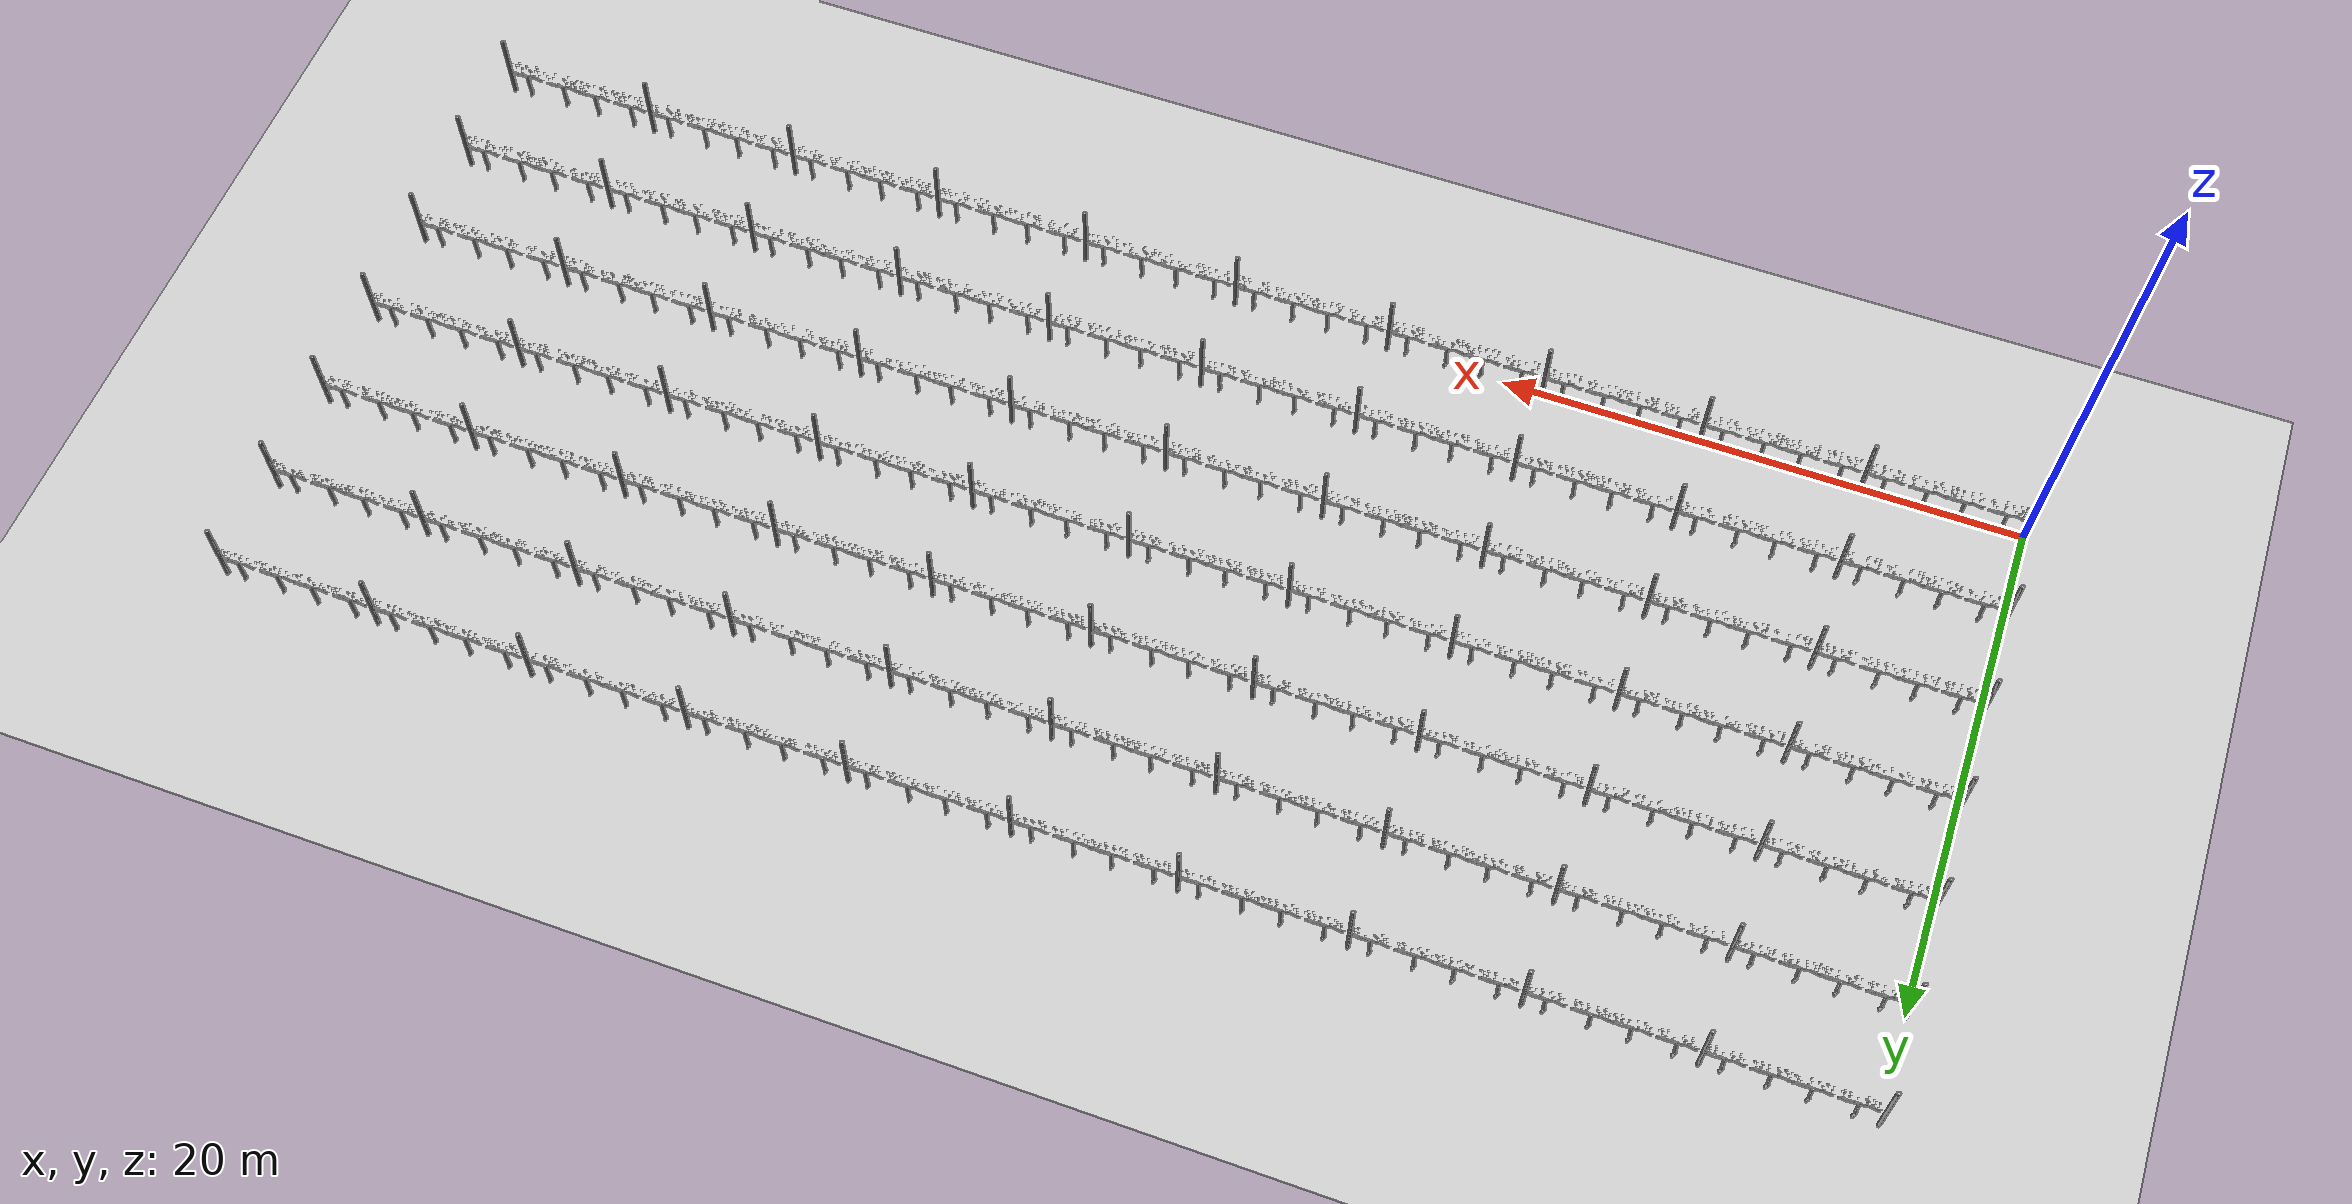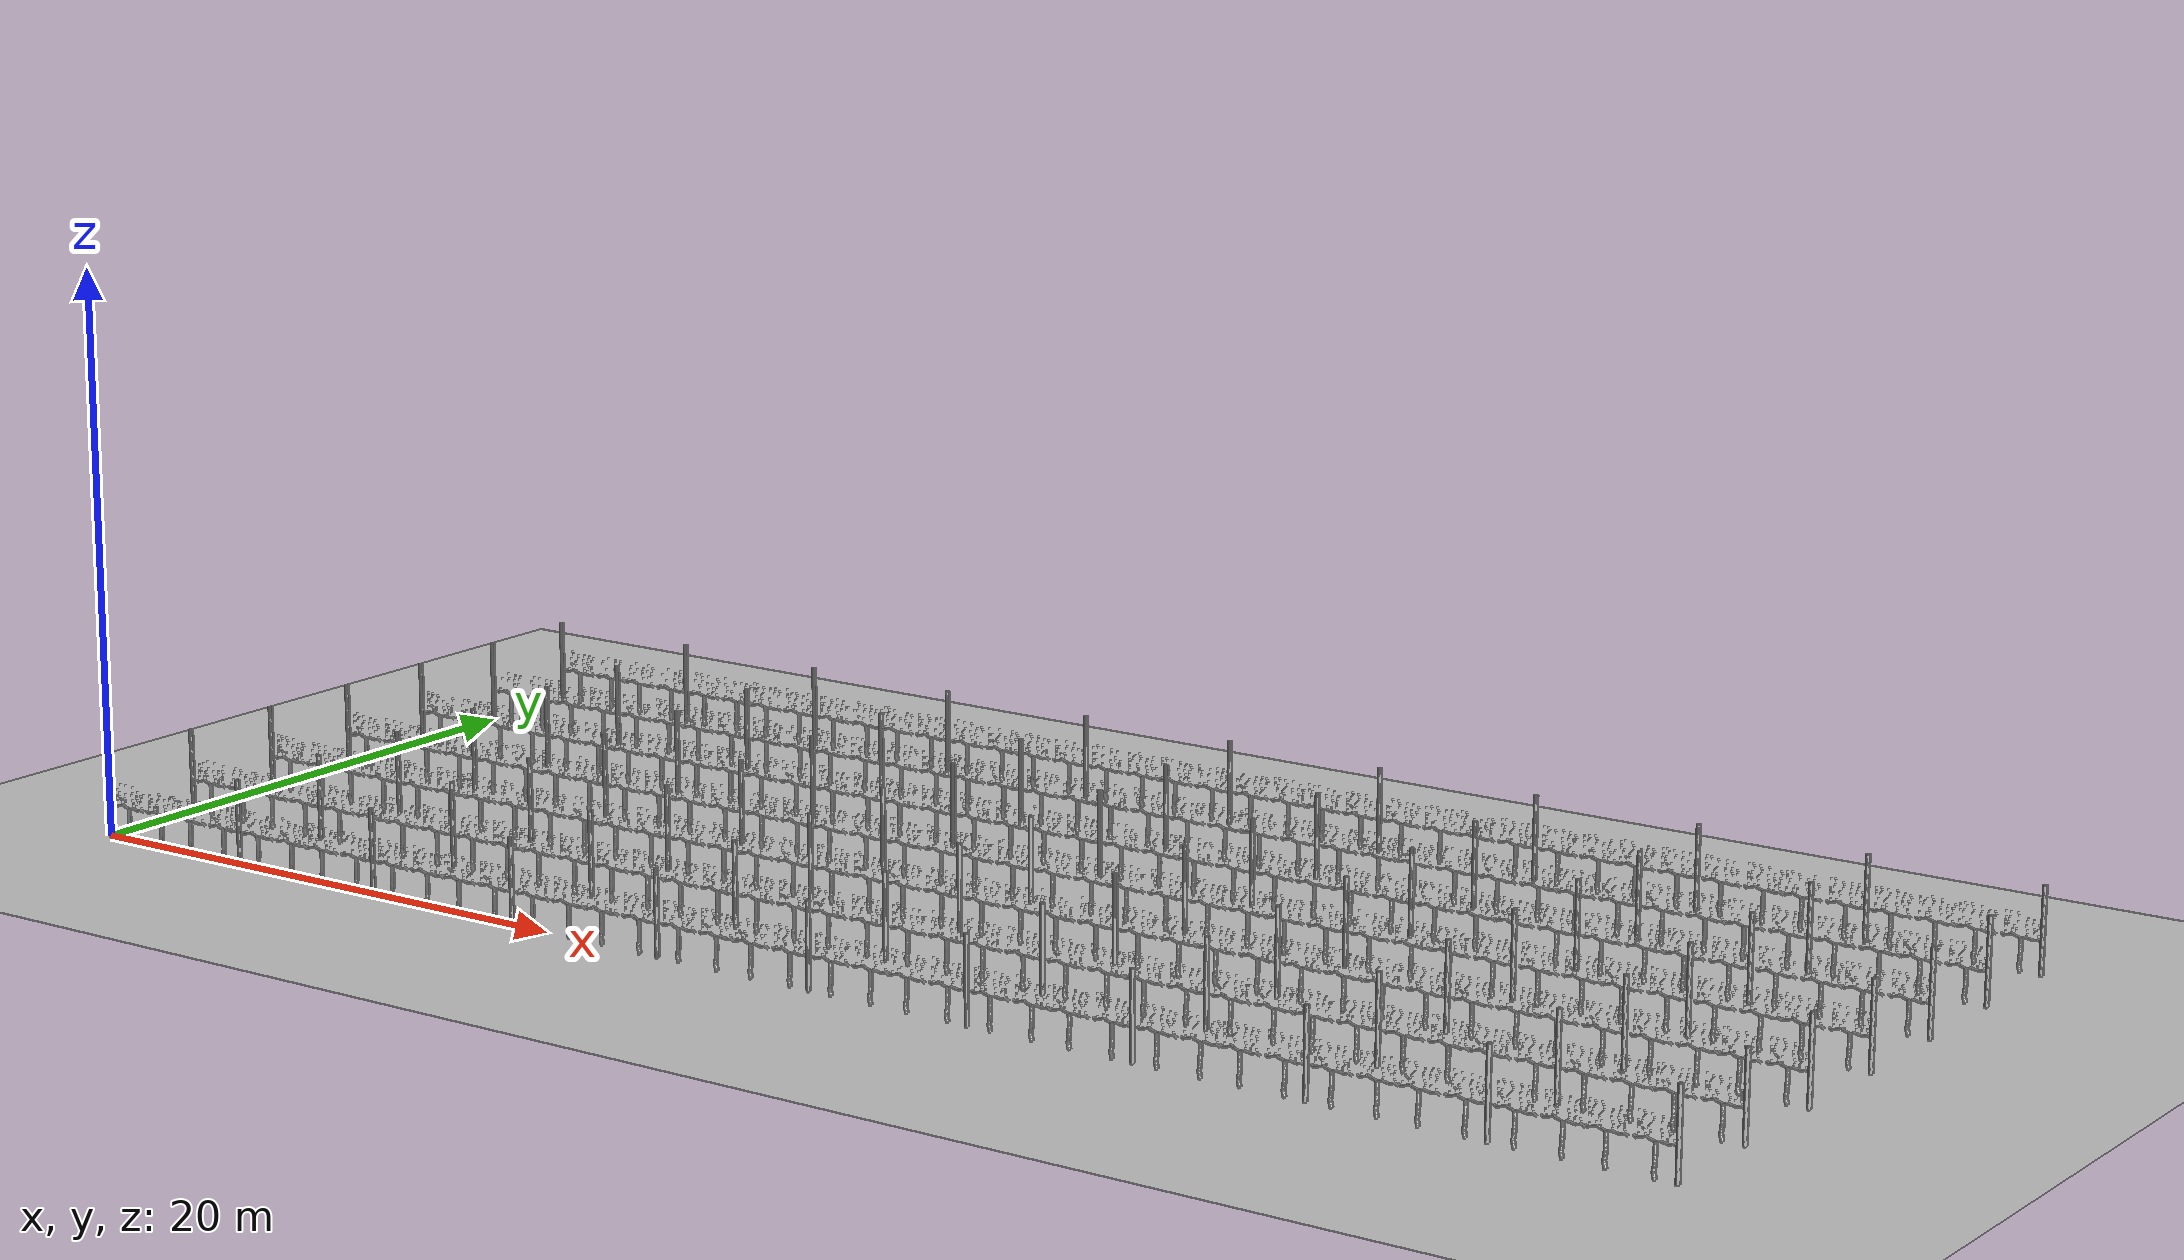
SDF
<?xml version="1.0" ?>
<sdf version='1.7'>
  <world name='default'>
    <light name='sun' type='directional'>
      <cast_shadows>1</cast_shadows>
      <pose>0 0 10 0 -0 0</pose>
      <diffuse>0.8 0.8 0.8 1</diffuse>
      <specular>0.2 0.03 0.2 1</specular>
      <attenuation>
        <range>1000</range>
        <constant>0.9</constant>
        <linear>0.01</linear>
        <quadratic>0.001</quadratic>
      </attenuation>
      <direction>-0.5 0.1 -0.9</direction>
    </light>

    <model name="ground_plane">
      <static>true</static>
      <link name="link">
        <collision name="collision">
          <geometry>
            <plane>
              <normal>0 0 1</normal>
              <size>100 100</size>
            </plane>
          </geometry>
        </collision>
        <visual name="visual">
          <geometry>
            <plane>
              <normal>0 0 1</normal>
              <size>100 100</size>
            </plane>
          </geometry>
        </visual>
      </link>
    </model>

    <model name='unit_cylinder_fila_1_palo_1'>
      <static>true</static>
      <pose>0 0.0 1.5 0 0 0</pose>
      <link name='link'>
        <collision name='collision'>
          <geometry>
            <cylinder>
              <radius>0.075</radius>
              <length>3</length>
            </cylinder>
          </geometry>
        </collision>
        <visual name='visual'>
          <geometry>
            <cylinder>
              <radius>0.075</radius>
              <length>3</length>
            </cylinder>
          </geometry>
        </visual>
      </link>
    </model>

    <model name='vinya_1_palo_1_fila_1'>
      <static>true</static>
      <pose>0.9 0.0 0 0 0 0</pose>
      <link name='link'>
        <collision name='collision'>
          <geometry>
            <mesh>
              <uri>file://models/vinya/meshes/vinya.dae</uri>
            </mesh>
          </geometry>
        </collision>
        <visual name='visual'>
          <geometry>
            <mesh>
              <uri>file://models/vinya/meshes/vinya.dae</uri>
            </mesh>
          </geometry>
        </visual>
      </link>
    </model>

    <model name='vinya_2_palo_1_fila_1'>
      <static>true</static>
      <pose>2.46 0.0 0 0 0 0</pose>
      <link name='link'>
        <collision name='collision'>
          <geometry>
            <mesh>
              <uri>file://models/vinya/meshes/vinya.dae</uri>
            </mesh>
          </geometry>
        </collision>
        <visual name='visual'>
          <geometry>
            <mesh>
              <uri>file://models/vinya/meshes/vinya.dae</uri>
            </mesh>
          </geometry>
        </visual>
      </link>
    </model>

    <model name='vinya_3_palo_1_fila_1'>
      <static>true</static>
      <pose>3.86 0.0 0 0 0 0</pose>
      <link name='link'>
        <collision name='collision'>
          <geometry>
            <mesh>
              <uri>file://models/vinya/meshes/vinya.dae</uri>
            </mesh>
          </geometry>
        </collision>
        <visual name='visual'>
          <geometry>
            <mesh>
              <uri>file://models/vinya/meshes/vinya.dae</uri>
            </mesh>
          </geometry>
        </visual>
      </link>
    </model>

    <model name='vinya_4_palo_1_fila_1'>
      <static>true</static>
      <pose>5.435 0.0 0 0 0 0</pose>
      <link name='link'>
        <collision name='collision'>
          <geometry>
            <mesh>
              <uri>file://models/vinya/meshes/vinya.dae</uri>
            </mesh>
          </geometry>
        </collision>
        <visual name='visual'>
          <geometry>
            <mesh>
              <uri>file://models/vinya/meshes/vinya.dae</uri>
            </mesh>
          </geometry>
        </visual>
      </link>
    </model>

    <model name='unit_cylinder_fila_1_palo_2'>
      <static>true</static>
      <pose>6.159999999999999 0.0 1.5 0 0 0</pose>
      <link name='link'>
        <collision name='collision'>
          <geometry>
            <cylinder>
              <radius>0.075</radius>
              <length>3</length>
            </cylinder>
          </geometry>
        </collision>
        <visual name='visual'>
          <geometry>
            <cylinder>
              <radius>0.075</radius>
              <length>3</length>
            </cylinder>
          </geometry>
        </visual>
      </link>
    </model>

    <model name='vinya_1_palo_2_fila_1'>
      <static>true</static>
      <pose>7.06 0.0 0 0 0 0</pose>
      <link name='link'>
        <collision name='collision'>
          <geometry>
            <mesh>
              <uri>file://models/vinya/meshes/vinya.dae</uri>
            </mesh>
          </geometry>
        </collision>
        <visual name='visual'>
          <geometry>
            <mesh>
              <uri>file://models/vinya/meshes/vinya.dae</uri>
            </mesh>
          </geometry>
        </visual>
      </link>
    </model>

    <model name='vinya_2_palo_2_fila_1'>
      <static>true</static>
      <pose>8.62 0.0 0 0 0 0</pose>
      <link name='link'>
        <collision name='collision'>
          <geometry>
            <mesh>
              <uri>file://models/vinya/meshes/vinya.dae</uri>
            </mesh>
          </geometry>
        </collision>
        <visual name='visual'>
          <geometry>
            <mesh>
              <uri>file://models/vinya/meshes/vinya.dae</uri>
            </mesh>
          </geometry>
        </visual>
      </link>
    </model>

    <model name='vinya_3_palo_2_fila_1'>
      <static>true</static>
      <pose>10.02 0.0 0 0 0 0</pose>
      <link name='link'>
        <collision name='collision'>
          <geometry>
            <mesh>
              <uri>file://models/vinya/meshes/vinya.dae</uri>
            </mesh>
          </geometry>
        </collision>
        <visual name='visual'>
          <geometry>
            <mesh>
              <uri>file://models/vinya/meshes/vinya.dae</uri>
            </mesh>
          </geometry>
        </visual>
      </link>
    </model>

    <model name='vinya_4_palo_2_fila_1'>
      <static>true</static>
      <pose>11.594999999999999 0.0 0 0 0 0</pose>
      <link name='link'>
        <collision name='collision'>
          <geometry>
            <mesh>
              <uri>file://models/vinya/meshes/vinya.dae</uri>
            </mesh>
          </geometry>
        </collision>
        <visual name='visual'>
          <geometry>
            <mesh>
              <uri>file://models/vinya/meshes/vinya.dae</uri>
            </mesh>
          </geometry>
        </visual>
      </link>
    </model>

    <model name='unit_cylinder_fila_1_palo_3'>
      <static>true</static>
      <pose>12.319999999999999 0.0 1.5 0 0 0</pose>
      <link name='link'>
        <collision name='collision'>
          <geometry>
            <cylinder>
              <radius>0.075</radius>
              <length>3</length>
            </cylinder>
          </geometry>
        </collision>
        <visual name='visual'>
          <geometry>
            <cylinder>
              <radius>0.075</radius>
              <length>3</length>
            </cylinder>
          </geometry>
        </visual>
      </link>
    </model>

    <model name='vinya_1_palo_3_fila_1'>
      <static>true</static>
      <pose>13.219999999999999 0.0 0 0 0 0</pose>
      <link name='link'>
        <collision name='collision'>
          <geometry>
            <mesh>
              <uri>file://models/vinya/meshes/vinya.dae</uri>
            </mesh>
          </geometry>
        </collision>
        <visual name='visual'>
          <geometry>
            <mesh>
              <uri>file://models/vinya/meshes/vinya.dae</uri>
            </mesh>
          </geometry>
        </visual>
      </link>
    </model>

    <model name='vinya_2_palo_3_fila_1'>
      <static>true</static>
      <pose>14.78 0.0 0 0 0 0</pose>
      <link name='link'>
        <collision name='collision'>
          <geometry>
            <mesh>
              <uri>file://models/vinya/meshes/vinya.dae</uri>
            </mesh>
          </geometry>
        </collision>
        <visual name='visual'>
          <geometry>
            <mesh>
              <uri>file://models/vinya/meshes/vinya.dae</uri>
            </mesh>
          </geometry>
        </visual>
      </link>
    </model>

    <model name='vinya_3_palo_3_fila_1'>
      <static>true</static>
      <pose>16.18 0.0 0 0 0 0</pose>
      <link name='link'>
        <collision name='collision'>
          <geometry>
            <mesh>
              <uri>file://models/vinya/meshes/vinya.dae</uri>
            </mesh>
          </geometry>
        </collision>
        <visual name='visual'>
          <geometry>
            <mesh>
              <uri>file://models/vinya/meshes/vinya.dae</uri>
            </mesh>
          </geometry>
        </visual>
      </link>
    </model>

    <model name='vinya_4_palo_3_fila_1'>
      <static>true</static>
      <pose>17.755 0.0 0 0 0 0</pose>
      <link name='link'>
        <collision name='collision'>
          <geometry>
            <mesh>
              <uri>file://models/vinya/meshes/vinya.dae</uri>
            </mesh>
          </geometry>
        </collision>
        <visual name='visual'>
          <geometry>
            <mesh>
              <uri>file://models/vinya/meshes/vinya.dae</uri>
            </mesh>
          </geometry>
        </visual>
      </link>
    </model>

    <model name='unit_cylinder_fila_1_palo_4'>
      <static>true</static>
      <pose>18.48 0.0 1.5 0 0 0</pose>
      <link name='link'>
        <collision name='collision'>
          <geometry>
            <cylinder>
              <radius>0.075</radius>
              <length>3</length>
            </cylinder>
          </geometry>
        </collision>
        <visual name='visual'>
          <geometry>
            <cylinder>
              <radius>0.075</radius>
              <length>3</length>
            </cylinder>
          </geometry>
        </visual>
      </link>
    </model>

    <model name='vinya_1_palo_4_fila_1'>
      <static>true</static>
      <pose>19.38 0.0 0 0 0 0</pose>
      <link name='link'>
        <collision name='collision'>
          <geometry>
            <mesh>
              <uri>file://models/vinya/meshes/vinya.dae</uri>
            </mesh>
          </geometry>
        </collision>
        <visual name='visual'>
          <geometry>
            <mesh>
              <uri>file://models/vinya/meshes/vinya.dae</uri>
            </mesh>
          </geometry>
        </visual>
      </link>
    </model>

    <model name='vinya_2_palo_4_fila_1'>
      <static>true</static>
      <pose>20.939999999999998 0.0 0 0 0 0</pose>
      <link name='link'>
        <collision name='collision'>
          <geometry>
            <mesh>
              <uri>file://models/vinya/meshes/vinya.dae</uri>
            </mesh>
          </geometry>
        </collision>
        <visual name='visual'>
          <geometry>
            <mesh>
              <uri>file://models/vinya/meshes/vinya.dae</uri>
            </mesh>
          </geometry>
        </visual>
      </link>
    </model>

    <model name='vinya_3_palo_4_fila_1'>
      <static>true</static>
      <pose>22.339999999999996 0.0 0 0 0 0</pose>
      <link name='link'>
        <collision name='collision'>
          <geometry>
            <mesh>
              <uri>file://models/vinya/meshes/vinya.dae</uri>
            </mesh>
          </geometry>
        </collision>
        <visual name='visual'>
          <geometry>
            <mesh>
              <uri>file://models/vinya/meshes/vinya.dae</uri>
            </mesh>
          </geometry>
        </visual>
      </link>
    </model>

    <model name='vinya_4_palo_4_fila_1'>
      <static>true</static>
      <pose>23.914999999999996 0.0 0 0 0 0</pose>
      <link name='link'>
        <collision name='collision'>
          <geometry>
            <mesh>
              <uri>file://models/vinya/meshes/vinya.dae</uri>
            </mesh>
          </geometry>
        </collision>
        <visual name='visual'>
          <geometry>
            <mesh>
              <uri>file://models/vinya/meshes/vinya.dae</uri>
            </mesh>
          </geometry>
        </visual>
      </link>
    </model>

    <model name='unit_cylinder_fila_1_palo_5'>
      <static>true</static>
      <pose>24.639999999999997 0.0 1.5 0 0 0</pose>
      <link name='link'>
        <collision name='collision'>
          <geometry>
            <cylinder>
              <radius>0.075</radius>
              <length>3</length>
            </cylinder>
          </geometry>
        </collision>
        <visual name='visual'>
          <geometry>
            <cylinder>
              <radius>0.075</radius>
              <length>3</length>
            </cylinder>
          </geometry>
        </visual>
      </link>
    </model>

    <model name='vinya_1_palo_5_fila_1'>
      <static>true</static>
      <pose>25.539999999999996 0.0 0 0 0 0</pose>
      <link name='link'>
        <collision name='collision'>
          <geometry>
            <mesh>
              <uri>file://models/vinya/meshes/vinya.dae</uri>
            </mesh>
          </geometry>
        </collision>
        <visual name='visual'>
          <geometry>
            <mesh>
              <uri>file://models/vinya/meshes/vinya.dae</uri>
            </mesh>
          </geometry>
        </visual>
      </link>
    </model>

    <model name='vinya_2_palo_5_fila_1'>
      <static>true</static>
      <pose>27.099999999999994 0.0 0 0 0 0</pose>
      <link name='link'>
        <collision name='collision'>
          <geometry>
            <mesh>
              <uri>file://models/vinya/meshes/vinya.dae</uri>
            </mesh>
          </geometry>
        </collision>
        <visual name='visual'>
          <geometry>
            <mesh>
              <uri>file://models/vinya/meshes/vinya.dae</uri>
            </mesh>
          </geometry>
        </visual>
      </link>
    </model>

    <model name='vinya_3_palo_5_fila_1'>
      <static>true</static>
      <pose>28.499999999999993 0.0 0 0 0 0</pose>
      <link name='link'>
        <collision name='collision'>
          <geometry>
            <mesh>
              <uri>file://models/vinya/meshes/vinya.dae</uri>
            </mesh>
          </geometry>
        </collision>
        <visual name='visual'>
          <geometry>
            <mesh>
              <uri>file://models/vinya/meshes/vinya.dae</uri>
            </mesh>
          </geometry>
        </visual>
      </link>
    </model>

    <model name='vinya_4_palo_5_fila_1'>
      <static>true</static>
      <pose>30.074999999999992 0.0 0 0 0 0</pose>
      <link name='link'>
        <collision name='collision'>
          <geometry>
            <mesh>
              <uri>file://models/vinya/meshes/vinya.dae</uri>
            </mesh>
          </geometry>
        </collision>
        <visual name='visual'>
          <geometry>
            <mesh>
              <uri>file://models/vinya/meshes/vinya.dae</uri>
            </mesh>
          </geometry>
        </visual>
      </link>
    </model>

    <model name='unit_cylinder_fila_1_palo_6'>
      <static>true</static>
      <pose>30.799999999999994 0.0 1.5 0 0 0</pose>
      <link name='link'>
        <collision name='collision'>
          <geometry>
            <cylinder>
              <radius>0.075</radius>
              <length>3</length>
            </cylinder>
          </geometry>
        </collision>
        <visual name='visual'>
          <geometry>
            <cylinder>
              <radius>0.075</radius>
              <length>3</length>
            </cylinder>
          </geometry>
        </visual>
      </link>
    </model>

    <model name='vinya_1_palo_6_fila_1'>
      <static>true</static>
      <pose>31.699999999999992 0.0 0 0 0 0</pose>
      <link name='link'>
        <collision name='collision'>
          <geometry>
            <mesh>
              <uri>file://models/vinya/meshes/vinya.dae</uri>
            </mesh>
          </geometry>
        </collision>
        <visual name='visual'>
          <geometry>
            <mesh>
              <uri>file://models/vinya/meshes/vinya.dae</uri>
            </mesh>
          </geometry>
        </visual>
      </link>
    </model>

    <model name='vinya_2_palo_6_fila_1'>
      <static>true</static>
      <pose>33.25999999999999 0.0 0 0 0 0</pose>
      <link name='link'>
        <collision name='collision'>
          <geometry>
            <mesh>
              <uri>file://models/vinya/meshes/vinya.dae</uri>
            </mesh>
          </geometry>
        </collision>
        <visual name='visual'>
          <geometry>
            <mesh>
              <uri>file://models/vinya/meshes/vinya.dae</uri>
            </mesh>
          </geometry>
        </visual>
      </link>
    </model>

    <model name='vinya_3_palo_6_fila_1'>
      <static>true</static>
      <pose>34.65999999999999 0.0 0 0 0 0</pose>
      <link name='link'>
        <collision name='collision'>
          <geometry>
            <mesh>
              <uri>file://models/vinya/meshes/vinya.dae</uri>
            </mesh>
          </geometry>
        </collision>
        <visual name='visual'>
          <geometry>
            <mesh>
              <uri>file://models/vinya/meshes/vinya.dae</uri>
            </mesh>
          </geometry>
        </visual>
      </link>
    </model>

    <model name='vinya_4_palo_6_fila_1'>
      <static>true</static>
      <pose>36.23499999999999 0.0 0 0 0 0</pose>
      <link name='link'>
        <collision name='collision'>
          <geometry>
            <mesh>
              <uri>file://models/vinya/meshes/vinya.dae</uri>
            </mesh>
          </geometry>
        </collision>
        <visual name='visual'>
          <geometry>
            <mesh>
              <uri>file://models/vinya/meshes/vinya.dae</uri>
            </mesh>
          </geometry>
        </visual>
      </link>
    </model>

    <model name='unit_cylinder_fila_1_palo_7'>
      <static>true</static>
      <pose>36.959999999999994 0.0 1.5 0 0 0</pose>
      <link name='link'>
        <collision name='collision'>
          <geometry>
            <cylinder>
              <radius>0.075</radius>
              <length>3</length>
            </cylinder>
          </geometry>
        </collision>
        <visual name='visual'>
          <geometry>
            <cylinder>
              <radius>0.075</radius>
              <length>3</length>
            </cylinder>
          </geometry>
        </visual>
      </link>
    </model>

    <model name='vinya_1_palo_7_fila_1'>
      <static>true</static>
      <pose>37.85999999999999 0.0 0 0 0 0</pose>
      <link name='link'>
        <collision name='collision'>
          <geometry>
            <mesh>
              <uri>file://models/vinya/meshes/vinya.dae</uri>
            </mesh>
          </geometry>
        </collision>
        <visual name='visual'>
          <geometry>
            <mesh>
              <uri>file://models/vinya/meshes/vinya.dae</uri>
            </mesh>
          </geometry>
        </visual>
      </link>
    </model>

    <model name='vinya_2_palo_7_fila_1'>
      <static>true</static>
      <pose>39.419999999999995 0.0 0 0 0 0</pose>
      <link name='link'>
        <collision name='collision'>
          <geometry>
            <mesh>
              <uri>file://models/vinya/meshes/vinya.dae</uri>
            </mesh>
          </geometry>
        </collision>
        <visual name='visual'>
          <geometry>
            <mesh>
              <uri>file://models/vinya/meshes/vinya.dae</uri>
            </mesh>
          </geometry>
        </visual>
      </link>
    </model>

    <model name='vinya_3_palo_7_fila_1'>
      <static>true</static>
      <pose>40.81999999999999 0.0 0 0 0 0</pose>
      <link name='link'>
        <collision name='collision'>
          <geometry>
            <mesh>
              <uri>file://models/vinya/meshes/vinya.dae</uri>
            </mesh>
          </geometry>
        </collision>
        <visual name='visual'>
          <geometry>
            <mesh>
              <uri>file://models/vinya/meshes/vinya.dae</uri>
            </mesh>
          </geometry>
        </visual>
      </link>
    </model>

    <model name='vinya_4_palo_7_fila_1'>
      <static>true</static>
      <pose>42.394999999999996 0.0 0 0 0 0</pose>
      <link name='link'>
        <collision name='collision'>
          <geometry>
            <mesh>
              <uri>file://models/vinya/meshes/vinya.dae</uri>
            </mesh>
          </geometry>
        </collision>
        <visual name='visual'>
          <geometry>
            <mesh>
              <uri>file://models/vinya/meshes/vinya.dae</uri>
            </mesh>
          </geometry>
        </visual>
      </link>
    </model>

    <model name='unit_cylinder_fila_1_palo_8'>
      <static>true</static>
      <pose>43.12 0.0 1.5 0 0 0</pose>
      <link name='link'>
        <collision name='collision'>
          <geometry>
            <cylinder>
              <radius>0.075</radius>
              <length>3</length>
            </cylinder>
          </geometry>
        </collision>
        <visual name='visual'>
          <geometry>
            <cylinder>
              <radius>0.075</radius>
              <length>3</length>
            </cylinder>
          </geometry>
        </visual>
      </link>
    </model>

    <model name='vinya_1_palo_8_fila_1'>
      <static>true</static>
      <pose>44.019999999999996 0.0 0 0 0 0</pose>
      <link name='link'>
        <collision name='collision'>
          <geometry>
            <mesh>
              <uri>file://models/vinya/meshes/vinya.dae</uri>
            </mesh>
          </geometry>
        </collision>
        <visual name='visual'>
          <geometry>
            <mesh>
              <uri>file://models/vinya/meshes/vinya.dae</uri>
            </mesh>
          </geometry>
        </visual>
      </link>
    </model>

    <model name='vinya_2_palo_8_fila_1'>
      <static>true</static>
      <pose>45.58 0.0 0 0 0 0</pose>
      <link name='link'>
        <collision name='collision'>
          <geometry>
            <mesh>
              <uri>file://models/vinya/meshes/vinya.dae</uri>
            </mesh>
          </geometry>
        </collision>
        <visual name='visual'>
          <geometry>
            <mesh>
              <uri>file://models/vinya/meshes/vinya.dae</uri>
            </mesh>
          </geometry>
        </visual>
      </link>
    </model>

    <model name='vinya_3_palo_8_fila_1'>
      <static>true</static>
      <pose>46.98 0.0 0 0 0 0</pose>
      <link name='link'>
        <collision name='collision'>
          <geometry>
            <mesh>
              <uri>file://models/vinya/meshes/vinya.dae</uri>
            </mesh>
          </geometry>
        </collision>
        <visual name='visual'>
          <geometry>
            <mesh>
              <uri>file://models/vinya/meshes/vinya.dae</uri>
            </mesh>
          </geometry>
        </visual>
      </link>
    </model>

    <model name='vinya_4_palo_8_fila_1'>
      <static>true</static>
      <pose>48.555 0.0 0 0 0 0</pose>
      <link name='link'>
        <collision name='collision'>
          <geometry>
            <mesh>
              <uri>file://models/vinya/meshes/vinya.dae</uri>
            </mesh>
          </geometry>
        </collision>
        <visual name='visual'>
          <geometry>
            <mesh>
              <uri>file://models/vinya/meshes/vinya.dae</uri>
            </mesh>
          </geometry>
        </visual>
      </link>
    </model>

    <model name='unit_cylinder_fila_1_palo_9'>
      <static>true</static>
      <pose>49.28 0.0 1.5 0 0 0</pose>
      <link name='link'>
        <collision name='collision'>
          <geometry>
            <cylinder>
              <radius>0.075</radius>
              <length>3</length>
            </cylinder>
          </geometry>
        </collision>
        <visual name='visual'>
          <geometry>
            <cylinder>
              <radius>0.075</radius>
              <length>3</length>
            </cylinder>
          </geometry>
        </visual>
      </link>
    </model>

    <model name='vinya_1_palo_9_fila_1'>
      <static>true</static>
      <pose>50.18 0.0 0 0 0 0</pose>
      <link name='link'>
        <collision name='collision'>
          <geometry>
            <mesh>
              <uri>file://models/vinya/meshes/vinya.dae</uri>
            </mesh>
          </geometry>
        </collision>
        <visual name='visual'>
          <geometry>
            <mesh>
              <uri>file://models/vinya/meshes/vinya.dae</uri>
            </mesh>
          </geometry>
        </visual>
      </link>
    </model>

    <model name='vinya_2_palo_9_fila_1'>
      <static>true</static>
      <pose>51.74 0.0 0 0 0 0</pose>
      <link name='link'>
        <collision name='collision'>
          <geometry>
            <mesh>
              <uri>file://models/vinya/meshes/vinya.dae</uri>
            </mesh>
          </geometry>
        </collision>
        <visual name='visual'>
          <geometry>
            <mesh>
              <uri>file://models/vinya/meshes/vinya.dae</uri>
            </mesh>
          </geometry>
        </visual>
      </link>
    </model>

    <model name='vinya_3_palo_9_fila_1'>
      <static>true</static>
      <pose>53.14 0.0 0 0 0 0</pose>
      <link name='link'>
        <collision name='collision'>
          <geometry>
            <mesh>
              <uri>file://models/vinya/meshes/vinya.dae</uri>
            </mesh>
          </geometry>
        </collision>
        <visual name='visual'>
          <geometry>
            <mesh>
              <uri>file://models/vinya/meshes/vinya.dae</uri>
            </mesh>
          </geometry>
        </visual>
      </link>
    </model>

    <model name='vinya_4_palo_9_fila_1'>
      <static>true</static>
      <pose>54.715 0.0 0 0 0 0</pose>
      <link name='link'>
        <collision name='collision'>
          <geometry>
            <mesh>
              <uri>file://models/vinya/meshes/vinya.dae</uri>
            </mesh>
          </geometry>
        </collision>
        <visual name='visual'>
          <geometry>
            <mesh>
              <uri>file://models/vinya/meshes/vinya.dae</uri>
            </mesh>
          </geometry>
        </visual>
      </link>
    </model>

    <model name='unit_cylinder_fila_1_palo_10'>
      <static>true</static>
      <pose>55.440000000000005 0.0 1.5 0 0 0</pose>
      <link name='link'>
        <collision name='collision'>
          <geometry>
            <cylinder>
              <radius>0.075</radius>
              <length>3</length>
            </cylinder>
          </geometry>
        </collision>
        <visual name='visual'>
          <geometry>
            <cylinder>
              <radius>0.075</radius>
              <length>3</length>
            </cylinder>
          </geometry>
        </visual>
      </link>
    </model>

    <model name='vinya_1_palo_10_fila_1'>
      <static>true</static>
      <pose>56.34 0.0 0 0 0 0</pose>
      <link name='link'>
        <collision name='collision'>
          <geometry>
            <mesh>
              <uri>file://models/vinya/meshes/vinya.dae</uri>
            </mesh>
          </geometry>
        </collision>
        <visual name='visual'>
          <geometry>
            <mesh>
              <uri>file://models/vinya/meshes/vinya.dae</uri>
            </mesh>
          </geometry>
        </visual>
      </link>
    </model>

    <model name='vinya_2_palo_10_fila_1'>
      <static>true</static>
      <pose>57.900000000000006 0.0 0 0 0 0</pose>
      <link name='link'>
        <collision name='collision'>
          <geometry>
            <mesh>
              <uri>file://models/vinya/meshes/vinya.dae</uri>
            </mesh>
          </geometry>
        </collision>
        <visual name='visual'>
          <geometry>
            <mesh>
              <uri>file://models/vinya/meshes/vinya.dae</uri>
            </mesh>
          </geometry>
        </visual>
      </link>
    </model>

    <model name='vinya_3_palo_10_fila_1'>
      <static>true</static>
      <pose>59.300000000000004 0.0 0 0 0 0</pose>
      <link name='link'>
        <collision name='collision'>
          <geometry>
            <mesh>
              <uri>file://models/vinya/meshes/vinya.dae</uri>
            </mesh>
          </geometry>
        </collision>
        <visual name='visual'>
          <geometry>
            <mesh>
              <uri>file://models/vinya/meshes/vinya.dae</uri>
            </mesh>
          </geometry>
        </visual>
      </link>
    </model>

    <model name='vinya_4_palo_10_fila_1'>
      <static>true</static>
      <pose>60.87500000000001 0.0 0 0 0 0</pose>
      <link name='link'>
        <collision name='collision'>
          <geometry>
            <mesh>
              <uri>file://models/vinya/meshes/vinya.dae</uri>
            </mesh>
          </geometry>
        </collision>
        <visual name='visual'>
          <geometry>
            <mesh>
              <uri>file://models/vinya/meshes/vinya.dae</uri>
            </mesh>
          </geometry>
        </visual>
      </link>
    </model>

    <model name='unit_cylinder_fila_1_palo_11'>
      <static>true</static>
      <pose>61.60000000000001 0.0 1.5 0 0 0</pose>
      <link name='link'>
        <collision name='collision'>
          <geometry>
            <cylinder>
              <radius>0.075</radius>
              <length>3</length>
            </cylinder>
          </geometry>
        </collision>
        <visual name='visual'>
          <geometry>
            <cylinder>
              <radius>0.075</radius>
              <length>3</length>
            </cylinder>
          </geometry>
        </visual>
      </link>
    </model>

    <model name='unit_cylinder_fila_2_palo_1'>
      <static>true</static>
      <pose>0 4.0 1.5 0 0 0</pose>
      <link name='link'>
        <collision name='collision'>
          <geometry>
            <cylinder>
              <radius>0.075</radius>
              <length>3</length>
            </cylinder>
          </geometry>
        </collision>
        <visual name='visual'>
          <geometry>
            <cylinder>
              <radius>0.075</radius>
              <length>3</length>
            </cylinder>
          </geometry>
        </visual>
      </link>
    </model>

    <model name='vinya_1_palo_1_fila_2'>
      <static>true</static>
      <pose>0.9 4.0 0 0 0 0</pose>
      <link name='link'>
        <collision name='collision'>
          <geometry>
            <mesh>
              <uri>file://models/vinya/meshes/vinya.dae</uri>
            </mesh>
          </geometry>
        </collision>
        <visual name='visual'>
          <geometry>
            <mesh>
              <uri>file://models/vinya/meshes/vinya.dae</uri>
            </mesh>
          </geometry>
        </visual>
      </link>
    </model>

    <model name='vinya_2_palo_1_fila_2'>
      <static>true</static>
      <pose>2.46 4.0 0 0 0 0</pose>
      <link name='link'>
        <collision name='collision'>
          <geometry>
            <mesh>
              <uri>file://models/vinya/meshes/vinya.dae</uri>
            </mesh>
          </geometry>
        </collision>
        <visual name='visual'>
          <geometry>
            <mesh>
              <uri>file://models/vinya/meshes/vinya.dae</uri>
            </mesh>
          </geometry>
        </visual>
      </link>
    </model>

    <model name='vinya_3_palo_1_fila_2'>
      <static>true</static>
      <pose>3.86 4.0 0 0 0 0</pose>
      <link name='link'>
        <collision name='collision'>
          <geometry>
            <mesh>
              <uri>file://models/vinya/meshes/vinya.dae</uri>
            </mesh>
          </geometry>
        </collision>
        <visual name='visual'>
          <geometry>
            <mesh>
              <uri>file://models/vinya/meshes/vinya.dae</uri>
            </mesh>
          </geometry>
        </visual>
      </link>
    </model>

    <model name='vinya_4_palo_1_fila_2'>
      <static>true</static>
      <pose>5.435 4.0 0 0 0 0</pose>
      <link name='link'>
        <collision name='collision'>
          <geometry>
            <mesh>
              <uri>file://models/vinya/meshes/vinya.dae</uri>
            </mesh>
          </geometry>
        </collision>
        <visual name='visual'>
          <geometry>
            <mesh>
              <uri>file://models/vinya/meshes/vinya.dae</uri>
            </mesh>
          </geometry>
        </visual>
      </link>
    </model>

    <model name='unit_cylinder_fila_2_palo_2'>
      <static>true</static>
      <pose>6.159999999999999 4.0 1.5 0 0 0</pose>
      <link name='link'>
        <collision name='collision'>
          <geometry>
            <cylinder>
              <radius>0.075</radius>
              <length>3</length>
            </cylinder>
          </geometry>
        </collision>
        <visual name='visual'>
          <geometry>
            <cylinder>
              <radius>0.075</radius>
              <length>3</length>
            </cylinder>
          </geometry>
        </visual>
      </link>
    </model>

    <model name='vinya_1_palo_2_fila_2'>
      <static>true</static>
      <pose>7.06 4.0 0 0 0 0</pose>
      <link name='link'>
        <collision name='collision'>
          <geometry>
            <mesh>
              <uri>file://models/vinya/meshes/vinya.dae</uri>
            </mesh>
          </geometry>
        </collision>
        <visual name='visual'>
          <geometry>
            <mesh>
              <uri>file://models/vinya/meshes/vinya.dae</uri>
            </mesh>
          </geometry>
        </visual>
      </link>
    </model>

    <model name='vinya_2_palo_2_fila_2'>
      <static>true</static>
      <pose>8.62 4.0 0 0 0 0</pose>
      <link name='link'>
        <collision name='collision'>
          <geometry>
            <mesh>
              <uri>file://models/vinya/meshes/vinya.dae</uri>
            </mesh>
          </geometry>
        </collision>
        <visual name='visual'>
          <geometry>
            <mesh>
              <uri>file://models/vinya/meshes/vinya.dae</uri>
            </mesh>
          </geometry>
        </visual>
      </link>
    </model>

    <model name='vinya_3_palo_2_fila_2'>
      <static>true</static>
      <pose>10.02 4.0 0 0 0 0</pose>
      <link name='link'>
        <collision name='collision'>
          <geometry>
            <mesh>
              <uri>file://models/vinya/meshes/vinya.dae</uri>
            </mesh>
          </geometry>
        </collision>
        <visual name='visual'>
          <geometry>
            <mesh>
              <uri>file://models/vinya/meshes/vinya.dae</uri>
            </mesh>
          </geometry>
        </visual>
      </link>
    </model>

    <model name='vinya_4_palo_2_fila_2'>
      <static>true</static>
      <pose>11.594999999999999 4.0 0 0 0 0</pose>
      <link name='link'>
        <collision name='collision'>
          <geometry>
            <mesh>
              <uri>file://models/vinya/meshes/vinya.dae</uri>
            </mesh>
          </geometry>
        </collision>
        <visual name='visual'>
          <geometry>
            <mesh>
              <uri>file://models/vinya/meshes/vinya.dae</uri>
            </mesh>
          </geometry>
        </visual>
      </link>
    </model>

    <model name='unit_cylinder_fila_2_palo_3'>
      <static>true</static>
      <pose>12.319999999999999 4.0 1.5 0 0 0</pose>
      <link name='link'>
        <collision name='collision'>
          <geometry>
            <cylinder>
              <radius>0.075</radius>
              <length>3</length>
            </cylinder>
          </geometry>
        </collision>
        <visual name='visual'>
          <geometry>
            <cylinder>
              <radius>0.075</radius>
              <length>3</length>
            </cylinder>
          </geometry>
        </visual>
      </link>
    </model>

    <model name='vinya_1_palo_3_fila_2'>
      <static>true</static>
      <pose>13.219999999999999 4.0 0 0 0 0</pose>
      <link name='link'>
        <collision name='collision'>
          <geometry>
            <mesh>
              <uri>file://models/vinya/meshes/vinya.dae</uri>
            </mesh>
          </geometry>
        </collision>
        <visual name='visual'>
          <geometry>
            <mesh>
              <uri>file://models/vinya/meshes/vinya.dae</uri>
            </mesh>
          </geometry>
        </visual>
      </link>
    </model>

    <model name='vinya_2_palo_3_fila_2'>
      <static>true</static>
      <pose>14.78 4.0 0 0 0 0</pose>
      <link name='link'>
        <collision name='collision'>
          <geometry>
            <mesh>
              <uri>file://models/vinya/meshes/vinya.dae</uri>
            </mesh>
          </geometry>
        </collision>
        <visual name='visual'>
          <geometry>
            <mesh>
              <uri>file://models/vinya/meshes/vinya.dae</uri>
            </mesh>
          </geometry>
        </visual>
      </link>
    </model>

    <model name='vinya_3_palo_3_fila_2'>
      <static>true</static>
      <pose>16.18 4.0 0 0 0 0</pose>
      <link name='link'>
        <collision name='collision'>
          <geometry>
            <mesh>
              <uri>file://models/vinya/meshes/vinya.dae</uri>
            </mesh>
          </geometry>
        </collision>
        <visual name='visual'>
          <geometry>
            <mesh>
              <uri>file://models/vinya/meshes/vinya.dae</uri>
            </mesh>
          </geometry>
        </visual>
      </link>
    </model>

    <model name='vinya_4_palo_3_fila_2'>
      <static>true</static>
      <pose>17.755 4.0 0 0 0 0</pose>
      <link name='link'>
        <collision name='collision'>
          <geometry>
            <mesh>
              <uri>file://models/vinya/meshes/vinya.dae</uri>
            </mesh>
          </geometry>
        </collision>
        <visual name='visual'>
          <geometry>
            <mesh>
              <uri>file://models/vinya/meshes/vinya.dae</uri>
            </mesh>
          </geometry>
        </visual>
      </link>
    </model>

    <model name='unit_cylinder_fila_2_palo_4'>
      <static>true</static>
      <pose>18.48 4.0 1.5 0 0 0</pose>
      <link name='link'>
        <collision name='collision'>
          <geometry>
            <cylinder>
              <radius>0.075</radius>
              <length>3</length>
            </cylinder>
          </geometry>
        </collision>
        <visual name='visual'>
          <geometry>
            <cylinder>
              <radius>0.075</radius>
              <length>3</length>
            </cylinder>
          </geometry>
        </visual>
      </link>
    </model>

    <model name='vinya_1_palo_4_fila_2'>
      <static>true</static>
      <pose>19.38 4.0 0 0 0 0</pose>
      <link name='link'>
        <collision name='collision'>
          <geometry>
            <mesh>
              <uri>file://models/vinya/meshes/vinya.dae</uri>
            </mesh>
          </geometry>
        </collision>
        <visual name='visual'>
          <geometry>
            <mesh>
              <uri>file://models/vinya/meshes/vinya.dae</uri>
            </mesh>
          </geometry>
        </visual>
      </link>
    </model>

    <model name='vinya_2_palo_4_fila_2'>
      <static>true</static>
      <pose>20.939999999999998 4.0 0 0 0 0</pose>
      <link name='link'>
        <collision name='collision'>
          <geometry>
            <mesh>
              <uri>file://models/vinya/meshes/vinya.dae</uri>
            </mesh>
          </geometry>
        </collision>
        <visual name='visual'>
          <geometry>
            <mesh>
              <uri>file://models/vinya/meshes/vinya.dae</uri>
            </mesh>
          </geometry>
        </visual>
      </link>
    </model>

    <model name='vinya_3_palo_4_fila_2'>
      <static>true</static>
      <pose>22.339999999999996 4.0 0 0 0 0</pose>
      <link name='link'>
        <collision name='collision'>
          <geometry>
            <mesh>
              <uri>file://models/vinya/meshes/vinya.dae</uri>
            </mesh>
          </geometry>
        </collision>
        <visual name='visual'>
          <geometry>
            <mesh>
              <uri>file://models/vinya/meshes/vinya.dae</uri>
            </mesh>
          </geometry>
        </visual>
      </link>
    </model>

    <model name='vinya_4_palo_4_fila_2'>
      <static>true</static>
      <pose>23.914999999999996 4.0 0 0 0 0</pose>
      <link name='link'>
        <collision name='collision'>
          <geometry>
            <mesh>
              <uri>file://models/vinya/meshes/vinya.dae</uri>
            </mesh>
          </geometry>
        </collision>
        <visual name='visual'>
          <geometry>
            <mesh>
              <uri>file://models/vinya/meshes/vinya.dae</uri>
            </mesh>
          </geometry>
        </visual>
      </link>
    </model>

    <model name='unit_cylinder_fila_2_palo_5'>
      <static>true</static>
      <pose>24.639999999999997 4.0 1.5 0 0 0</pose>
      <link name='link'>
        <collision name='collision'>
          <geometry>
            <cylinder>
              <radius>0.075</radius>
              <length>3</length>
            </cylinder>
          </geometry>
        </collision>
        <visual name='visual'>
          <geometry>
            <cylinder>
              <radius>0.075</radius>
              <length>3</length>
            </cylinder>
          </geometry>
        </visual>
      </link>
    </model>

    <model name='vinya_1_palo_5_fila_2'>
      <static>true</static>
      <pose>25.539999999999996 4.0 0 0 0 0</pose>
      <link name='link'>
        <collision name='collision'>
          <geometry>
            <mesh>
              <uri>file://models/vinya/meshes/vinya.dae</uri>
            </mesh>
          </geometry>
        </collision>
        <visual name='visual'>
          <geometry>
            <mesh>
              <uri>file://models/vinya/meshes/vinya.dae</uri>
            </mesh>
          </geometry>
        </visual>
      </link>
    </model>

    <model name='vinya_2_palo_5_fila_2'>
      <static>true</static>
      <pose>27.099999999999994 4.0 0 0 0 0</pose>
      <link name='link'>
        <collision name='collision'>
          <geometry>
            <mesh>
              <uri>file://models/vinya/meshes/vinya.dae</uri>
            </mesh>
          </geometry>
        </collision>
        <visual name='visual'>
          <geometry>
            <mesh>
              <uri>file://models/vinya/meshes/vinya.dae</uri>
            </mesh>
          </geometry>
        </visual>
      </link>
    </model>

    <model name='vinya_3_palo_5_fila_2'>
      <static>true</static>
      <pose>28.499999999999993 4.0 0 0 0 0</pose>
      <link name='link'>
        <collision name='collision'>
          <geometry>
            <mesh>
              <uri>file://models/vinya/meshes/vinya.dae</uri>
            </mesh>
          </geometry>
        </collision>
        <visual name='visual'>
          <geometry>
            <mesh>
              <uri>file://models/vinya/meshes/vinya.dae</uri>
            </mesh>
          </geometry>
        </visual>
      </link>
    </model>

    <model name='vinya_4_palo_5_fila_2'>
      <static>true</static>
      <pose>30.074999999999992 4.0 0 0 0 0</pose>
      <link name='link'>
        <collision name='collision'>
          <geometry>
            <mesh>
              <uri>file://models/vinya/meshes/vinya.dae</uri>
            </mesh>
          </geometry>
        </collision>
        <visual name='visual'>
          <geometry>
            <mesh>
              <uri>file://models/vinya/meshes/vinya.dae</uri>
            </mesh>
          </geometry>
        </visual>
      </link>
    </model>

    <model name='unit_cylinder_fila_2_palo_6'>
      <static>true</static>
      <pose>30.799999999999994 4.0 1.5 0 0 0</pose>
      <link name='link'>
        <collision name='collision'>
          <geometry>
            <cylinder>
              <radius>0.075</radius>
              <length>3</length>
            </cylinder>
          </geometry>
        </collision>
        <visual name='visual'>
          <geometry>
            <cylinder>
              <radius>0.075</radius>
              <length>3</length>
            </cylinder>
          </geometry>
        </visual>
      </link>
    </model>

    <model name='vinya_1_palo_6_fila_2'>
      <static>true</static>
      <pose>31.699999999999992 4.0 0 0 0 0</pose>
      <link name='link'>
        <collision name='collision'>
          <geometry>
            <mesh>
              <uri>file://models/vinya/meshes/vinya.dae</uri>
            </mesh>
          </geometry>
        </collision>
        <visual name='visual'>
          <geometry>
            <mesh>
              <uri>file://models/vinya/meshes/vinya.dae</uri>
            </mesh>
          </geometry>
        </visual>
      </link>
    </model>

    <model name='vinya_2_palo_6_fila_2'>
      <static>true</static>
      <pose>33.25999999999999 4.0 0 0 0 0</pose>
      <link name='link'>
        <collision name='collision'>
          <geometry>
            <mesh>
              <uri>file://models/vinya/meshes/vinya.dae</uri>
            </mesh>
          </geometry>
        </collision>
        <visual name='visual'>
          <geometry>
            <mesh>
              <uri>file://models/vinya/meshes/vinya.dae</uri>
            </mesh>
          </geometry>
        </visual>
      </link>
    </model>

    <model name='vinya_3_palo_6_fila_2'>
      <static>true</static>
      <pose>34.65999999999999 4.0 0 0 0 0</pose>
      <link name='link'>
        <collision name='collision'>
          <geometry>
            <mesh>
              <uri>file://models/vinya/meshes/vinya.dae</uri>
            </mesh>
          </geometry>
        </collision>
        <visual name='visual'>
          <geometry>
            <mesh>
              <uri>file://models/vinya/meshes/vinya.dae</uri>
            </mesh>
          </geometry>
        </visual>
      </link>
    </model>

    <model name='vinya_4_palo_6_fila_2'>
      <static>true</static>
      <pose>36.23499999999999 4.0 0 0 0 0</pose>
      <link name='link'>
        <collision name='collision'>
          <geometry>
            <mesh>
              <uri>file://models/vinya/meshes/vinya.dae</uri>
            </mesh>
          </geometry>
        </collision>
        <visual name='visual'>
          <geometry>
            <mesh>
              <uri>file://models/vinya/meshes/vinya.dae</uri>
            </mesh>
          </geometry>
        </visual>
      </link>
    </model>

    <model name='unit_cylinder_fila_2_palo_7'>
      <static>true</static>
      <pose>36.959999999999994 4.0 1.5 0 0 0</pose>
      <link name='link'>
        <collision name='collision'>
          <geometry>
            <cylinder>
              <radius>0.075</radius>
              <length>3</length>
            </cylinder>
          </geometry>
        </collision>
        <visual name='visual'>
          <geometry>
            <cylinder>
              <radius>0.075</radius>
              <length>3</length>
            </cylinder>
          </geometry>
        </visual>
      </link>
    </model>

    <model name='vinya_1_palo_7_fila_2'>
      <static>true</static>
      <pose>37.85999999999999 4.0 0 0 0 0</pose>
      <link name='link'>
        <collision name='collision'>
          <geometry>
            <mesh>
              <uri>file://models/vinya/meshes/vinya.dae</uri>
            </mesh>
          </geometry>
        </collision>
        <visual name='visual'>
          <geometry>
            <mesh>
              <uri>file://models/vinya/meshes/vinya.dae</uri>
            </mesh>
          </geometry>
        </visual>
      </link>
    </model>

    <model name='vinya_2_palo_7_fila_2'>
      <static>true</static>
      <pose>39.419999999999995 4.0 0 0 0 0</pose>
      <link name='link'>
        <collision name='collision'>
          <geometry>
            <mesh>
              <uri>file://models/vinya/meshes/vinya.dae</uri>
            </mesh>
          </geometry>
        </collision>
        <visual name='visual'>
          <geometry>
            <mesh>
              <uri>file://models/vinya/meshes/vinya.dae</uri>
            </mesh>
          </geometry>
        </visual>
      </link>
    </model>

    <model name='vinya_3_palo_7_fila_2'>
      <static>true</static>
      <pose>40.81999999999999 4.0 0 0 0 0</pose>
      <link name='link'>
        <collision name='collision'>
          <geometry>
            <mesh>
              <uri>file://models/vinya/meshes/vinya.dae</uri>
            </mesh>
          </geometry>
        </collision>
        <visual name='visual'>
          <geometry>
            <mesh>
              <uri>file://models/vinya/meshes/vinya.dae</uri>
            </mesh>
          </geometry>
        </visual>
      </link>
    </model>

    <model name='vinya_4_palo_7_fila_2'>
      <static>true</static>
      <pose>42.394999999999996 4.0 0 0 0 0</pose>
      <link name='link'>
        <collision name='collision'>
          <geometry>
            <mesh>
              <uri>file://models/vinya/meshes/vinya.dae</uri>
            </mesh>
          </geometry>
        </collision>
        <visual name='visual'>
          <geometry>
            <mesh>
              <uri>file://models/vinya/meshes/vinya.dae</uri>
            </mesh>
          </geometry>
        </visual>
      </link>
    </model>

    <model name='unit_cylinder_fila_2_palo_8'>
      <static>true</static>
      <pose>43.12 4.0 1.5 0 0 0</pose>
      <link name='link'>
        <collision name='collision'>
          <geometry>
            <cylinder>
              <radius>0.075</radius>
              <length>3</length>
            </cylinder>
          </geometry>
        </collision>
        <visual name='visual'>
          <geometry>
            <cylinder>
              <radius>0.075</radius>
              <length>3</length>
            </cylinder>
          </geometry>
        </visual>
      </link>
    </model>

    <model name='vinya_1_palo_8_fila_2'>
      <static>true</static>
      <pose>44.019999999999996 4.0 0 0 0 0</pose>
      <link name='link'>
        <collision name='collision'>
          <geometry>
            <mesh>
              <uri>file://models/vinya/meshes/vinya.dae</uri>
            </mesh>
          </geometry>
        </collision>
        <visual name='visual'>
          <geometry>
            <mesh>
              <uri>file://models/vinya/meshes/vinya.dae</uri>
            </mesh>
          </geometry>
        </visual>
      </link>
    </model>

    <model name='vinya_2_palo_8_fila_2'>
      <static>true</static>
      <pose>45.58 4.0 0 0 0 0</pose>
      <link name='link'>
        <collision name='collision'>
          <geometry>
            <mesh>
              <uri>file://models/vinya/meshes/vinya.dae</uri>
            </mesh>
          </geometry>
        </collision>
        <visual name='visual'>
          <geometry>
            <mesh>
              <uri>file://models/vinya/meshes/vinya.dae</uri>
            </mesh>
          </geometry>
        </visual>
      </link>
    </model>

    <model name='vinya_3_palo_8_fila_2'>
      <static>true</static>
      <pose>46.98 4.0 0 0 0 0</pose>
      <link name='link'>
        <collision name='collision'>
          <geometry>
            <mesh>
              <uri>file://models/vinya/meshes/vinya.dae</uri>
            </mesh>
          </geometry>
        </collision>
        <visual name='visual'>
          <geometry>
            <mesh>
              <uri>file://models/vinya/meshes/vinya.dae</uri>
            </mesh>
          </geometry>
        </visual>
      </link>
    </model>

    <model name='vinya_4_palo_8_fila_2'>
      <static>true</static>
      <pose>48.555 4.0 0 0 0 0</pose>
      <link name='link'>
        <collision name='collision'>
          <geometry>
            <mesh>
              <uri>file://models/vinya/meshes/vinya.dae</uri>
            </mesh>
          </geometry>
        </collision>
        <visual name='visual'>
          <geometry>
            <mesh>
              <uri>file://models/vinya/meshes/vinya.dae</uri>
            </mesh>
          </geometry>
        </visual>
      </link>
    </model>

    <model name='unit_cylinder_fila_2_palo_9'>
      <static>true</static>
      <pose>49.28 4.0 1.5 0 0 0</pose>
      <link name='link'>
        <collision name='collision'>
          <geometry>
            <cylinder>
              <radius>0.075</radius>
              <length>3</length>
            </cylinder>
          </geometry>
        </collision>
        <visual name='visual'>
          <geometry>
            <cylinder>
              <radius>0.075</radius>
              <length>3</length>
            </cylinder>
          </geometry>
        </visual>
      </link>
    </model>

    <model name='vinya_1_palo_9_fila_2'>
      <static>true</static>
      <pose>50.18 4.0 0 0 0 0</pose>
      <link name='link'>
        <collision name='collision'>
          <geometry>
            <mesh>
              <uri>file://models/vinya/meshes/vinya.dae</uri>
            </mesh>
          </geometry>
        </collision>
        <visual name='visual'>
          <geometry>
            <mesh>
              <uri>file://models/vinya/meshes/vinya.dae</uri>
            </mesh>
          </geometry>
        </visual>
      </link>
    </model>

    <model name='vinya_2_palo_9_fila_2'>
      <static>true</static>
      <pose>51.74 4.0 0 0 0 0</pose>
      <link name='link'>
        <collision name='collision'>
          <geometry>
            <mesh>
              <uri>file://models/vinya/meshes/vinya.dae</uri>
            </mesh>
          </geometry>
        </collision>
        <visual name='visual'>
          <geometry>
            <mesh>
              <uri>file://models/vinya/meshes/vinya.dae</uri>
            </mesh>
          </geometry>
        </visual>
      </link>
    </model>

    <model name='vinya_3_palo_9_fila_2'>
      <static>true</static>
      <pose>53.14 4.0 0 0 0 0</pose>
      <link name='link'>
        <collision name='collision'>
          <geometry>
            <mesh>
              <uri>file://models/vinya/meshes/vinya.dae</uri>
            </mesh>
          </geometry>
        </collision>
        <visual name='visual'>
          <geometry>
            <mesh>
              <uri>file://models/vinya/meshes/vinya.dae</uri>
            </mesh>
          </geometry>
        </visual>
      </link>
    </model>

    <model name='vinya_4_palo_9_fila_2'>
      <static>true</static>
      <pose>54.715 4.0 0 0 0 0</pose>
      <link name='link'>
        <collision name='collision'>
          <geometry>
            <mesh>
              <uri>file://models/vinya/meshes/vinya.dae</uri>
            </mesh>
          </geometry>
        </collision>
        <visual name='visual'>
          <geometry>
            <mesh>
              <uri>file://models/vinya/meshes/vinya.dae</uri>
            </mesh>
          </geometry>
        </visual>
      </link>
    </model>

    <model name='unit_cylinder_fila_2_palo_10'>
      <static>true</static>
      <pose>55.440000000000005 4.0 1.5 0 0 0</pose>
      <link name='link'>
        <collision name='collision'>
          <geometry>
            <cylinder>
              <radius>0.075</radius>
              <length>3</length>
            </cylinder>
          </geometry>
        </collision>
        <visual name='visual'>
          <geometry>
            <cylinder>
              <radius>0.075</radius>
              <length>3</length>
            </cylinder>
          </geometry>
        </visual>
      </link>
    </model>

    <model name='vinya_1_palo_10_fila_2'>
      <static>true</static>
      <pose>56.34 4.0 0 0 0 0</pose>
      <link name='link'>
        <collision name='collision'>
          <geometry>
            <mesh>
              <uri>file://models/vinya/meshes/vinya.dae</uri>
            </mesh>
          </geometry>
        </collision>
        <visual name='visual'>
          <geometry>
            <mesh>
              <uri>file://models/vinya/meshes/vinya.dae</uri>
            </mesh>
          </geometry>
        </visual>
      </link>
    </model>

    <model name='vinya_2_palo_10_fila_2'>
      <static>true</static>
      <pose>57.900000000000006 4.0 0 0 0 0</pose>
      <link name='link'>
        <collision name='collision'>
          <geometry>
            <mesh>
              <uri>file://models/vinya/meshes/vinya.dae</uri>
            </mesh>
          </geometry>
        </collision>
        <visual name='visual'>
          <geometry>
            <mesh>
              <uri>file://models/vinya/meshes/vinya.dae</uri>
            </mesh>
          </geometry>
        </visual>
      </link>
    </model>

    <model name='vinya_3_palo_10_fila_2'>
      <static>true</static>
      <pose>59.300000000000004 4.0 0 0 0 0</pose>
      <link name='link'>
        <collision name='collision'>
          <geometry>
            <mesh>
              <uri>file://models/vinya/meshes/vinya.dae</uri>
            </mesh>
          </geometry>
        </collision>
        <visual name='visual'>
          <geometry>
            <mesh>
              <uri>file://models/vinya/meshes/vinya.dae</uri>
            </mesh>
          </geometry>
        </visual>
      </link>
    </model>

    <model name='vinya_4_palo_10_fila_2'>
      <static>true</static>
      <pose>60.87500000000001 4.0 0 0 0 0</pose>
      <link name='link'>
        <collision name='collision'>
          <geometry>
            <mesh>
              <uri>file://models/vinya/meshes/vinya.dae</uri>
            </mesh>
          </geometry>
        </collision>
        <visual name='visual'>
          <geometry>
            <mesh>
              <uri>file://models/vinya/meshes/vinya.dae</uri>
            </mesh>
          </geometry>
        </visual>
      </link>
    </model>

    <model name='unit_cylinder_fila_2_palo_11'>
      <static>true</static>
      <pose>61.60000000000001 4.0 1.5 0 0 0</pose>
      <link name='link'>
        <collision name='collision'>
          <geometry>
            <cylinder>
              <radius>0.075</radius>
              <length>3</length>
            </cylinder>
          </geometry>
        </collision>
        <visual name='visual'>
          <geometry>
            <cylinder>
              <radius>0.075</radius>
              <length>3</length>
            </cylinder>
          </geometry>
        </visual>
      </link>
    </model>

    <model name='unit_cylinder_fila_3_palo_1'>
      <static>true</static>
      <pose>0 8.0 1.5 0 0 0</pose>
      <link name='link'>
        <collision name='collision'>
          <geometry>
            <cylinder>
              <radius>0.075</radius>
              <length>3</length>
            </cylinder>
          </geometry>
        </collision>
        <visual name='visual'>
          <geometry>
            <cylinder>
              <radius>0.075</radius>
              <length>3</length>
            </cylinder>
          </geometry>
        </visual>
      </link>
    </model>

    <model name='vinya_1_palo_1_fila_3'>
      <static>true</static>
      <pose>0.9 8.0 0 0 0 0</pose>
      <link name='link'>
        <collision name='collision'>
          <geometry>
            <mesh>
              <uri>file://models/vinya/meshes/vinya.dae</uri>
            </mesh>
          </geometry>
        </collision>
        <visual name='visual'>
          <geometry>
            <mesh>
              <uri>file://models/vinya/meshes/vinya.dae</uri>
            </mesh>
          </geometry>
        </visual>
      </link>
    </model>

    <model name='vinya_2_palo_1_fila_3'>
      <static>true</static>
      <pose>2.46 8.0 0 0 0 0</pose>
      <link name='link'>
        <collision name='collision'>
          <geometry>
            <mesh>
              <uri>file://models/vinya/meshes/vinya.dae</uri>
            </mesh>
          </geometry>
        </collision>
        <visual name='visual'>
          <geometry>
            <mesh>
              <uri>file://models/vinya/meshes/vinya.dae</uri>
            </mesh>
          </geometry>
        </visual>
      </link>
    </model>

    <model name='vinya_3_palo_1_fila_3'>
      <static>true</static>
      <pose>3.86 8.0 0 0 0 0</pose>
      <link name='link'>
        <collision name='collision'>
          <geometry>
            <mesh>
              <uri>file://models/vinya/meshes/vinya.dae</uri>
            </mesh>
          </geometry>
        </collision>
        <visual name='visual'>
          <geometry>
            <mesh>
              <uri>file://models/vinya/meshes/vinya.dae</uri>
            </mesh>
          </geometry>
        </visual>
      </link>
    </model>

    <model name='vinya_4_palo_1_fila_3'>
      <static>true</static>
      <pose>5.435 8.0 0 0 0 0</pose>
      <link name='link'>
        <collision name='collision'>
          <geometry>
            <mesh>
              <uri>file://models/vinya/meshes/vinya.dae</uri>
            </mesh>
          </geometry>
        </collision>
        <visual name='visual'>
          <geometry>
            <mesh>
              <uri>file://models/vinya/meshes/vinya.dae</uri>
            </mesh>
          </geometry>
        </visual>
      </link>
    </model>

    <model name='unit_cylinder_fila_3_palo_2'>
      <static>true</static>
      <pose>6.159999999999999 8.0 1.5 0 0 0</pose>
      <link name='link'>
        <collision name='collision'>
          <geometry>
            <cylinder>
              <radius>0.075</radius>
              <length>3</length>
            </cylinder>
          </geometry>
        </collision>
        <visual name='visual'>
          <geometry>
            <cylinder>
              <radius>0.075</radius>
              <length>3</length>
            </cylinder>
          </geometry>
        </visual>
      </link>
    </model>

    <model name='vinya_1_palo_2_fila_3'>
      <static>true</static>
      <pose>7.06 8.0 0 0 0 0</pose>
      <link name='link'>
        <collision name='collision'>
          <geometry>
            <mesh>
              <uri>file://models/vinya/meshes/vinya.dae</uri>
            </mesh>
          </geometry>
        </collision>
        <visual name='visual'>
          <geometry>
            <mesh>
              <uri>file://models/vinya/meshes/vinya.dae</uri>
            </mesh>
          </geometry>
        </visual>
      </link>
    </model>

    <model name='vinya_2_palo_2_fila_3'>
      <static>true</static>
      <pose>8.62 8.0 0 0 0 0</pose>
      <link name='link'>
        <collision name='collision'>
          <geometry>
            <mesh>
              <uri>file://models/vinya/meshes/vinya.dae</uri>
            </mesh>
          </geometry>
        </collision>
        <visual name='visual'>
          <geometry>
            <mesh>
              <uri>file://models/vinya/meshes/vinya.dae</uri>
            </mesh>
          </geometry>
        </visual>
      </link>
    </model>

    <model name='vinya_3_palo_2_fila_3'>
      <static>true</static>
      <pose>10.02 8.0 0 0 0 0</pose>
      <link name='link'>
        <collision name='collision'>
          <geometry>
            <mesh>
              <uri>file://models/vinya/meshes/vinya.dae</uri>
            </mesh>
          </geometry>
        </collision>
        <visual name='visual'>
          <geometry>
            <mesh>
              <uri>file://models/vinya/meshes/vinya.dae</uri>
            </mesh>
          </geometry>
        </visual>
      </link>
    </model>

    <model name='vinya_4_palo_2_fila_3'>
      <static>true</static>
      <pose>11.594999999999999 8.0 0 0 0 0</pose>
      <link name='link'>
        <collision name='collision'>
          <geometry>
            <mesh>
              <uri>file://models/vinya/meshes/vinya.dae</uri>
            </mesh>
          </geometry>
        </collision>
        <visual name='visual'>
          <geometry>
            <mesh>
              <uri>file://models/vinya/meshes/vinya.dae</uri>
            </mesh>
          </geometry>
        </visual>
      </link>
    </model>

    <model name='unit_cylinder_fila_3_palo_3'>
      <static>true</static>
      <pose>12.319999999999999 8.0 1.5 0 0 0</pose>
      <link name='link'>
        <collision name='collision'>
          <geometry>
            <cylinder>
              <radius>0.075</radius>
              <length>3</length>
            </cylinder>
          </geometry>
        </collision>
        <visual name='visual'>
          <geometry>
            <cylinder>
              <radius>0.075</radius>
              <length>3</length>
            </cylinder>
          </geometry>
        </visual>
      </link>
    </model>

    <model name='vinya_1_palo_3_fila_3'>
      <static>true</static>
      <pose>13.219999999999999 8.0 0 0 0 0</pose>
      <link name='link'>
        <collision name='collision'>
          <geometry>
            <mesh>
              <uri>file://models/vinya/meshes/vinya.dae</uri>
            </mesh>
          </geometry>
        </collision>
        <visual name='visual'>
          <geometry>
            <mesh>
              <uri>file://models/vinya/meshes/vinya.dae</uri>
            </mesh>
          </geometry>
        </visual>
      </link>
    </model>

    <model name='vinya_2_palo_3_fila_3'>
      <static>true</static>
      <pose>14.78 8.0 0 0 0 0</pose>
      <link name='link'>
        <collision name='collision'>
          <geometry>
            <mesh>
              <uri>file://models/vinya/meshes/vinya.dae</uri>
            </mesh>
          </geometry>
        </collision>
        <visual name='visual'>
          <geometry>
            <mesh>
              <uri>file://models/vinya/meshes/vinya.dae</uri>
            </mesh>
          </geometry>
        </visual>
      </link>
    </model>

    <model name='vinya_3_palo_3_fila_3'>
      <static>true</static>
      <pose>16.18 8.0 0 0 0 0</pose>
      <link name='link'>
        <collision name='collision'>
          <geometry>
            <mesh>
              <uri>file://models/vinya/meshes/vinya.dae</uri>
            </mesh>
          </geometry>
        </collision>
        <visual name='visual'>
          <geometry>
            <mesh>
              <uri>file://models/vinya/meshes/vinya.dae</uri>
            </mesh>
          </geometry>
        </visual>
      </link>
    </model>

    <model name='vinya_4_palo_3_fila_3'>
      <static>true</static>
      <pose>17.755 8.0 0 0 0 0</pose>
      <link name='link'>
        <collision name='collision'>
          <geometry>
            <mesh>
              <uri>file://models/vinya/meshes/vinya.dae</uri>
            </mesh>
          </geometry>
        </collision>
        <visual name='visual'>
          <geometry>
            <mesh>
              <uri>file://models/vinya/meshes/vinya.dae</uri>
            </mesh>
          </geometry>
        </visual>
      </link>
    </model>

    <model name='unit_cylinder_fila_3_palo_4'>
      <static>true</static>
      <pose>18.48 8.0 1.5 0 0 0</pose>
      <link name='link'>
        <collision name='collision'>
          <geometry>
            <cylinder>
              <radius>0.075</radius>
              <length>3</length>
            </cylinder>
          </geometry>
        </collision>
        <visual name='visual'>
          <geometry>
            <cylinder>
              <radius>0.075</radius>
              <length>3</length>
            </cylinder>
          </geometry>
        </visual>
      </link>
    </model>

    <model name='vinya_1_palo_4_fila_3'>
      <static>true</static>
      <pose>19.38 8.0 0 0 0 0</pose>
      <link name='link'>
        <collision name='collision'>
          <geometry>
            <mesh>
              <uri>file://models/vinya/meshes/vinya.dae</uri>
            </mesh>
          </geometry>
        </collision>
        <visual name='visual'>
          <geometry>
            <mesh>
              <uri>file://models/vinya/meshes/vinya.dae</uri>
            </mesh>
          </geometry>
        </visual>
      </link>
    </model>

    <model name='vinya_2_palo_4_fila_3'>
      <static>true</static>
      <pose>20.939999999999998 8.0 0 0 0 0</pose>
      <link name='link'>
        <collision name='collision'>
          <geometry>
            <mesh>
              <uri>file://models/vinya/meshes/vinya.dae</uri>
            </mesh>
          </geometry>
        </collision>
        <visual name='visual'>
          <geometry>
            <mesh>
              <uri>file://models/vinya/meshes/vinya.dae</uri>
            </mesh>
          </geometry>
        </visual>
      </link>
    </model>

    <model name='vinya_3_palo_4_fila_3'>
      <static>true</static>
      <pose>22.339999999999996 8.0 0 0 0 0</pose>
      <link name='link'>
        <collision name='collision'>
          <geometry>
            <mesh>
              <uri>file://models/vinya/meshes/vinya.dae</uri>
            </mesh>
          </geometry>
        </collision>
        <visual name='visual'>
          <geometry>
            <mesh>
              <uri>file://models/vinya/meshes/vinya.dae</uri>
            </mesh>
          </geometry>
        </visual>
      </link>
    </model>

    <model name='vinya_4_palo_4_fila_3'>
      <static>true</static>
      <pose>23.914999999999996 8.0 0 0 0 0</pose>
      <link name='link'>
        <collision name='collision'>
          <geometry>
            <mesh>
              <uri>file://models/vinya/meshes/vinya.dae</uri>
            </mesh>
          </geometry>
        </collision>
        <visual name='visual'>
          <geometry>
            <mesh>
              <uri>file://models/vinya/meshes/vinya.dae</uri>
            </mesh>
          </geometry>
        </visual>
      </link>
    </model>

    <model name='unit_cylinder_fila_3_palo_5'>
      <static>true</static>
      <pose>24.639999999999997 8.0 1.5 0 0 0</pose>
      <link name='link'>
        <collision name='collision'>
          <geometry>
            <cylinder>
              <radius>0.075</radius>
              <length>3</length>
            </cylinder>
          </geometry>
        </collision>
        <visual name='visual'>
          <geometry>
            <cylinder>
              <radius>0.075</radius>
              <length>3</length>
            </cylinder>
          </geometry>
        </visual>
      </link>
    </model>

    <model name='vinya_1_palo_5_fila_3'>
      <static>true</static>
      <pose>25.539999999999996 8.0 0 0 0 0</pose>
      <link name='link'>
        <collision name='collision'>
          <geometry>
            <mesh>
              <uri>file://models/vinya/meshes/vinya.dae</uri>
            </mesh>
          </geometry>
        </collision>
        <visual name='visual'>
          <geometry>
            <mesh>
              <uri>file://models/vinya/meshes/vinya.dae</uri>
            </mesh>
          </geometry>
        </visual>
      </link>
    </model>

    <model name='vinya_2_palo_5_fila_3'>
      <static>true</static>
      <pose>27.099999999999994 8.0 0 0 0 0</pose>
      <link name='link'>
        <collision name='collision'>
          <geometry>
            <mesh>
              <uri>file://models/vinya/meshes/vinya.dae</uri>
            </mesh>
          </geometry>
        </collision>
        <visual name='visual'>
          <geometry>
            <mesh>
              <uri>file://models/vinya/meshes/vinya.dae</uri>
            </mesh>
          </geometry>
        </visual>
      </link>
    </model>

    <model name='vinya_3_palo_5_fila_3'>
      <static>true</static>
      <pose>28.499999999999993 8.0 0 0 0 0</pose>
      <link name='link'>
        <collision name='collision'>
          <geometry>
            <mesh>
              <uri>file://models/vinya/meshes/vinya.dae</uri>
            </mesh>
          </geometry>
        </collision>
        <visual name='visual'>
          <geometry>
            <mesh>
              <uri>file://models/vinya/meshes/vinya.dae</uri>
            </mesh>
          </geometry>
        </visual>
      </link>
    </model>

    <model name='vinya_4_palo_5_fila_3'>
      <static>true</static>
      <pose>30.074999999999992 8.0 0 0 0 0</pose>
      <link name='link'>
        <collision name='collision'>
          <geometry>
            <mesh>
              <uri>file://models/vinya/meshes/vinya.dae</uri>
            </mesh>
          </geometry>
        </collision>
        <visual name='visual'>
          <geometry>
            <mesh>
              <uri>file://models/vinya/meshes/vinya.dae</uri>
            </mesh>
          </geometry>
        </visual>
      </link>
    </model>

    <model name='unit_cylinder_fila_3_palo_6'>
      <static>true</static>
      <pose>30.799999999999994 8.0 1.5 0 0 0</pose>
      <link name='link'>
        <collision name='collision'>
          <geometry>
            <cylinder>
              <radius>0.075</radius>
              <length>3</length>
            </cylinder>
          </geometry>
        </collision>
        <visual name='visual'>
          <geometry>
            <cylinder>
              <radius>0.075</radius>
              <length>3</length>
            </cylinder>
          </geometry>
        </visual>
      </link>
    </model>

    <model name='vinya_1_palo_6_fila_3'>
      <static>true</static>
      <pose>31.699999999999992 8.0 0 0 0 0</pose>
      <link name='link'>
        <collision name='collision'>
          <geometry>
            <mesh>
              <uri>file://models/vinya/meshes/vinya.dae</uri>
            </mesh>
          </geometry>
        </collision>
        <visual name='visual'>
          <geometry>
            <mesh>
              <uri>file://models/vinya/meshes/vinya.dae</uri>
            </mesh>
          </geometry>
        </visual>
      </link>
    </model>

    <model name='vinya_2_palo_6_fila_3'>
      <static>true</static>
      <pose>33.25999999999999 8.0 0 0 0 0</pose>
      <link name='link'>
        <collision name='collision'>
          <geometry>
            <mesh>
              <uri>file://models/vinya/meshes/vinya.dae</uri>
            </mesh>
          </geometry>
        </collision>
        <visual name='visual'>
          <geometry>
            <mesh>
              <uri>file://models/vinya/meshes/vinya.dae</uri>
            </mesh>
          </geometry>
        </visual>
      </link>
    </model>

    <model name='vinya_3_palo_6_fila_3'>
      <static>true</static>
      <pose>34.65999999999999 8.0 0 0 0 0</pose>
      <link name='link'>
        <collision name='collision'>
          <geometry>
            <mesh>
              <uri>file://models/vinya/meshes/vinya.dae</uri>
            </mesh>
          </geometry>
        </collision>
        <visual name='visual'>
          <geometry>
            <mesh>
              <uri>file://models/vinya/meshes/vinya.dae</uri>
            </mesh>
          </geometry>
        </visual>
      </link>
    </model>

    <model name='vinya_4_palo_6_fila_3'>
      <static>true</static>
      <pose>36.23499999999999 8.0 0 0 0 0</pose>
      <link name='link'>
        <collision name='collision'>
          <geometry>
            <mesh>
              <uri>file://models/vinya/meshes/vinya.dae</uri>
            </mesh>
          </geometry>
        </collision>
        <visual name='visual'>
          <geometry>
            <mesh>
              <uri>file://models/vinya/meshes/vinya.dae</uri>
            </mesh>
          </geometry>
        </visual>
      </link>
    </model>

    <model name='unit_cylinder_fila_3_palo_7'>
      <static>true</static>
      <pose>36.959999999999994 8.0 1.5 0 0 0</pose>
      <link name='link'>
        <collision name='collision'>
          <geometry>
            <cylinder>
              <radius>0.075</radius>
              <length>3</length>
            </cylinder>
          </geometry>
        </collision>
        <visual name='visual'>
          <geometry>
            <cylinder>
              <radius>0.075</radius>
              <length>3</length>
            </cylinder>
          </geometry>
        </visual>
      </link>
    </model>

    <model name='vinya_1_palo_7_fila_3'>
      <static>true</static>
      <pose>37.85999999999999 8.0 0 0 0 0</pose>
      <link name='link'>
        <collision name='collision'>
          <geometry>
            <mesh>
              <uri>file://models/vinya/meshes/vinya.dae</uri>
            </mesh>
          </geometry>
        </collision>
        <visual name='visual'>
          <geometry>
            <mesh>
              <uri>file://models/vinya/meshes/vinya.dae</uri>
            </mesh>
          </geometry>
        </visual>
      </link>
    </model>

    <model name='vinya_2_palo_7_fila_3'>
      <static>true</static>
      <pose>39.419999999999995 8.0 0 0 0 0</pose>
      <link name='link'>
        <collision name='collision'>
          <geometry>
            <mesh>
              <uri>file://models/vinya/meshes/vinya.dae</uri>
            </mesh>
          </geometry>
        </collision>
        <visual name='visual'>
          <geometry>
            <mesh>
              <uri>file://models/vinya/meshes/vinya.dae</uri>
            </mesh>
          </geometry>
        </visual>
      </link>
    </model>

    <model name='vinya_3_palo_7_fila_3'>
      <static>true</static>
      <pose>40.81999999999999 8.0 0 0 0 0</pose>
      <link name='link'>
        <collision name='collision'>
          <geometry>
            <mesh>
              <uri>file://models/vinya/meshes/vinya.dae</uri>
            </mesh>
          </geometry>
        </collision>
        <visual name='visual'>
          <geometry>
            <mesh>
              <uri>file://models/vinya/meshes/vinya.dae</uri>
            </mesh>
          </geometry>
        </visual>
      </link>
    </model>

    <model name='vinya_4_palo_7_fila_3'>
      <static>true</static>
      <pose>42.394999999999996 8.0 0 0 0 0</pose>
      <link name='link'>
        <collision name='collision'>
          <geometry>
            <mesh>
              <uri>file://models/vinya/meshes/vinya.dae</uri>
            </mesh>
          </geometry>
        </collision>
        <visual name='visual'>
          <geometry>
            <mesh>
              <uri>file://models/vinya/meshes/vinya.dae</uri>
            </mesh>
          </geometry>
        </visual>
      </link>
    </model>

    <model name='unit_cylinder_fila_3_palo_8'>
      <static>true</static>
      <pose>43.12 8.0 1.5 0 0 0</pose>
      <link name='link'>
        <collision name='collision'>
          <geometry>
            <cylinder>
              <radius>0.075</radius>
              <length>3</length>
            </cylinder>
          </geometry>
        </collision>
        <visual name='visual'>
          <geometry>
            <cylinder>
              <radius>0.075</radius>
              <length>3</length>
            </cylinder>
          </geometry>
        </visual>
      </link>
    </model>

    <model name='vinya_1_palo_8_fila_3'>
      <static>true</static>
      <pose>44.019999999999996 8.0 0 0 0 0</pose>
      <link name='link'>
        <collision name='collision'>
          <geometry>
            <mesh>
              <uri>file://models/vinya/meshes/vinya.dae</uri>
            </mesh>
          </geometry>
        </collision>
        <visual name='visual'>
          <geometry>
            <mesh>
              <uri>file://models/vinya/meshes/vinya.dae</uri>
            </mesh>
          </geometry>
        </visual>
      </link>
    </model>

    <model name='vinya_2_palo_8_fila_3'>
      <static>true</static>
      <pose>45.58 8.0 0 0 0 0</pose>
      <link name='link'>
        <collision name='collision'>
          <geometry>
            <mesh>
              <uri>file://models/vinya/meshes/vinya.dae</uri>
            </mesh>
          </geometry>
        </collision>
        <visual name='visual'>
          <geometry>
            <mesh>
              <uri>file://models/vinya/meshes/vinya.dae</uri>
            </mesh>
          </geometry>
        </visual>
      </link>
    </model>

    <model name='vinya_3_palo_8_fila_3'>
      <static>true</static>
      <pose>46.98 8.0 0 0 0 0</pose>
      <link name='link'>
        <collision name='collision'>
          <geometry>
            <mesh>
              <uri>file://models/vinya/meshes/vinya.dae</uri>
            </mesh>
          </geometry>
        </collision>
        <visual name='visual'>
          <geometry>
            <mesh>
              <uri>file://models/vinya/meshes/vinya.dae</uri>
            </mesh>
          </geometry>
        </visual>
      </link>
    </model>

    <model name='vinya_4_palo_8_fila_3'>
      <static>true</static>
      <pose>48.555 8.0 0 0 0 0</pose>
      <link name='link'>
        <collision name='collision'>
          <geometry>
            <mesh>
              <uri>file://models/vinya/meshes/vinya.dae</uri>
            </mesh>
          </geometry>
        </collision>
        <visual name='visual'>
          <geometry>
            <mesh>
              <uri>file://models/vinya/meshes/vinya.dae</uri>
            </mesh>
          </geometry>
        </visual>
      </link>
    </model>

    <model name='unit_cylinder_fila_3_palo_9'>
      <static>true</static>
      <pose>49.28 8.0 1.5 0 0 0</pose>
      <link name='link'>
        <collision name='collision'>
          <geometry>
            <cylinder>
              <radius>0.075</radius>
              <length>3</length>
            </cylinder>
          </geometry>
        </collision>
        <visual name='visual'>
          <geometry>
            <cylinder>
              <radius>0.075</radius>
              <length>3</length>
            </cylinder>
          </geometry>
        </visual>
      </link>
    </model>

    <model name='vinya_1_palo_9_fila_3'>
      <static>true</static>
      <pose>50.18 8.0 0 0 0 0</pose>
      <link name='link'>
        <collision name='collision'>
          <geometry>
            <mesh>
              <uri>file://models/vinya/meshes/vinya.dae</uri>
            </mesh>
          </geometry>
        </collision>
        <visual name='visual'>
          <geometry>
            <mesh>
              <uri>file://models/vinya/meshes/vinya.dae</uri>
            </mesh>
          </geometry>
        </visual>
      </link>
    </model>

    <model name='vinya_2_palo_9_fila_3'>
      <static>true</static>
      <pose>51.74 8.0 0 0 0 0</pose>
      <link name='link'>
        <collision name='collision'>
          <geometry>
            <mesh>
              <uri>file://models/vinya/meshes/vinya.dae</uri>
            </mesh>
          </geometry>
        </collision>
        <visual name='visual'>
          <geometry>
            <mesh>
              <uri>file://models/vinya/meshes/vinya.dae</uri>
            </mesh>
          </geometry>
        </visual>
      </link>
    </model>

    <model name='vinya_3_palo_9_fila_3'>
      <static>true</static>
      <pose>53.14 8.0 0 0 0 0</pose>
      <link name='link'>
        <collision name='collision'>
          <geometry>
            <mesh>
              <uri>file://models/vinya/meshes/vinya.dae</uri>
            </mesh>
          </geometry>
        </collision>
        <visual name='visual'>
          <geometry>
            <mesh>
              <uri>file://models/vinya/meshes/vinya.dae</uri>
            </mesh>
          </geometry>
        </visual>
      </link>
    </model>

    <model name='vinya_4_palo_9_fila_3'>
      <static>true</static>
      <pose>54.715 8.0 0 0 0 0</pose>
      <link name='link'>
        <collision name='collision'>
          <geometry>
            <mesh>
              <uri>file://models/vinya/meshes/vinya.dae</uri>
            </mesh>
          </geometry>
        </collision>
        <visual name='visual'>
          <geometry>
            <mesh>
              <uri>file://models/vinya/meshes/vinya.dae</uri>
            </mesh>
          </geometry>
        </visual>
      </link>
    </model>

    <model name='unit_cylinder_fila_3_palo_10'>
      <static>true</static>
      <pose>55.440000000000005 8.0 1.5 0 0 0</pose>
      <link name='link'>
        <collision name='collision'>
          <geometry>
            <cylinder>
              <radius>0.075</radius>
              <length>3</length>
            </cylinder>
          </geometry>
        </collision>
        <visual name='visual'>
          <geometry>
            <cylinder>
              <radius>0.075</radius>
              <length>3</length>
            </cylinder>
          </geometry>
        </visual>
      </link>
    </model>

    <model name='vinya_1_palo_10_fila_3'>
      <static>true</static>
      <pose>56.34 8.0 0 0 0 0</pose>
      <link name='link'>
        <collision name='collision'>
          <geometry>
            <mesh>
              <uri>file://models/vinya/meshes/vinya.dae</uri>
            </mesh>
          </geometry>
        </collision>
        <visual name='visual'>
          <geometry>
            <mesh>
              <uri>file://models/vinya/meshes/vinya.dae</uri>
            </mesh>
          </geometry>
        </visual>
      </link>
    </model>

    <model name='vinya_2_palo_10_fila_3'>
      <static>true</static>
      <pose>57.900000000000006 8.0 0 0 0 0</pose>
      <link name='link'>
        <collision name='collision'>
          <geometry>
            <mesh>
              <uri>file://models/vinya/meshes/vinya.dae</uri>
            </mesh>
          </geometry>
        </collision>
        <visual name='visual'>
          <geometry>
            <mesh>
              <uri>file://models/vinya/meshes/vinya.dae</uri>
            </mesh>
          </geometry>
        </visual>
      </link>
    </model>

    <model name='vinya_3_palo_10_fila_3'>
      <static>true</static>
      <pose>59.300000000000004 8.0 0 0 0 0</pose>
      <link name='link'>
        <collision name='collision'>
          <geometry>
            <mesh>
              <uri>file://models/vinya/meshes/vinya.dae</uri>
            </mesh>
          </geometry>
        </collision>
        <visual name='visual'>
          <geometry>
            <mesh>
              <uri>file://models/vinya/meshes/vinya.dae</uri>
            </mesh>
          </geometry>
        </visual>
      </link>
    </model>

    <model name='vinya_4_palo_10_fila_3'>
      <static>true</static>
      <pose>60.87500000000001 8.0 0 0 0 0</pose>
      <link name='link'>
        <collision name='collision'>
          <geometry>
            <mesh>
              <uri>file://models/vinya/meshes/vinya.dae</uri>
            </mesh>
          </geometry>
        </collision>
        <visual name='visual'>
          <geometry>
            <mesh>
              <uri>file://models/vinya/meshes/vinya.dae</uri>
            </mesh>
          </geometry>
        </visual>
      </link>
    </model>

    <model name='unit_cylinder_fila_3_palo_11'>
      <static>true</static>
      <pose>61.60000000000001 8.0 1.5 0 0 0</pose>
      <link name='link'>
        <collision name='collision'>
          <geometry>
            <cylinder>
              <radius>0.075</radius>
              <length>3</length>
            </cylinder>
          </geometry>
        </collision>
        <visual name='visual'>
          <geometry>
            <cylinder>
              <radius>0.075</radius>
              <length>3</length>
            </cylinder>
          </geometry>
        </visual>
      </link>
    </model>

    <model name='unit_cylinder_fila_4_palo_1'>
      <static>true</static>
      <pose>0 12.0 1.5 0 0 0</pose>
      <link name='link'>
        <collision name='collision'>
          <geometry>
            <cylinder>
              <radius>0.075</radius>
              <length>3</length>
            </cylinder>
          </geometry>
        </collision>
        <visual name='visual'>
          <geometry>
            <cylinder>
              <radius>0.075</radius>
              <length>3</length>
            </cylinder>
          </geometry>
        </visual>
      </link>
    </model>

    <model name='vinya_1_palo_1_fila_4'>
      <static>true</static>
      <pose>0.9 12.0 0 0 0 0</pose>
      <link name='link'>
        <collision name='collision'>
          <geometry>
            <mesh>
              <uri>file://models/vinya/meshes/vinya.dae</uri>
            </mesh>
          </geometry>
        </collision>
        <visual name='visual'>
          <geometry>
            <mesh>
              <uri>file://models/vinya/meshes/vinya.dae</uri>
            </mesh>
          </geometry>
        </visual>
      </link>
    </model>

    <model name='vinya_2_palo_1_fila_4'>
      <static>true</static>
      <pose>2.46 12.0 0 0 0 0</pose>
      <link name='link'>
        <collision name='collision'>
          <geometry>
            <mesh>
              <uri>file://models/vinya/meshes/vinya.dae</uri>
            </mesh>
          </geometry>
        </collision>
        <visual name='visual'>
          <geometry>
            <mesh>
              <uri>file://models/vinya/meshes/vinya.dae</uri>
            </mesh>
          </geometry>
        </visual>
      </link>
    </model>

    <model name='vinya_3_palo_1_fila_4'>
      <static>true</static>
      <pose>3.86 12.0 0 0 0 0</pose>
      <link name='link'>
        <collision name='collision'>
          <geometry>
            <mesh>
              <uri>file://models/vinya/meshes/vinya.dae</uri>
            </mesh>
          </geometry>
        </collision>
        <visual name='visual'>
          <geometry>
            <mesh>
              <uri>file://models/vinya/meshes/vinya.dae</uri>
            </mesh>
          </geometry>
        </visual>
      </link>
    </model>

    <model name='vinya_4_palo_1_fila_4'>
      <static>true</static>
      <pose>5.435 12.0 0 0 0 0</pose>
      <link name='link'>
        <collision name='collision'>
          <geometry>
            <mesh>
              <uri>file://models/vinya/meshes/vinya.dae</uri>
            </mesh>
          </geometry>
        </collision>
        <visual name='visual'>
          <geometry>
            <mesh>
              <uri>file://models/vinya/meshes/vinya.dae</uri>
            </mesh>
          </geometry>
        </visual>
      </link>
    </model>

    <model name='unit_cylinder_fila_4_palo_2'>
      <static>true</static>
      <pose>6.159999999999999 12.0 1.5 0 0 0</pose>
      <link name='link'>
        <collision name='collision'>
          <geometry>
            <cylinder>
              <radius>0.075</radius>
              <length>3</length>
            </cylinder>
          </geometry>
        </collision>
        <visual name='visual'>
          <geometry>
            <cylinder>
              <radius>0.075</radius>
              <length>3</length>
            </cylinder>
          </geometry>
        </visual>
      </link>
    </model>

    <model name='vinya_1_palo_2_fila_4'>
      <static>true</static>
      <pose>7.06 12.0 0 0 0 0</pose>
      <link name='link'>
        <collision name='collision'>
          <geometry>
            <mesh>
              <uri>file://models/vinya/meshes/vinya.dae</uri>
            </mesh>
          </geometry>
        </collision>
        <visual name='visual'>
          <geometry>
            <mesh>
              <uri>file://models/vinya/meshes/vinya.dae</uri>
            </mesh>
          </geometry>
        </visual>
      </link>
    </model>

    <model name='vinya_2_palo_2_fila_4'>
      <static>true</static>
      <pose>8.62 12.0 0 0 0 0</pose>
      <link name='link'>
        <collision name='collision'>
          <geometry>
            <mesh>
              <uri>file://models/vinya/meshes/vinya.dae</uri>
            </mesh>
          </geometry>
        </collision>
        <visual name='visual'>
          <geometry>
            <mesh>
              <uri>file://models/vinya/meshes/vinya.dae</uri>
            </mesh>
          </geometry>
        </visual>
      </link>
    </model>

    <model name='vinya_3_palo_2_fila_4'>
      <static>true</static>
      <pose>10.02 12.0 0 0 0 0</pose>
      <link name='link'>
        <collision name='collision'>
          <geometry>
            <mesh>
              <uri>file://models/vinya/meshes/vinya.dae</uri>
            </mesh>
          </geometry>
        </collision>
        <visual name='visual'>
          <geometry>
            <mesh>
              <uri>file://models/vinya/meshes/vinya.dae</uri>
            </mesh>
          </geometry>
        </visual>
      </link>
    </model>

    <model name='vinya_4_palo_2_fila_4'>
      <static>true</static>
      <pose>11.594999999999999 12.0 0 0 0 0</pose>
      <link name='link'>
        <collision name='collision'>
          <geometry>
            <mesh>
              <uri>file://models/vinya/meshes/vinya.dae</uri>
            </mesh>
          </geometry>
        </collision>
        <visual name='visual'>
          <geometry>
            <mesh>
              <uri>file://models/vinya/meshes/vinya.dae</uri>
            </mesh>
          </geometry>
        </visual>
      </link>
    </model>

    <model name='unit_cylinder_fila_4_palo_3'>
      <static>true</static>
      <pose>12.319999999999999 12.0 1.5 0 0 0</pose>
      <link name='link'>
        <collision name='collision'>
          <geometry>
            <cylinder>
              <radius>0.075</radius>
              <length>3</length>
            </cylinder>
          </geometry>
        </collision>
        <visual name='visual'>
          <geometry>
            <cylinder>
              <radius>0.075</radius>
              <length>3</length>
            </cylinder>
          </geometry>
        </visual>
      </link>
    </model>

    <model name='vinya_1_palo_3_fila_4'>
      <static>true</static>
      <pose>13.219999999999999 12.0 0 0 0 0</pose>
      <link name='link'>
        <collision name='collision'>
          <geometry>
            <mesh>
              <uri>file://models/vinya/meshes/vinya.dae</uri>
            </mesh>
          </geometry>
        </collision>
        <visual name='visual'>
          <geometry>
            <mesh>
              <uri>file://models/vinya/meshes/vinya.dae</uri>
            </mesh>
          </geometry>
        </visual>
      </link>
    </model>

    <model name='vinya_2_palo_3_fila_4'>
      <static>true</static>
      <pose>14.78 12.0 0 0 0 0</pose>
      <link name='link'>
        <collision name='collision'>
          <geometry>
            <mesh>
              <uri>file://models/vinya/meshes/vinya.dae</uri>
            </mesh>
          </geometry>
        </collision>
        <visual name='visual'>
          <geometry>
            <mesh>
              <uri>file://models/vinya/meshes/vinya.dae</uri>
            </mesh>
          </geometry>
        </visual>
      </link>
    </model>

    <model name='vinya_3_palo_3_fila_4'>
      <static>true</static>
      <pose>16.18 12.0 0 0 0 0</pose>
      <link name='link'>
        <collision name='collision'>
          <geometry>
            <mesh>
              <uri>file://models/vinya/meshes/vinya.dae</uri>
            </mesh>
          </geometry>
        </collision>
        <visual name='visual'>
          <geometry>
            <mesh>
              <uri>file://models/vinya/meshes/vinya.dae</uri>
            </mesh>
          </geometry>
        </visual>
      </link>
    </model>

    <model name='vinya_4_palo_3_fila_4'>
      <static>true</static>
      <pose>17.755 12.0 0 0 0 0</pose>
      <link name='link'>
        <collision name='collision'>
          <geometry>
            <mesh>
              <uri>file://models/vinya/meshes/vinya.dae</uri>
            </mesh>
          </geometry>
        </collision>
        <visual name='visual'>
          <geometry>
            <mesh>
              <uri>file://models/vinya/meshes/vinya.dae</uri>
            </mesh>
          </geometry>
        </visual>
      </link>
    </model>

    <model name='unit_cylinder_fila_4_palo_4'>
      <static>true</static>
      <pose>18.48 12.0 1.5 0 0 0</pose>
      <link name='link'>
        <collision name='collision'>
          <geometry>
            <cylinder>
              <radius>0.075</radius>
              <length>3</length>
            </cylinder>
          </geometry>
        </collision>
        <visual name='visual'>
          <geometry>
            <cylinder>
              <radius>0.075</radius>
              <length>3</length>
            </cylinder>
          </geometry>
        </visual>
      </link>
    </model>

    <model name='vinya_1_palo_4_fila_4'>
      <static>true</static>
      <pose>19.38 12.0 0 0 0 0</pose>
      <link name='link'>
        <collision name='collision'>
          <geometry>
            <mesh>
              <uri>file://models/vinya/meshes/vinya.dae</uri>
            </mesh>
          </geometry>
        </collision>
        <visual name='visual'>
          <geometry>
            <mesh>
              <uri>file://models/vinya/meshes/vinya.dae</uri>
            </mesh>
          </geometry>
        </visual>
      </link>
    </model>

    <model name='vinya_2_palo_4_fila_4'>
      <static>true</static>
      <pose>20.939999999999998 12.0 0 0 0 0</pose>
      <link name='link'>
        <collision name='collision'>
          <geometry>
            <mesh>
              <uri>file://models/vinya/meshes/vinya.dae</uri>
            </mesh>
          </geometry>
        </collision>
        <visual name='visual'>
          <geometry>
            <mesh>
              <uri>file://models/vinya/meshes/vinya.dae</uri>
            </mesh>
          </geometry>
        </visual>
      </link>
    </model>

    <model name='vinya_3_palo_4_fila_4'>
      <static>true</static>
      <pose>22.339999999999996 12.0 0 0 0 0</pose>
      <link name='link'>
        <collision name='collision'>
          <geometry>
            <mesh>
              <uri>file://models/vinya/meshes/vinya.dae</uri>
            </mesh>
          </geometry>
        </collision>
        <visual name='visual'>
          <geometry>
            <mesh>
              <uri>file://models/vinya/meshes/vinya.dae</uri>
            </mesh>
          </geometry>
        </visual>
      </link>
    </model>

    <model name='vinya_4_palo_4_fila_4'>
      <static>true</static>
      <pose>23.914999999999996 12.0 0 0 0 0</pose>
      <link name='link'>
        <collision name='collision'>
          <geometry>
            <mesh>
              <uri>file://models/vinya/meshes/vinya.dae</uri>
            </mesh>
          </geometry>
        </collision>
        <visual name='visual'>
          <geometry>
            <mesh>
              <uri>file://models/vinya/meshes/vinya.dae</uri>
            </mesh>
          </geometry>
        </visual>
      </link>
    </model>

    <model name='unit_cylinder_fila_4_palo_5'>
      <static>true</static>
      <pose>24.639999999999997 12.0 1.5 0 0 0</pose>
      <link name='link'>
        <collision name='collision'>
          <geometry>
            <cylinder>
              <radius>0.075</radius>
              <length>3</length>
            </cylinder>
          </geometry>
        </collision>
        <visual name='visual'>
          <geometry>
            <cylinder>
              <radius>0.075</radius>
              <length>3</length>
            </cylinder>
          </geometry>
        </visual>
      </link>
    </model>

    <model name='vinya_1_palo_5_fila_4'>
      <static>true</static>
      <pose>25.539999999999996 12.0 0 0 0 0</pose>
      <link name='link'>
        <collision name='collision'>
          <geometry>
            <mesh>
              <uri>file://models/vinya/meshes/vinya.dae</uri>
            </mesh>
          </geometry>
        </collision>
        <visual name='visual'>
          <geometry>
            <mesh>
              <uri>file://models/vinya/meshes/vinya.dae</uri>
            </mesh>
          </geometry>
        </visual>
      </link>
    </model>

    <model name='vinya_2_palo_5_fila_4'>
      <static>true</static>
      <pose>27.099999999999994 12.0 0 0 0 0</pose>
      <link name='link'>
        <collision name='collision'>
          <geometry>
            <mesh>
              <uri>file://models/vinya/meshes/vinya.dae</uri>
            </mesh>
          </geometry>
        </collision>
        <visual name='visual'>
          <geometry>
            <mesh>
              <uri>file://models/vinya/meshes/vinya.dae</uri>
            </mesh>
          </geometry>
        </visual>
      </link>
    </model>

    <model name='vinya_3_palo_5_fila_4'>
      <static>true</static>
      <pose>28.499999999999993 12.0 0 0 0 0</pose>
      <link name='link'>
        <collision name='collision'>
          <geometry>
            <mesh>
              <uri>file://models/vinya/meshes/vinya.dae</uri>
            </mesh>
          </geometry>
        </collision>
        <visual name='visual'>
          <geometry>
            <mesh>
              <uri>file://models/vinya/meshes/vinya.dae</uri>
            </mesh>
          </geometry>
        </visual>
      </link>
    </model>

    <model name='vinya_4_palo_5_fila_4'>
      <static>true</static>
      <pose>30.074999999999992 12.0 0 0 0 0</pose>
      <link name='link'>
        <collision name='collision'>
          <geometry>
            <mesh>
              <uri>file://models/vinya/meshes/vinya.dae</uri>
            </mesh>
          </geometry>
        </collision>
        <visual name='visual'>
          <geometry>
            <mesh>
              <uri>file://models/vinya/meshes/vinya.dae</uri>
            </mesh>
          </geometry>
        </visual>
      </link>
    </model>

    <model name='unit_cylinder_fila_4_palo_6'>
      <static>true</static>
      <pose>30.799999999999994 12.0 1.5 0 0 0</pose>
      <link name='link'>
        <collision name='collision'>
          <geometry>
            <cylinder>
              <radius>0.075</radius>
              <length>3</length>
            </cylinder>
          </geometry>
        </collision>
        <visual name='visual'>
          <geometry>
            <cylinder>
              <radius>0.075</radius>
              <length>3</length>
            </cylinder>
          </geometry>
        </visual>
      </link>
    </model>

    <model name='vinya_1_palo_6_fila_4'>
      <static>true</static>
      <pose>31.699999999999992 12.0 0 0 0 0</pose>
      <link name='link'>
        <collision name='collision'>
          <geometry>
            <mesh>
              <uri>file://models/vinya/meshes/vinya.dae</uri>
            </mesh>
          </geometry>
        </collision>
        <visual name='visual'>
          <geometry>
            <mesh>
              <uri>file://models/vinya/meshes/vinya.dae</uri>
            </mesh>
          </geometry>
        </visual>
      </link>
    </model>

    <model name='vinya_2_palo_6_fila_4'>
      <static>true</static>
      <pose>33.25999999999999 12.0 0 0 0 0</pose>
      <link name='link'>
        <collision name='collision'>
          <geometry>
            <mesh>
              <uri>file://models/vinya/meshes/vinya.dae</uri>
            </mesh>
          </geometry>
        </collision>
        <visual name='visual'>
          <geometry>
            <mesh>
              <uri>file://models/vinya/meshes/vinya.dae</uri>
            </mesh>
          </geometry>
        </visual>
      </link>
    </model>

    <model name='vinya_3_palo_6_fila_4'>
      <static>true</static>
      <pose>34.65999999999999 12.0 0 0 0 0</pose>
      <link name='link'>
        <collision name='collision'>
          <geometry>
            <mesh>
              <uri>file://models/vinya/meshes/vinya.dae</uri>
            </mesh>
          </geometry>
        </collision>
        <visual name='visual'>
          <geometry>
            <mesh>
              <uri>file://models/vinya/meshes/vinya.dae</uri>
            </mesh>
          </geometry>
        </visual>
      </link>
    </model>

    <model name='vinya_4_palo_6_fila_4'>
      <static>true</static>
      <pose>36.23499999999999 12.0 0 0 0 0</pose>
      <link name='link'>
        <collision name='collision'>
          <geometry>
            <mesh>
              <uri>file://models/vinya/meshes/vinya.dae</uri>
            </mesh>
          </geometry>
        </collision>
        <visual name='visual'>
          <geometry>
            <mesh>
              <uri>file://models/vinya/meshes/vinya.dae</uri>
            </mesh>
          </geometry>
        </visual>
      </link>
    </model>

    <model name='unit_cylinder_fila_4_palo_7'>
      <static>true</static>
      <pose>36.959999999999994 12.0 1.5 0 0 0</pose>
      <link name='link'>
        <collision name='collision'>
          <geometry>
            <cylinder>
              <radius>0.075</radius>
              <length>3</length>
            </cylinder>
          </geometry>
        </collision>
        <visual name='visual'>
          <geometry>
            <cylinder>
              <radius>0.075</radius>
              <length>3</length>
            </cylinder>
          </geometry>
        </visual>
      </link>
    </model>

    <model name='vinya_1_palo_7_fila_4'>
      <static>true</static>
      <pose>37.85999999999999 12.0 0 0 0 0</pose>
      <link name='link'>
        <collision name='collision'>
          <geometry>
            <mesh>
              <uri>file://models/vinya/meshes/vinya.dae</uri>
            </mesh>
          </geometry>
        </collision>
        <visual name='visual'>
          <geometry>
            <mesh>
              <uri>file://models/vinya/meshes/vinya.dae</uri>
            </mesh>
          </geometry>
        </visual>
      </link>
    </model>

    <model name='vinya_2_palo_7_fila_4'>
      <static>true</static>
      <pose>39.419999999999995 12.0 0 0 0 0</pose>
      <link name='link'>
        <collision name='collision'>
          <geometry>
            <mesh>
              <uri>file://models/vinya/meshes/vinya.dae</uri>
            </mesh>
          </geometry>
        </collision>
        <visual name='visual'>
          <geometry>
            <mesh>
              <uri>file://models/vinya/meshes/vinya.dae</uri>
            </mesh>
          </geometry>
        </visual>
      </link>
    </model>

    <model name='vinya_3_palo_7_fila_4'>
      <static>true</static>
      <pose>40.81999999999999 12.0 0 0 0 0</pose>
      <link name='link'>
        <collision name='collision'>
          <geometry>
            <mesh>
              <uri>file://models/vinya/meshes/vinya.dae</uri>
            </mesh>
          </geometry>
        </collision>
        <visual name='visual'>
          <geometry>
            <mesh>
              <uri>file://models/vinya/meshes/vinya.dae</uri>
            </mesh>
          </geometry>
        </visual>
      </link>
    </model>

    <model name='vinya_4_palo_7_fila_4'>
      <static>true</static>
      <pose>42.394999999999996 12.0 0 0 0 0</pose>
      <link name='link'>
        <collision name='collision'>
          <geometry>
            <mesh>
              <uri>file://models/vinya/meshes/vinya.dae</uri>
            </mesh>
          </geometry>
        </collision>
        <visual name='visual'>
          <geometry>
            <mesh>
              <uri>file://models/vinya/meshes/vinya.dae</uri>
            </mesh>
          </geometry>
        </visual>
      </link>
    </model>

    <model name='unit_cylinder_fila_4_palo_8'>
      <static>true</static>
      <pose>43.12 12.0 1.5 0 0 0</pose>
      <link name='link'>
        <collision name='collision'>
          <geometry>
            <cylinder>
              <radius>0.075</radius>
              <length>3</length>
            </cylinder>
          </geometry>
        </collision>
        <visual name='visual'>
          <geometry>
            <cylinder>
              <radius>0.075</radius>
              <length>3</length>
            </cylinder>
          </geometry>
        </visual>
      </link>
    </model>

    <model name='vinya_1_palo_8_fila_4'>
      <static>true</static>
      <pose>44.019999999999996 12.0 0 0 0 0</pose>
      <link name='link'>
        <collision name='collision'>
          <geometry>
            <mesh>
              <uri>file://models/vinya/meshes/vinya.dae</uri>
            </mesh>
          </geometry>
        </collision>
        <visual name='visual'>
          <geometry>
            <mesh>
              <uri>file://models/vinya/meshes/vinya.dae</uri>
            </mesh>
          </geometry>
        </visual>
      </link>
    </model>

    <model name='vinya_2_palo_8_fila_4'>
      <static>true</static>
      <pose>45.58 12.0 0 0 0 0</pose>
      <link name='link'>
        <collision name='collision'>
          <geometry>
            <mesh>
              <uri>file://models/vinya/meshes/vinya.dae</uri>
            </mesh>
          </geometry>
        </collision>
        <visual name='visual'>
          <geometry>
            <mesh>
              <uri>file://models/vinya/meshes/vinya.dae</uri>
            </mesh>
          </geometry>
        </visual>
      </link>
    </model>

    <model name='vinya_3_palo_8_fila_4'>
      <static>true</static>
      <pose>46.98 12.0 0 0 0 0</pose>
      <link name='link'>
        <collision name='collision'>
          <geometry>
            <mesh>
              <uri>file://models/vinya/meshes/vinya.dae</uri>
            </mesh>
          </geometry>
        </collision>
        <visual name='visual'>
          <geometry>
            <mesh>
              <uri>file://models/vinya/meshes/vinya.dae</uri>
            </mesh>
          </geometry>
        </visual>
      </link>
    </model>

    <model name='vinya_4_palo_8_fila_4'>
      <static>true</static>
      <pose>48.555 12.0 0 0 0 0</pose>
      <link name='link'>
        <collision name='collision'>
          <geometry>
            <mesh>
              <uri>file://models/vinya/meshes/vinya.dae</uri>
            </mesh>
          </geometry>
        </collision>
        <visual name='visual'>
          <geometry>
            <mesh>
              <uri>file://models/vinya/meshes/vinya.dae</uri>
            </mesh>
          </geometry>
        </visual>
      </link>
    </model>

    <model name='unit_cylinder_fila_4_palo_9'>
      <static>true</static>
      <pose>49.28 12.0 1.5 0 0 0</pose>
      <link name='link'>
        <collision name='collision'>
          <geometry>
            <cylinder>
              <radius>0.075</radius>
              <length>3</length>
            </cylinder>
          </geometry>
        </collision>
        <visual name='visual'>
          <geometry>
            <cylinder>
              <radius>0.075</radius>
              <length>3</length>
            </cylinder>
          </geometry>
        </visual>
      </link>
    </model>

    <model name='vinya_1_palo_9_fila_4'>
      <static>true</static>
      <pose>50.18 12.0 0 0 0 0</pose>
      <link name='link'>
        <collision name='collision'>
          <geometry>
            <mesh>
              <uri>file://models/vinya/meshes/vinya.dae</uri>
            </mesh>
          </geometry>
        </collision>
        <visual name='visual'>
          <geometry>
            <mesh>
              <uri>file://models/vinya/meshes/vinya.dae</uri>
            </mesh>
          </geometry>
        </visual>
      </link>
    </model>

    <model name='vinya_2_palo_9_fila_4'>
      <static>true</static>
      <pose>51.74 12.0 0 0 0 0</pose>
      <link name='link'>
        <collision name='collision'>
          <geometry>
            <mesh>
              <uri>file://models/vinya/meshes/vinya.dae</uri>
            </mesh>
          </geometry>
        </collision>
        <visual name='visual'>
          <geometry>
            <mesh>
              <uri>file://models/vinya/meshes/vinya.dae</uri>
            </mesh>
          </geometry>
        </visual>
      </link>
    </model>

    <model name='vinya_3_palo_9_fila_4'>
      <static>true</static>
      <pose>53.14 12.0 0 0 0 0</pose>
      <link name='link'>
        <collision name='collision'>
          <geometry>
            <mesh>
              <uri>file://models/vinya/meshes/vinya.dae</uri>
            </mesh>
          </geometry>
        </collision>
        <visual name='visual'>
          <geometry>
            <mesh>
              <uri>file://models/vinya/meshes/vinya.dae</uri>
            </mesh>
          </geometry>
        </visual>
      </link>
    </model>

    <model name='vinya_4_palo_9_fila_4'>
      <static>true</static>
      <pose>54.715 12.0 0 0 0 0</pose>
      <link name='link'>
        <collision name='collision'>
          <geometry>
            <mesh>
              <uri>file://models/vinya/meshes/vinya.dae</uri>
            </mesh>
          </geometry>
        </collision>
        <visual name='visual'>
          <geometry>
            <mesh>
              <uri>file://models/vinya/meshes/vinya.dae</uri>
            </mesh>
          </geometry>
        </visual>
      </link>
    </model>

    <model name='unit_cylinder_fila_4_palo_10'>
      <static>true</static>
      <pose>55.440000000000005 12.0 1.5 0 0 0</pose>
      <link name='link'>
        <collision name='collision'>
          <geometry>
            <cylinder>
              <radius>0.075</radius>
              <length>3</length>
            </cylinder>
          </geometry>
        </collision>
        <visual name='visual'>
          <geometry>
            <cylinder>
              <radius>0.075</radius>
              <length>3</length>
            </cylinder>
          </geometry>
        </visual>
      </link>
    </model>

    <model name='vinya_1_palo_10_fila_4'>
      <static>true</static>
      <pose>56.34 12.0 0 0 0 0</pose>
      <link name='link'>
        <collision name='collision'>
          <geometry>
            <mesh>
              <uri>file://models/vinya/meshes/vinya.dae</uri>
            </mesh>
          </geometry>
        </collision>
        <visual name='visual'>
          <geometry>
            <mesh>
              <uri>file://models/vinya/meshes/vinya.dae</uri>
            </mesh>
          </geometry>
        </visual>
      </link>
    </model>

    <model name='vinya_2_palo_10_fila_4'>
      <static>true</static>
      <pose>57.900000000000006 12.0 0 0 0 0</pose>
      <link name='link'>
        <collision name='collision'>
          <geometry>
            <mesh>
              <uri>file://models/vinya/meshes/vinya.dae</uri>
            </mesh>
          </geometry>
        </collision>
        <visual name='visual'>
          <geometry>
            <mesh>
              <uri>file://models/vinya/meshes/vinya.dae</uri>
            </mesh>
          </geometry>
        </visual>
      </link>
    </model>

    <model name='vinya_3_palo_10_fila_4'>
      <static>true</static>
      <pose>59.300000000000004 12.0 0 0 0 0</pose>
      <link name='link'>
        <collision name='collision'>
          <geometry>
            <mesh>
              <uri>file://models/vinya/meshes/vinya.dae</uri>
            </mesh>
          </geometry>
        </collision>
        <visual name='visual'>
          <geometry>
            <mesh>
              <uri>file://models/vinya/meshes/vinya.dae</uri>
            </mesh>
          </geometry>
        </visual>
      </link>
    </model>

    <model name='vinya_4_palo_10_fila_4'>
      <static>true</static>
      <pose>60.87500000000001 12.0 0 0 0 0</pose>
      <link name='link'>
        <collision name='collision'>
          <geometry>
            <mesh>
              <uri>file://models/vinya/meshes/vinya.dae</uri>
            </mesh>
          </geometry>
        </collision>
        <visual name='visual'>
          <geometry>
            <mesh>
              <uri>file://models/vinya/meshes/vinya.dae</uri>
            </mesh>
          </geometry>
        </visual>
      </link>
    </model>

    <model name='unit_cylinder_fila_4_palo_11'>
      <static>true</static>
      <pose>61.60000000000001 12.0 1.5 0 0 0</pose>
      <link name='link'>
        <collision name='collision'>
          <geometry>
            <cylinder>
              <radius>0.075</radius>
              <length>3</length>
            </cylinder>
          </geometry>
        </collision>
        <visual name='visual'>
          <geometry>
            <cylinder>
              <radius>0.075</radius>
              <length>3</length>
            </cylinder>
          </geometry>
        </visual>
      </link>
    </model>

    <model name='unit_cylinder_fila_5_palo_1'>
      <static>true</static>
      <pose>0 16.0 1.5 0 0 0</pose>
      <link name='link'>
        <collision name='collision'>
          <geometry>
            <cylinder>
              <radius>0.075</radius>
              <length>3</length>
            </cylinder>
          </geometry>
        </collision>
        <visual name='visual'>
          <geometry>
            <cylinder>
              <radius>0.075</radius>
              <length>3</length>
            </cylinder>
          </geometry>
        </visual>
      </link>
    </model>

    <model name='vinya_1_palo_1_fila_5'>
      <static>true</static>
      <pose>0.9 16.0 0 0 0 0</pose>
      <link name='link'>
        <collision name='collision'>
          <geometry>
            <mesh>
              <uri>file://models/vinya/meshes/vinya.dae</uri>
            </mesh>
          </geometry>
        </collision>
        <visual name='visual'>
          <geometry>
            <mesh>
              <uri>file://models/vinya/meshes/vinya.dae</uri>
            </mesh>
          </geometry>
        </visual>
      </link>
    </model>

    <model name='vinya_2_palo_1_fila_5'>
      <static>true</static>
      <pose>2.46 16.0 0 0 0 0</pose>
      <link name='link'>
        <collision name='collision'>
          <geometry>
            <mesh>
              <uri>file://models/vinya/meshes/vinya.dae</uri>
            </mesh>
          </geometry>
        </collision>
        <visual name='visual'>
          <geometry>
            <mesh>
              <uri>file://models/vinya/meshes/vinya.dae</uri>
            </mesh>
          </geometry>
        </visual>
      </link>
    </model>

    <model name='vinya_3_palo_1_fila_5'>
      <static>true</static>
      <pose>3.86 16.0 0 0 0 0</pose>
      <link name='link'>
        <collision name='collision'>
          <geometry>
            <mesh>
              <uri>file://models/vinya/meshes/vinya.dae</uri>
            </mesh>
          </geometry>
        </collision>
        <visual name='visual'>
          <geometry>
            <mesh>
              <uri>file://models/vinya/meshes/vinya.dae</uri>
            </mesh>
          </geometry>
        </visual>
      </link>
    </model>

    <model name='vinya_4_palo_1_fila_5'>
      <static>true</static>
      <pose>5.435 16.0 0 0 0 0</pose>
      <link name='link'>
        <collision name='collision'>
          <geometry>
            <mesh>
              <uri>file://models/vinya/meshes/vinya.dae</uri>
            </mesh>
          </geometry>
        </collision>
        <visual name='visual'>
          <geometry>
            <mesh>
              <uri>file://models/vinya/meshes/vinya.dae</uri>
            </mesh>
          </geometry>
        </visual>
      </link>
    </model>

    <model name='unit_cylinder_fila_5_palo_2'>
      <static>true</static>
      <pose>6.159999999999999 16.0 1.5 0 0 0</pose>
      <link name='link'>
        <collision name='collision'>
          <geometry>
            <cylinder>
              <radius>0.075</radius>
              <length>3</length>
            </cylinder>
          </geometry>
        </collision>
        <visual name='visual'>
          <geometry>
            <cylinder>
              <radius>0.075</radius>
              <length>3</length>
            </cylinder>
          </geometry>
        </visual>
      </link>
    </model>

    <model name='vinya_1_palo_2_fila_5'>
      <static>true</static>
      <pose>7.06 16.0 0 0 0 0</pose>
      <link name='link'>
        <collision name='collision'>
          <geometry>
            <mesh>
              <uri>file://models/vinya/meshes/vinya.dae</uri>
            </mesh>
          </geometry>
        </collision>
        <visual name='visual'>
          <geometry>
            <mesh>
              <uri>file://models/vinya/meshes/vinya.dae</uri>
            </mesh>
          </geometry>
        </visual>
      </link>
    </model>

    <model name='vinya_2_palo_2_fila_5'>
      <static>true</static>
      <pose>8.62 16.0 0 0 0 0</pose>
      <link name='link'>
        <collision name='collision'>
          <geometry>
            <mesh>
              <uri>file://models/vinya/meshes/vinya.dae</uri>
            </mesh>
          </geometry>
        </collision>
        <visual name='visual'>
          <geometry>
            <mesh>
              <uri>file://models/vinya/meshes/vinya.dae</uri>
            </mesh>
          </geometry>
        </visual>
      </link>
    </model>

    <model name='vinya_3_palo_2_fila_5'>
      <static>true</static>
      <pose>10.02 16.0 0 0 0 0</pose>
      <link name='link'>
        <collision name='collision'>
          <geometry>
            <mesh>
              <uri>file://models/vinya/meshes/vinya.dae</uri>
            </mesh>
          </geometry>
        </collision>
        <visual name='visual'>
          <geometry>
            <mesh>
              <uri>file://models/vinya/meshes/vinya.dae</uri>
            </mesh>
          </geometry>
        </visual>
      </link>
    </model>

    <model name='vinya_4_palo_2_fila_5'>
      <static>true</static>
      <pose>11.594999999999999 16.0 0 0 0 0</pose>
      <link name='link'>
        <collision name='collision'>
          <geometry>
            <mesh>
              <uri>file://models/vinya/meshes/vinya.dae</uri>
            </mesh>
          </geometry>
        </collision>
        <visual name='visual'>
          <geometry>
            <mesh>
              <uri>file://models/vinya/meshes/vinya.dae</uri>
            </mesh>
          </geometry>
        </visual>
      </link>
    </model>

    <model name='unit_cylinder_fila_5_palo_3'>
      <static>true</static>
      <pose>12.319999999999999 16.0 1.5 0 0 0</pose>
      <link name='link'>
        <collision name='collision'>
          <geometry>
            <cylinder>
              <radius>0.075</radius>
              <length>3</length>
            </cylinder>
          </geometry>
        </collision>
        <visual name='visual'>
          <geometry>
            <cylinder>
              <radius>0.075</radius>
              <length>3</length>
            </cylinder>
          </geometry>
        </visual>
      </link>
    </model>

    <model name='vinya_1_palo_3_fila_5'>
      <static>true</static>
      <pose>13.219999999999999 16.0 0 0 0 0</pose>
      <link name='link'>
        <collision name='collision'>
          <geometry>
            <mesh>
              <uri>file://models/vinya/meshes/vinya.dae</uri>
            </mesh>
          </geometry>
        </collision>
        <visual name='visual'>
          <geometry>
            <mesh>
              <uri>file://models/vinya/meshes/vinya.dae</uri>
            </mesh>
          </geometry>
        </visual>
      </link>
    </model>

    <model name='vinya_2_palo_3_fila_5'>
      <static>true</static>
      <pose>14.78 16.0 0 0 0 0</pose>
      <link name='link'>
        <collision name='collision'>
          <geometry>
            <mesh>
              <uri>file://models/vinya/meshes/vinya.dae</uri>
            </mesh>
          </geometry>
        </collision>
        <visual name='visual'>
          <geometry>
            <mesh>
              <uri>file://models/vinya/meshes/vinya.dae</uri>
            </mesh>
          </geometry>
        </visual>
      </link>
    </model>

    <model name='vinya_3_palo_3_fila_5'>
      <static>true</static>
      <pose>16.18 16.0 0 0 0 0</pose>
      <link name='link'>
        <collision name='collision'>
          <geometry>
            <mesh>
              <uri>file://models/vinya/meshes/vinya.dae</uri>
            </mesh>
          </geometry>
        </collision>
        <visual name='visual'>
          <geometry>
            <mesh>
              <uri>file://models/vinya/meshes/vinya.dae</uri>
            </mesh>
          </geometry>
        </visual>
      </link>
    </model>

    <model name='vinya_4_palo_3_fila_5'>
      <static>true</static>
      <pose>17.755 16.0 0 0 0 0</pose>
      <link name='link'>
        <collision name='collision'>
          <geometry>
            <mesh>
              <uri>file://models/vinya/meshes/vinya.dae</uri>
            </mesh>
          </geometry>
        </collision>
        <visual name='visual'>
          <geometry>
            <mesh>
              <uri>file://models/vinya/meshes/vinya.dae</uri>
            </mesh>
          </geometry>
        </visual>
      </link>
    </model>

    <model name='unit_cylinder_fila_5_palo_4'>
      <static>true</static>
      <pose>18.48 16.0 1.5 0 0 0</pose>
      <link name='link'>
        <collision name='collision'>
          <geometry>
            <cylinder>
              <radius>0.075</radius>
              <length>3</length>
            </cylinder>
          </geometry>
        </collision>
        <visual name='visual'>
          <geometry>
            <cylinder>
              <radius>0.075</radius>
              <length>3</length>
            </cylinder>
          </geometry>
        </visual>
      </link>
    </model>

    <model name='vinya_1_palo_4_fila_5'>
      <static>true</static>
      <pose>19.38 16.0 0 0 0 0</pose>
      <link name='link'>
        <collision name='collision'>
          <geometry>
            <mesh>
              <uri>file://models/vinya/meshes/vinya.dae</uri>
            </mesh>
          </geometry>
        </collision>
        <visual name='visual'>
          <geometry>
            <mesh>
              <uri>file://models/vinya/meshes/vinya.dae</uri>
            </mesh>
          </geometry>
        </visual>
      </link>
    </model>

    <model name='vinya_2_palo_4_fila_5'>
      <static>true</static>
      <pose>20.939999999999998 16.0 0 0 0 0</pose>
      <link name='link'>
        <collision name='collision'>
          <geometry>
            <mesh>
              <uri>file://models/vinya/meshes/vinya.dae</uri>
            </mesh>
          </geometry>
        </collision>
        <visual name='visual'>
          <geometry>
            <mesh>
              <uri>file://models/vinya/meshes/vinya.dae</uri>
            </mesh>
          </geometry>
        </visual>
      </link>
    </model>

    <model name='vinya_3_palo_4_fila_5'>
      <static>true</static>
      <pose>22.339999999999996 16.0 0 0 0 0</pose>
      <link name='link'>
        <collision name='collision'>
          <geometry>
            <mesh>
              <uri>file://models/vinya/meshes/vinya.dae</uri>
            </mesh>
          </geometry>
        </collision>
        <visual name='visual'>
          <geometry>
            <mesh>
              <uri>file://models/vinya/meshes/vinya.dae</uri>
            </mesh>
          </geometry>
        </visual>
      </link>
    </model>

    <model name='vinya_4_palo_4_fila_5'>
      <static>true</static>
      <pose>23.914999999999996 16.0 0 0 0 0</pose>
      <link name='link'>
        <collision name='collision'>
          <geometry>
            <mesh>
              <uri>file://models/vinya/meshes/vinya.dae</uri>
            </mesh>
          </geometry>
        </collision>
        <visual name='visual'>
          <geometry>
            <mesh>
              <uri>file://models/vinya/meshes/vinya.dae</uri>
            </mesh>
          </geometry>
        </visual>
      </link>
    </model>

    <model name='unit_cylinder_fila_5_palo_5'>
      <static>true</static>
      <pose>24.639999999999997 16.0 1.5 0 0 0</pose>
      <link name='link'>
        <collision name='collision'>
          <geometry>
            <cylinder>
              <radius>0.075</radius>
              <length>3</length>
            </cylinder>
          </geometry>
        </collision>
        <visual name='visual'>
          <geometry>
            <cylinder>
              <radius>0.075</radius>
              <length>3</length>
            </cylinder>
          </geometry>
        </visual>
      </link>
    </model>

    <model name='vinya_1_palo_5_fila_5'>
      <static>true</static>
      <pose>25.539999999999996 16.0 0 0 0 0</pose>
      <link name='link'>
        <collision name='collision'>
          <geometry>
            <mesh>
              <uri>file://models/vinya/meshes/vinya.dae</uri>
            </mesh>
          </geometry>
        </collision>
        <visual name='visual'>
          <geometry>
            <mesh>
              <uri>file://models/vinya/meshes/vinya.dae</uri>
            </mesh>
          </geometry>
        </visual>
      </link>
    </model>

    <model name='vinya_2_palo_5_fila_5'>
      <static>true</static>
      <pose>27.099999999999994 16.0 0 0 0 0</pose>
      <link name='link'>
        <collision name='collision'>
          <geometry>
            <mesh>
              <uri>file://models/vinya/meshes/vinya.dae</uri>
            </mesh>
          </geometry>
        </collision>
        <visual name='visual'>
          <geometry>
            <mesh>
              <uri>file://models/vinya/meshes/vinya.dae</uri>
            </mesh>
          </geometry>
        </visual>
      </link>
    </model>

    <model name='vinya_3_palo_5_fila_5'>
      <static>true</static>
      <pose>28.499999999999993 16.0 0 0 0 0</pose>
      <link name='link'>
        <collision name='collision'>
          <geometry>
            <mesh>
              <uri>file://models/vinya/meshes/vinya.dae</uri>
            </mesh>
          </geometry>
        </collision>
        <visual name='visual'>
          <geometry>
            <mesh>
              <uri>file://models/vinya/meshes/vinya.dae</uri>
            </mesh>
          </geometry>
        </visual>
      </link>
    </model>

    <model name='vinya_4_palo_5_fila_5'>
      <static>true</static>
      <pose>30.074999999999992 16.0 0 0 0 0</pose>
      <link name='link'>
        <collision name='collision'>
          <geometry>
            <mesh>
              <uri>file://models/vinya/meshes/vinya.dae</uri>
            </mesh>
          </geometry>
        </collision>
        <visual name='visual'>
          <geometry>
            <mesh>
              <uri>file://models/vinya/meshes/vinya.dae</uri>
            </mesh>
          </geometry>
        </visual>
      </link>
    </model>

    <model name='unit_cylinder_fila_5_palo_6'>
      <static>true</static>
      <pose>30.799999999999994 16.0 1.5 0 0 0</pose>
      <link name='link'>
        <collision name='collision'>
          <geometry>
            <cylinder>
              <radius>0.075</radius>
              <length>3</length>
            </cylinder>
          </geometry>
        </collision>
        <visual name='visual'>
          <geometry>
            <cylinder>
              <radius>0.075</radius>
              <length>3</length>
            </cylinder>
          </geometry>
        </visual>
      </link>
    </model>

    <model name='vinya_1_palo_6_fila_5'>
      <static>true</static>
      <pose>31.699999999999992 16.0 0 0 0 0</pose>
      <link name='link'>
        <collision name='collision'>
          <geometry>
            <mesh>
              <uri>file://models/vinya/meshes/vinya.dae</uri>
            </mesh>
          </geometry>
        </collision>
        <visual name='visual'>
          <geometry>
            <mesh>
              <uri>file://models/vinya/meshes/vinya.dae</uri>
            </mesh>
          </geometry>
        </visual>
      </link>
    </model>

    <model name='vinya_2_palo_6_fila_5'>
      <static>true</static>
      <pose>33.25999999999999 16.0 0 0 0 0</pose>
      <link name='link'>
        <collision name='collision'>
          <geometry>
            <mesh>
              <uri>file://models/vinya/meshes/vinya.dae</uri>
            </mesh>
          </geometry>
        </collision>
        <visual name='visual'>
          <geometry>
            <mesh>
              <uri>file://models/vinya/meshes/vinya.dae</uri>
            </mesh>
          </geometry>
        </visual>
      </link>
    </model>

    <model name='vinya_3_palo_6_fila_5'>
      <static>true</static>
      <pose>34.65999999999999 16.0 0 0 0 0</pose>
      <link name='link'>
        <collision name='collision'>
          <geometry>
            <mesh>
              <uri>file://models/vinya/meshes/vinya.dae</uri>
            </mesh>
          </geometry>
        </collision>
        <visual name='visual'>
          <geometry>
            <mesh>
              <uri>file://models/vinya/meshes/vinya.dae</uri>
            </mesh>
          </geometry>
        </visual>
      </link>
    </model>

    <model name='vinya_4_palo_6_fila_5'>
      <static>true</static>
      <pose>36.23499999999999 16.0 0 0 0 0</pose>
      <link name='link'>
        <collision name='collision'>
          <geometry>
            <mesh>
              <uri>file://models/vinya/meshes/vinya.dae</uri>
            </mesh>
          </geometry>
        </collision>
        <visual name='visual'>
          <geometry>
            <mesh>
              <uri>file://models/vinya/meshes/vinya.dae</uri>
            </mesh>
          </geometry>
        </visual>
      </link>
    </model>

    <model name='unit_cylinder_fila_5_palo_7'>
      <static>true</static>
      <pose>36.959999999999994 16.0 1.5 0 0 0</pose>
      <link name='link'>
        <collision name='collision'>
          <geometry>
            <cylinder>
              <radius>0.075</radius>
              <length>3</length>
            </cylinder>
          </geometry>
        </collision>
        <visual name='visual'>
          <geometry>
            <cylinder>
              <radius>0.075</radius>
              <length>3</length>
            </cylinder>
          </geometry>
        </visual>
      </link>
    </model>

    <model name='vinya_1_palo_7_fila_5'>
      <static>true</static>
      <pose>37.85999999999999 16.0 0 0 0 0</pose>
      <link name='link'>
        <collision name='collision'>
          <geometry>
            <mesh>
              <uri>file://models/vinya/meshes/vinya.dae</uri>
            </mesh>
          </geometry>
        </collision>
        <visual name='visual'>
          <geometry>
            <mesh>
              <uri>file://models/vinya/meshes/vinya.dae</uri>
            </mesh>
          </geometry>
        </visual>
      </link>
    </model>

    <model name='vinya_2_palo_7_fila_5'>
      <static>true</static>
      <pose>39.419999999999995 16.0 0 0 0 0</pose>
      <link name='link'>
        <collision name='collision'>
          <geometry>
            <mesh>
              <uri>file://models/vinya/meshes/vinya.dae</uri>
            </mesh>
          </geometry>
        </collision>
        <visual name='visual'>
          <geometry>
            <mesh>
              <uri>file://models/vinya/meshes/vinya.dae</uri>
            </mesh>
          </geometry>
        </visual>
      </link>
    </model>

    <model name='vinya_3_palo_7_fila_5'>
      <static>true</static>
      <pose>40.81999999999999 16.0 0 0 0 0</pose>
      <link name='link'>
        <collision name='collision'>
          <geometry>
            <mesh>
              <uri>file://models/vinya/meshes/vinya.dae</uri>
            </mesh>
          </geometry>
        </collision>
        <visual name='visual'>
          <geometry>
            <mesh>
              <uri>file://models/vinya/meshes/vinya.dae</uri>
            </mesh>
          </geometry>
        </visual>
      </link>
    </model>

    <model name='vinya_4_palo_7_fila_5'>
      <static>true</static>
      <pose>42.394999999999996 16.0 0 0 0 0</pose>
      <link name='link'>
        <collision name='collision'>
          <geometry>
            <mesh>
              <uri>file://models/vinya/meshes/vinya.dae</uri>
            </mesh>
          </geometry>
        </collision>
        <visual name='visual'>
          <geometry>
            <mesh>
              <uri>file://models/vinya/meshes/vinya.dae</uri>
            </mesh>
          </geometry>
        </visual>
      </link>
    </model>

    <model name='unit_cylinder_fila_5_palo_8'>
      <static>true</static>
      <pose>43.12 16.0 1.5 0 0 0</pose>
      <link name='link'>
        <collision name='collision'>
          <geometry>
            <cylinder>
              <radius>0.075</radius>
              <length>3</length>
            </cylinder>
          </geometry>
        </collision>
        <visual name='visual'>
          <geometry>
            <cylinder>
              <radius>0.075</radius>
              <length>3</length>
            </cylinder>
          </geometry>
        </visual>
      </link>
    </model>

    <model name='vinya_1_palo_8_fila_5'>
      <static>true</static>
      <pose>44.019999999999996 16.0 0 0 0 0</pose>
      <link name='link'>
        <collision name='collision'>
          <geometry>
            <mesh>
              <uri>file://models/vinya/meshes/vinya.dae</uri>
            </mesh>
          </geometry>
        </collision>
        <visual name='visual'>
          <geometry>
            <mesh>
              <uri>file://models/vinya/meshes/vinya.dae</uri>
            </mesh>
          </geometry>
        </visual>
      </link>
    </model>

    <model name='vinya_2_palo_8_fila_5'>
      <static>true</static>
      <pose>45.58 16.0 0 0 0 0</pose>
      <link name='link'>
        <collision name='collision'>
          <geometry>
            <mesh>
              <uri>file://models/vinya/meshes/vinya.dae</uri>
            </mesh>
          </geometry>
        </collision>
        <visual name='visual'>
          <geometry>
            <mesh>
              <uri>file://models/vinya/meshes/vinya.dae</uri>
            </mesh>
          </geometry>
        </visual>
      </link>
    </model>

    <model name='vinya_3_palo_8_fila_5'>
      <static>true</static>
      <pose>46.98 16.0 0 0 0 0</pose>
      <link name='link'>
        <collision name='collision'>
          <geometry>
            <mesh>
              <uri>file://models/vinya/meshes/vinya.dae</uri>
            </mesh>
          </geometry>
        </collision>
        <visual name='visual'>
          <geometry>
            <mesh>
              <uri>file://models/vinya/meshes/vinya.dae</uri>
            </mesh>
          </geometry>
        </visual>
      </link>
    </model>

    <model name='vinya_4_palo_8_fila_5'>
      <static>true</static>
      <pose>48.555 16.0 0 0 0 0</pose>
      <link name='link'>
        <collision name='collision'>
          <geometry>
            <mesh>
              <uri>file://models/vinya/meshes/vinya.dae</uri>
            </mesh>
          </geometry>
        </collision>
        <visual name='visual'>
          <geometry>
            <mesh>
              <uri>file://models/vinya/meshes/vinya.dae</uri>
            </mesh>
          </geometry>
        </visual>
      </link>
    </model>

    <model name='unit_cylinder_fila_5_palo_9'>
      <static>true</static>
      <pose>49.28 16.0 1.5 0 0 0</pose>
      <link name='link'>
        <collision name='collision'>
          <geometry>
            <cylinder>
              <radius>0.075</radius>
              <length>3</length>
            </cylinder>
          </geometry>
        </collision>
        <visual name='visual'>
          <geometry>
            <cylinder>
              <radius>0.075</radius>
              <length>3</length>
            </cylinder>
          </geometry>
        </visual>
      </link>
    </model>

    <model name='vinya_1_palo_9_fila_5'>
      <static>true</static>
      <pose>50.18 16.0 0 0 0 0</pose>
      <link name='link'>
        <collision name='collision'>
          <geometry>
            <mesh>
              <uri>file://models/vinya/meshes/vinya.dae</uri>
            </mesh>
          </geometry>
        </collision>
        <visual name='visual'>
          <geometry>
            <mesh>
              <uri>file://models/vinya/meshes/vinya.dae</uri>
            </mesh>
          </geometry>
        </visual>
      </link>
    </model>

    <model name='vinya_2_palo_9_fila_5'>
      <static>true</static>
      <pose>51.74 16.0 0 0 0 0</pose>
      <link name='link'>
        <collision name='collision'>
          <geometry>
            <mesh>
              <uri>file://models/vinya/meshes/vinya.dae</uri>
            </mesh>
          </geometry>
        </collision>
        <visual name='visual'>
          <geometry>
            <mesh>
              <uri>file://models/vinya/meshes/vinya.dae</uri>
            </mesh>
          </geometry>
        </visual>
      </link>
    </model>

    <model name='vinya_3_palo_9_fila_5'>
      <static>true</static>
      <pose>53.14 16.0 0 0 0 0</pose>
      <link name='link'>
        <collision name='collision'>
          <geometry>
            <mesh>
              <uri>file://models/vinya/meshes/vinya.dae</uri>
            </mesh>
          </geometry>
        </collision>
        <visual name='visual'>
          <geometry>
            <mesh>
              <uri>file://models/vinya/meshes/vinya.dae</uri>
            </mesh>
          </geometry>
        </visual>
      </link>
    </model>

    <model name='vinya_4_palo_9_fila_5'>
      <static>true</static>
      <pose>54.715 16.0 0 0 0 0</pose>
      <link name='link'>
        <collision name='collision'>
          <geometry>
            <mesh>
              <uri>file://models/vinya/meshes/vinya.dae</uri>
            </mesh>
          </geometry>
        </collision>
        <visual name='visual'>
          <geometry>
            <mesh>
              <uri>file://models/vinya/meshes/vinya.dae</uri>
            </mesh>
          </geometry>
        </visual>
      </link>
    </model>

    <model name='unit_cylinder_fila_5_palo_10'>
      <static>true</static>
      <pose>55.440000000000005 16.0 1.5 0 0 0</pose>
      <link name='link'>
        <collision name='collision'>
          <geometry>
            <cylinder>
              <radius>0.075</radius>
              <length>3</length>
            </cylinder>
          </geometry>
        </collision>
        <visual name='visual'>
          <geometry>
            <cylinder>
              <radius>0.075</radius>
              <length>3</length>
            </cylinder>
          </geometry>
        </visual>
      </link>
    </model>

    <model name='vinya_1_palo_10_fila_5'>
      <static>true</static>
      <pose>56.34 16.0 0 0 0 0</pose>
      <link name='link'>
        <collision name='collision'>
          <geometry>
            <mesh>
              <uri>file://models/vinya/meshes/vinya.dae</uri>
            </mesh>
          </geometry>
        </collision>
        <visual name='visual'>
          <geometry>
            <mesh>
              <uri>file://models/vinya/meshes/vinya.dae</uri>
            </mesh>
          </geometry>
        </visual>
      </link>
    </model>

    <model name='vinya_2_palo_10_fila_5'>
      <static>true</static>
      <pose>57.900000000000006 16.0 0 0 0 0</pose>
      <link name='link'>
        <collision name='collision'>
          <geometry>
            <mesh>
              <uri>file://models/vinya/meshes/vinya.dae</uri>
            </mesh>
          </geometry>
        </collision>
        <visual name='visual'>
          <geometry>
            <mesh>
              <uri>file://models/vinya/meshes/vinya.dae</uri>
            </mesh>
          </geometry>
        </visual>
      </link>
    </model>

    <model name='vinya_3_palo_10_fila_5'>
      <static>true</static>
      <pose>59.300000000000004 16.0 0 0 0 0</pose>
      <link name='link'>
        <collision name='collision'>
          <geometry>
            <mesh>
              <uri>file://models/vinya/meshes/vinya.dae</uri>
            </mesh>
          </geometry>
        </collision>
        <visual name='visual'>
          <geometry>
            <mesh>
              <uri>file://models/vinya/meshes/vinya.dae</uri>
            </mesh>
          </geometry>
        </visual>
      </link>
    </model>

    <model name='vinya_4_palo_10_fila_5'>
      <static>true</static>
      <pose>60.87500000000001 16.0 0 0 0 0</pose>
      <link name='link'>
        <collision name='collision'>
          <geometry>
            <mesh>
              <uri>file://models/vinya/meshes/vinya.dae</uri>
            </mesh>
          </geometry>
        </collision>
        <visual name='visual'>
          <geometry>
            <mesh>
              <uri>file://models/vinya/meshes/vinya.dae</uri>
            </mesh>
          </geometry>
        </visual>
      </link>
    </model>

    <model name='unit_cylinder_fila_5_palo_11'>
      <static>true</static>
      <pose>61.60000000000001 16.0 1.5 0 0 0</pose>
      <link name='link'>
        <collision name='collision'>
          <geometry>
            <cylinder>
              <radius>0.075</radius>
              <length>3</length>
            </cylinder>
          </geometry>
        </collision>
        <visual name='visual'>
          <geometry>
            <cylinder>
              <radius>0.075</radius>
              <length>3</length>
            </cylinder>
          </geometry>
        </visual>
      </link>
    </model>

    <model name='unit_cylinder_fila_6_palo_1'>
      <static>true</static>
      <pose>0 20.0 1.5 0 0 0</pose>
      <link name='link'>
        <collision name='collision'>
          <geometry>
            <cylinder>
              <radius>0.075</radius>
              <length>3</length>
            </cylinder>
          </geometry>
        </collision>
        <visual name='visual'>
          <geometry>
            <cylinder>
              <radius>0.075</radius>
              <length>3</length>
            </cylinder>
          </geometry>
        </visual>
      </link>
    </model>

    <model name='vinya_1_palo_1_fila_6'>
      <static>true</static>
      <pose>0.9 20.0 0 0 0 0</pose>
      <link name='link'>
        <collision name='collision'>
          <geometry>
            <mesh>
              <uri>file://models/vinya/meshes/vinya.dae</uri>
            </mesh>
          </geometry>
        </collision>
        <visual name='visual'>
          <geometry>
            <mesh>
              <uri>file://models/vinya/meshes/vinya.dae</uri>
            </mesh>
          </geometry>
        </visual>
      </link>
    </model>

    <model name='vinya_2_palo_1_fila_6'>
      <static>true</static>
      <pose>2.46 20.0 0 0 0 0</pose>
      <link name='link'>
        <collision name='collision'>
          <geometry>
            <mesh>
              <uri>file://models/vinya/meshes/vinya.dae</uri>
            </mesh>
          </geometry>
        </collision>
        <visual name='visual'>
          <geometry>
            <mesh>
              <uri>file://models/vinya/meshes/vinya.dae</uri>
            </mesh>
          </geometry>
        </visual>
      </link>
    </model>

    <model name='vinya_3_palo_1_fila_6'>
      <static>true</static>
      <pose>3.86 20.0 0 0 0 0</pose>
      <link name='link'>
        <collision name='collision'>
          <geometry>
            <mesh>
              <uri>file://models/vinya/meshes/vinya.dae</uri>
            </mesh>
          </geometry>
        </collision>
        <visual name='visual'>
          <geometry>
            <mesh>
              <uri>file://models/vinya/meshes/vinya.dae</uri>
            </mesh>
          </geometry>
        </visual>
      </link>
    </model>

    <model name='vinya_4_palo_1_fila_6'>
      <static>true</static>
      <pose>5.435 20.0 0 0 0 0</pose>
      <link name='link'>
        <collision name='collision'>
          <geometry>
            <mesh>
              <uri>file://models/vinya/meshes/vinya.dae</uri>
            </mesh>
          </geometry>
        </collision>
        <visual name='visual'>
          <geometry>
            <mesh>
              <uri>file://models/vinya/meshes/vinya.dae</uri>
            </mesh>
          </geometry>
        </visual>
      </link>
    </model>

    <model name='unit_cylinder_fila_6_palo_2'>
      <static>true</static>
      <pose>6.159999999999999 20.0 1.5 0 0 0</pose>
      <link name='link'>
        <collision name='collision'>
          <geometry>
            <cylinder>
              <radius>0.075</radius>
              <length>3</length>
            </cylinder>
          </geometry>
        </collision>
        <visual name='visual'>
          <geometry>
            <cylinder>
              <radius>0.075</radius>
              <length>3</length>
            </cylinder>
          </geometry>
        </visual>
      </link>
    </model>

    <model name='vinya_1_palo_2_fila_6'>
      <static>true</static>
      <pose>7.06 20.0 0 0 0 0</pose>
      <link name='link'>
        <collision name='collision'>
          <geometry>
            <mesh>
              <uri>file://models/vinya/meshes/vinya.dae</uri>
            </mesh>
          </geometry>
        </collision>
        <visual name='visual'>
          <geometry>
            <mesh>
              <uri>file://models/vinya/meshes/vinya.dae</uri>
            </mesh>
          </geometry>
        </visual>
      </link>
    </model>

    <model name='vinya_2_palo_2_fila_6'>
      <static>true</static>
      <pose>8.62 20.0 0 0 0 0</pose>
      <link name='link'>
        <collision name='collision'>
          <geometry>
            <mesh>
              <uri>file://models/vinya/meshes/vinya.dae</uri>
            </mesh>
          </geometry>
        </collision>
        <visual name='visual'>
          <geometry>
            <mesh>
              <uri>file://models/vinya/meshes/vinya.dae</uri>
            </mesh>
          </geometry>
        </visual>
      </link>
    </model>

    <model name='vinya_3_palo_2_fila_6'>
      <static>true</static>
      <pose>10.02 20.0 0 0 0 0</pose>
      <link name='link'>
        <collision name='collision'>
          <geometry>
            <mesh>
              <uri>file://models/vinya/meshes/vinya.dae</uri>
            </mesh>
          </geometry>
        </collision>
        <visual name='visual'>
          <geometry>
            <mesh>
              <uri>file://models/vinya/meshes/vinya.dae</uri>
            </mesh>
          </geometry>
        </visual>
      </link>
    </model>

    <model name='vinya_4_palo_2_fila_6'>
      <static>true</static>
      <pose>11.594999999999999 20.0 0 0 0 0</pose>
      <link name='link'>
        <collision name='collision'>
          <geometry>
            <mesh>
              <uri>file://models/vinya/meshes/vinya.dae</uri>
            </mesh>
          </geometry>
        </collision>
        <visual name='visual'>
          <geometry>
            <mesh>
              <uri>file://models/vinya/meshes/vinya.dae</uri>
            </mesh>
          </geometry>
        </visual>
      </link>
    </model>

    <model name='unit_cylinder_fila_6_palo_3'>
      <static>true</static>
      <pose>12.319999999999999 20.0 1.5 0 0 0</pose>
      <link name='link'>
        <collision name='collision'>
          <geometry>
            <cylinder>
              <radius>0.075</radius>
              <length>3</length>
            </cylinder>
          </geometry>
        </collision>
        <visual name='visual'>
          <geometry>
            <cylinder>
              <radius>0.075</radius>
              <length>3</length>
            </cylinder>
          </geometry>
        </visual>
      </link>
    </model>

    <model name='vinya_1_palo_3_fila_6'>
      <static>true</static>
      <pose>13.219999999999999 20.0 0 0 0 0</pose>
      <link name='link'>
        <collision name='collision'>
          <geometry>
            <mesh>
              <uri>file://models/vinya/meshes/vinya.dae</uri>
            </mesh>
          </geometry>
        </collision>
        <visual name='visual'>
          <geometry>
            <mesh>
              <uri>file://models/vinya/meshes/vinya.dae</uri>
            </mesh>
          </geometry>
        </visual>
      </link>
    </model>

    <model name='vinya_2_palo_3_fila_6'>
      <static>true</static>
      <pose>14.78 20.0 0 0 0 0</pose>
      <link name='link'>
        <collision name='collision'>
          <geometry>
            <mesh>
              <uri>file://models/vinya/meshes/vinya.dae</uri>
            </mesh>
          </geometry>
        </collision>
        <visual name='visual'>
          <geometry>
            <mesh>
              <uri>file://models/vinya/meshes/vinya.dae</uri>
            </mesh>
          </geometry>
        </visual>
      </link>
    </model>

    <model name='vinya_3_palo_3_fila_6'>
      <static>true</static>
      <pose>16.18 20.0 0 0 0 0</pose>
      <link name='link'>
        <collision name='collision'>
          <geometry>
            <mesh>
              <uri>file://models/vinya/meshes/vinya.dae</uri>
            </mesh>
          </geometry>
        </collision>
        <visual name='visual'>
          <geometry>
            <mesh>
              <uri>file://models/vinya/meshes/vinya.dae</uri>
            </mesh>
          </geometry>
        </visual>
      </link>
    </model>

    <model name='vinya_4_palo_3_fila_6'>
      <static>true</static>
      <pose>17.755 20.0 0 0 0 0</pose>
      <link name='link'>
        <collision name='collision'>
          <geometry>
            <mesh>
              <uri>file://models/vinya/meshes/vinya.dae</uri>
            </mesh>
          </geometry>
        </collision>
        <visual name='visual'>
          <geometry>
            <mesh>
              <uri>file://models/vinya/meshes/vinya.dae</uri>
            </mesh>
          </geometry>
        </visual>
      </link>
    </model>

    <model name='unit_cylinder_fila_6_palo_4'>
      <static>true</static>
      <pose>18.48 20.0 1.5 0 0 0</pose>
      <link name='link'>
        <collision name='collision'>
          <geometry>
            <cylinder>
              <radius>0.075</radius>
              <length>3</length>
            </cylinder>
          </geometry>
        </collision>
        <visual name='visual'>
          <geometry>
            <cylinder>
              <radius>0.075</radius>
              <length>3</length>
            </cylinder>
          </geometry>
        </visual>
      </link>
    </model>

    <model name='vinya_1_palo_4_fila_6'>
      <static>true</static>
      <pose>19.38 20.0 0 0 0 0</pose>
      <link name='link'>
        <collision name='collision'>
          <geometry>
            <mesh>
              <uri>file://models/vinya/meshes/vinya.dae</uri>
            </mesh>
          </geometry>
        </collision>
        <visual name='visual'>
          <geometry>
            <mesh>
              <uri>file://models/vinya/meshes/vinya.dae</uri>
            </mesh>
          </geometry>
        </visual>
      </link>
    </model>

    <model name='vinya_2_palo_4_fila_6'>
      <static>true</static>
      <pose>20.939999999999998 20.0 0 0 0 0</pose>
      <link name='link'>
        <collision name='collision'>
          <geometry>
            <mesh>
              <uri>file://models/vinya/meshes/vinya.dae</uri>
            </mesh>
          </geometry>
        </collision>
        <visual name='visual'>
          <geometry>
            <mesh>
              <uri>file://models/vinya/meshes/vinya.dae</uri>
            </mesh>
          </geometry>
        </visual>
      </link>
    </model>

    <model name='vinya_3_palo_4_fila_6'>
      <static>true</static>
      <pose>22.339999999999996 20.0 0 0 0 0</pose>
      <link name='link'>
        <collision name='collision'>
          <geometry>
            <mesh>
              <uri>file://models/vinya/meshes/vinya.dae</uri>
            </mesh>
          </geometry>
        </collision>
        <visual name='visual'>
          <geometry>
            <mesh>
              <uri>file://models/vinya/meshes/vinya.dae</uri>
            </mesh>
          </geometry>
        </visual>
      </link>
    </model>

    <model name='vinya_4_palo_4_fila_6'>
      <static>true</static>
      <pose>23.914999999999996 20.0 0 0 0 0</pose>
      <link name='link'>
        <collision name='collision'>
          <geometry>
            <mesh>
              <uri>file://models/vinya/meshes/vinya.dae</uri>
            </mesh>
          </geometry>
        </collision>
        <visual name='visual'>
          <geometry>
            <mesh>
              <uri>file://models/vinya/meshes/vinya.dae</uri>
            </mesh>
          </geometry>
        </visual>
      </link>
    </model>

    <model name='unit_cylinder_fila_6_palo_5'>
      <static>true</static>
      <pose>24.639999999999997 20.0 1.5 0 0 0</pose>
      <link name='link'>
        <collision name='collision'>
          <geometry>
            <cylinder>
              <radius>0.075</radius>
              <length>3</length>
            </cylinder>
          </geometry>
        </collision>
        <visual name='visual'>
          <geometry>
            <cylinder>
              <radius>0.075</radius>
              <length>3</length>
            </cylinder>
          </geometry>
        </visual>
      </link>
    </model>

    <model name='vinya_1_palo_5_fila_6'>
      <static>true</static>
      <pose>25.539999999999996 20.0 0 0 0 0</pose>
      <link name='link'>
        <collision name='collision'>
          <geometry>
            <mesh>
              <uri>file://models/vinya/meshes/vinya.dae</uri>
            </mesh>
          </geometry>
        </collision>
        <visual name='visual'>
          <geometry>
            <mesh>
              <uri>file://models/vinya/meshes/vinya.dae</uri>
            </mesh>
          </geometry>
        </visual>
      </link>
    </model>

    <model name='vinya_2_palo_5_fila_6'>
      <static>true</static>
      <pose>27.099999999999994 20.0 0 0 0 0</pose>
      <link name='link'>
        <collision name='collision'>
          <geometry>
            <mesh>
              <uri>file://models/vinya/meshes/vinya.dae</uri>
            </mesh>
          </geometry>
        </collision>
        <visual name='visual'>
          <geometry>
            <mesh>
              <uri>file://models/vinya/meshes/vinya.dae</uri>
            </mesh>
          </geometry>
        </visual>
      </link>
    </model>

    <model name='vinya_3_palo_5_fila_6'>
      <static>true</static>
      <pose>28.499999999999993 20.0 0 0 0 0</pose>
      <link name='link'>
        <collision name='collision'>
          <geometry>
            <mesh>
              <uri>file://models/vinya/meshes/vinya.dae</uri>
            </mesh>
          </geometry>
        </collision>
        <visual name='visual'>
          <geometry>
            <mesh>
              <uri>file://models/vinya/meshes/vinya.dae</uri>
            </mesh>
          </geometry>
        </visual>
      </link>
    </model>

    <model name='vinya_4_palo_5_fila_6'>
      <static>true</static>
      <pose>30.074999999999992 20.0 0 0 0 0</pose>
      <link name='link'>
        <collision name='collision'>
          <geometry>
            <mesh>
              <uri>file://models/vinya/meshes/vinya.dae</uri>
            </mesh>
          </geometry>
        </collision>
        <visual name='visual'>
          <geometry>
            <mesh>
              <uri>file://models/vinya/meshes/vinya.dae</uri>
            </mesh>
          </geometry>
        </visual>
      </link>
    </model>

    <model name='unit_cylinder_fila_6_palo_6'>
      <static>true</static>
      <pose>30.799999999999994 20.0 1.5 0 0 0</pose>
      <link name='link'>
        <collision name='collision'>
          <geometry>
            <cylinder>
              <radius>0.075</radius>
              <length>3</length>
            </cylinder>
          </geometry>
        </collision>
        <visual name='visual'>
          <geometry>
            <cylinder>
              <radius>0.075</radius>
              <length>3</length>
            </cylinder>
          </geometry>
        </visual>
      </link>
    </model>

    <model name='vinya_1_palo_6_fila_6'>
      <static>true</static>
      <pose>31.699999999999992 20.0 0 0 0 0</pose>
      <link name='link'>
        <collision name='collision'>
          <geometry>
            <mesh>
              <uri>file://models/vinya/meshes/vinya.dae</uri>
            </mesh>
          </geometry>
        </collision>
        <visual name='visual'>
          <geometry>
            <mesh>
              <uri>file://models/vinya/meshes/vinya.dae</uri>
            </mesh>
          </geometry>
        </visual>
      </link>
    </model>

    <model name='vinya_2_palo_6_fila_6'>
      <static>true</static>
      <pose>33.25999999999999 20.0 0 0 0 0</pose>
      <link name='link'>
        <collision name='collision'>
          <geometry>
            <mesh>
              <uri>file://models/vinya/meshes/vinya.dae</uri>
            </mesh>
          </geometry>
        </collision>
        <visual name='visual'>
          <geometry>
            <mesh>
              <uri>file://models/vinya/meshes/vinya.dae</uri>
            </mesh>
          </geometry>
        </visual>
      </link>
    </model>

    <model name='vinya_3_palo_6_fila_6'>
      <static>true</static>
      <pose>34.65999999999999 20.0 0 0 0 0</pose>
      <link name='link'>
        <collision name='collision'>
          <geometry>
            <mesh>
              <uri>file://models/vinya/meshes/vinya.dae</uri>
            </mesh>
          </geometry>
        </collision>
        <visual name='visual'>
          <geometry>
            <mesh>
              <uri>file://models/vinya/meshes/vinya.dae</uri>
            </mesh>
          </geometry>
        </visual>
      </link>
    </model>

    <model name='vinya_4_palo_6_fila_6'>
      <static>true</static>
      <pose>36.23499999999999 20.0 0 0 0 0</pose>
      <link name='link'>
        <collision name='collision'>
          <geometry>
            <mesh>
              <uri>file://models/vinya/meshes/vinya.dae</uri>
            </mesh>
          </geometry>
        </collision>
        <visual name='visual'>
          <geometry>
            <mesh>
              <uri>file://models/vinya/meshes/vinya.dae</uri>
            </mesh>
          </geometry>
        </visual>
      </link>
    </model>

    <model name='unit_cylinder_fila_6_palo_7'>
      <static>true</static>
      <pose>36.959999999999994 20.0 1.5 0 0 0</pose>
      <link name='link'>
        <collision name='collision'>
          <geometry>
            <cylinder>
              <radius>0.075</radius>
              <length>3</length>
            </cylinder>
          </geometry>
        </collision>
        <visual name='visual'>
          <geometry>
            <cylinder>
              <radius>0.075</radius>
              <length>3</length>
            </cylinder>
          </geometry>
        </visual>
      </link>
    </model>

    <model name='vinya_1_palo_7_fila_6'>
      <static>true</static>
      <pose>37.85999999999999 20.0 0 0 0 0</pose>
      <link name='link'>
        <collision name='collision'>
          <geometry>
            <mesh>
              <uri>file://models/vinya/meshes/vinya.dae</uri>
            </mesh>
          </geometry>
        </collision>
        <visual name='visual'>
          <geometry>
            <mesh>
              <uri>file://models/vinya/meshes/vinya.dae</uri>
            </mesh>
          </geometry>
        </visual>
      </link>
    </model>

    <model name='vinya_2_palo_7_fila_6'>
      <static>true</static>
      <pose>39.419999999999995 20.0 0 0 0 0</pose>
      <link name='link'>
        <collision name='collision'>
          <geometry>
            <mesh>
              <uri>file://models/vinya/meshes/vinya.dae</uri>
            </mesh>
          </geometry>
        </collision>
        <visual name='visual'>
          <geometry>
            <mesh>
              <uri>file://models/vinya/meshes/vinya.dae</uri>
            </mesh>
          </geometry>
        </visual>
      </link>
    </model>

    <model name='vinya_3_palo_7_fila_6'>
      <static>true</static>
      <pose>40.81999999999999 20.0 0 0 0 0</pose>
      <link name='link'>
        <collision name='collision'>
          <geometry>
            <mesh>
              <uri>file://models/vinya/meshes/vinya.dae</uri>
            </mesh>
          </geometry>
        </collision>
        <visual name='visual'>
          <geometry>
            <mesh>
              <uri>file://models/vinya/meshes/vinya.dae</uri>
            </mesh>
          </geometry>
        </visual>
      </link>
    </model>

    <model name='vinya_4_palo_7_fila_6'>
      <static>true</static>
      <pose>42.394999999999996 20.0 0 0 0 0</pose>
      <link name='link'>
        <collision name='collision'>
          <geometry>
            <mesh>
              <uri>file://models/vinya/meshes/vinya.dae</uri>
            </mesh>
          </geometry>
        </collision>
        <visual name='visual'>
          <geometry>
            <mesh>
              <uri>file://models/vinya/meshes/vinya.dae</uri>
            </mesh>
          </geometry>
        </visual>
      </link>
    </model>

    <model name='unit_cylinder_fila_6_palo_8'>
      <static>true</static>
      <pose>43.12 20.0 1.5 0 0 0</pose>
      <link name='link'>
        <collision name='collision'>
          <geometry>
            <cylinder>
              <radius>0.075</radius>
              <length>3</length>
            </cylinder>
          </geometry>
        </collision>
        <visual name='visual'>
          <geometry>
            <cylinder>
              <radius>0.075</radius>
              <length>3</length>
            </cylinder>
          </geometry>
        </visual>
      </link>
    </model>

    <model name='vinya_1_palo_8_fila_6'>
      <static>true</static>
      <pose>44.019999999999996 20.0 0 0 0 0</pose>
      <link name='link'>
        <collision name='collision'>
          <geometry>
            <mesh>
              <uri>file://models/vinya/meshes/vinya.dae</uri>
            </mesh>
          </geometry>
        </collision>
        <visual name='visual'>
          <geometry>
            <mesh>
              <uri>file://models/vinya/meshes/vinya.dae</uri>
            </mesh>
          </geometry>
        </visual>
      </link>
    </model>

    <model name='vinya_2_palo_8_fila_6'>
      <static>true</static>
      <pose>45.58 20.0 0 0 0 0</pose>
      <link name='link'>
        <collision name='collision'>
          <geometry>
            <mesh>
              <uri>file://models/vinya/meshes/vinya.dae</uri>
            </mesh>
          </geometry>
        </collision>
        <visual name='visual'>
          <geometry>
            <mesh>
              <uri>file://models/vinya/meshes/vinya.dae</uri>
            </mesh>
          </geometry>
        </visual>
      </link>
    </model>

    <model name='vinya_3_palo_8_fila_6'>
      <static>true</static>
      <pose>46.98 20.0 0 0 0 0</pose>
      <link name='link'>
        <collision name='collision'>
          <geometry>
            <mesh>
              <uri>file://models/vinya/meshes/vinya.dae</uri>
            </mesh>
          </geometry>
        </collision>
        <visual name='visual'>
          <geometry>
            <mesh>
              <uri>file://models/vinya/meshes/vinya.dae</uri>
            </mesh>
          </geometry>
        </visual>
      </link>
    </model>

    <model name='vinya_4_palo_8_fila_6'>
      <static>true</static>
      <pose>48.555 20.0 0 0 0 0</pose>
      <link name='link'>
        <collision name='collision'>
          <geometry>
            <mesh>
              <uri>file://models/vinya/meshes/vinya.dae</uri>
            </mesh>
          </geometry>
        </collision>
        <visual name='visual'>
          <geometry>
            <mesh>
              <uri>file://models/vinya/meshes/vinya.dae</uri>
            </mesh>
          </geometry>
        </visual>
      </link>
    </model>

    <model name='unit_cylinder_fila_6_palo_9'>
      <static>true</static>
      <pose>49.28 20.0 1.5 0 0 0</pose>
      <link name='link'>
        <collision name='collision'>
          <geometry>
            <cylinder>
              <radius>0.075</radius>
              <length>3</length>
            </cylinder>
          </geometry>
        </collision>
        <visual name='visual'>
          <geometry>
            <cylinder>
              <radius>0.075</radius>
              <length>3</length>
            </cylinder>
          </geometry>
        </visual>
      </link>
    </model>

    <model name='vinya_1_palo_9_fila_6'>
      <static>true</static>
      <pose>50.18 20.0 0 0 0 0</pose>
      <link name='link'>
        <collision name='collision'>
          <geometry>
            <mesh>
              <uri>file://models/vinya/meshes/vinya.dae</uri>
            </mesh>
          </geometry>
        </collision>
        <visual name='visual'>
          <geometry>
            <mesh>
              <uri>file://models/vinya/meshes/vinya.dae</uri>
            </mesh>
          </geometry>
        </visual>
      </link>
    </model>

    <model name='vinya_2_palo_9_fila_6'>
      <static>true</static>
      <pose>51.74 20.0 0 0 0 0</pose>
      <link name='link'>
        <collision name='collision'>
          <geometry>
            <mesh>
              <uri>file://models/vinya/meshes/vinya.dae</uri>
            </mesh>
          </geometry>
        </collision>
        <visual name='visual'>
          <geometry>
            <mesh>
              <uri>file://models/vinya/meshes/vinya.dae</uri>
            </mesh>
          </geometry>
        </visual>
      </link>
    </model>

    <model name='vinya_3_palo_9_fila_6'>
      <static>true</static>
      <pose>53.14 20.0 0 0 0 0</pose>
      <link name='link'>
        <collision name='collision'>
          <geometry>
            <mesh>
              <uri>file://models/vinya/meshes/vinya.dae</uri>
            </mesh>
          </geometry>
        </collision>
        <visual name='visual'>
          <geometry>
            <mesh>
              <uri>file://models/vinya/meshes/vinya.dae</uri>
            </mesh>
          </geometry>
        </visual>
      </link>
    </model>

    <model name='vinya_4_palo_9_fila_6'>
      <static>true</static>
      <pose>54.715 20.0 0 0 0 0</pose>
      <link name='link'>
        <collision name='collision'>
          <geometry>
            <mesh>
              <uri>file://models/vinya/meshes/vinya.dae</uri>
            </mesh>
          </geometry>
        </collision>
        <visual name='visual'>
          <geometry>
            <mesh>
              <uri>file://models/vinya/meshes/vinya.dae</uri>
            </mesh>
          </geometry>
        </visual>
      </link>
    </model>

    <model name='unit_cylinder_fila_6_palo_10'>
      <static>true</static>
      <pose>55.440000000000005 20.0 1.5 0 0 0</pose>
      <link name='link'>
        <collision name='collision'>
          <geometry>
            <cylinder>
              <radius>0.075</radius>
              <length>3</length>
            </cylinder>
          </geometry>
        </collision>
        <visual name='visual'>
          <geometry>
            <cylinder>
              <radius>0.075</radius>
              <length>3</length>
            </cylinder>
          </geometry>
        </visual>
      </link>
    </model>

    <model name='vinya_1_palo_10_fila_6'>
      <static>true</static>
      <pose>56.34 20.0 0 0 0 0</pose>
      <link name='link'>
        <collision name='collision'>
          <geometry>
            <mesh>
              <uri>file://models/vinya/meshes/vinya.dae</uri>
            </mesh>
          </geometry>
        </collision>
        <visual name='visual'>
          <geometry>
            <mesh>
              <uri>file://models/vinya/meshes/vinya.dae</uri>
            </mesh>
          </geometry>
        </visual>
      </link>
    </model>

    <model name='vinya_2_palo_10_fila_6'>
      <static>true</static>
      <pose>57.900000000000006 20.0 0 0 0 0</pose>
      <link name='link'>
        <collision name='collision'>
          <geometry>
            <mesh>
              <uri>file://models/vinya/meshes/vinya.dae</uri>
            </mesh>
          </geometry>
        </collision>
        <visual name='visual'>
          <geometry>
            <mesh>
              <uri>file://models/vinya/meshes/vinya.dae</uri>
            </mesh>
          </geometry>
        </visual>
      </link>
    </model>

    <model name='vinya_3_palo_10_fila_6'>
      <static>true</static>
      <pose>59.300000000000004 20.0 0 0 0 0</pose>
      <link name='link'>
        <collision name='collision'>
          <geometry>
            <mesh>
              <uri>file://models/vinya/meshes/vinya.dae</uri>
            </mesh>
          </geometry>
        </collision>
        <visual name='visual'>
          <geometry>
            <mesh>
              <uri>file://models/vinya/meshes/vinya.dae</uri>
            </mesh>
          </geometry>
        </visual>
      </link>
    </model>

    <model name='vinya_4_palo_10_fila_6'>
      <static>true</static>
      <pose>60.87500000000001 20.0 0 0 0 0</pose>
      <link name='link'>
        <collision name='collision'>
          <geometry>
            <mesh>
              <uri>file://models/vinya/meshes/vinya.dae</uri>
            </mesh>
          </geometry>
        </collision>
        <visual name='visual'>
          <geometry>
            <mesh>
              <uri>file://models/vinya/meshes/vinya.dae</uri>
            </mesh>
          </geometry>
        </visual>
      </link>
    </model>

    <model name='unit_cylinder_fila_6_palo_11'>
      <static>true</static>
      <pose>61.60000000000001 20.0 1.5 0 0 0</pose>
      <link name='link'>
        <collision name='collision'>
          <geometry>
            <cylinder>
              <radius>0.075</radius>
              <length>3</length>
            </cylinder>
          </geometry>
        </collision>
        <visual name='visual'>
          <geometry>
            <cylinder>
              <radius>0.075</radius>
              <length>3</length>
            </cylinder>
          </geometry>
        </visual>
      </link>
    </model>

    <model name='unit_cylinder_fila_7_palo_1'>
      <static>true</static>
      <pose>0 24.0 1.5 0 0 0</pose>
      <link name='link'>
        <collision name='collision'>
          <geometry>
            <cylinder>
              <radius>0.075</radius>
              <length>3</length>
            </cylinder>
          </geometry>
        </collision>
        <visual name='visual'>
          <geometry>
            <cylinder>
              <radius>0.075</radius>
              <length>3</length>
            </cylinder>
          </geometry>
        </visual>
      </link>
    </model>

    <model name='vinya_1_palo_1_fila_7'>
      <static>true</static>
      <pose>0.9 24.0 0 0 0 0</pose>
      <link name='link'>
        <collision name='collision'>
          <geometry>
            <mesh>
              <uri>file://models/vinya/meshes/vinya.dae</uri>
            </mesh>
          </geometry>
        </collision>
        <visual name='visual'>
          <geometry>
            <mesh>
              <uri>file://models/vinya/meshes/vinya.dae</uri>
            </mesh>
          </geometry>
        </visual>
      </link>
    </model>

    <model name='vinya_2_palo_1_fila_7'>
      <static>true</static>
      <pose>2.46 24.0 0 0 0 0</pose>
      <link name='link'>
        <collision name='collision'>
          <geometry>
            <mesh>
              <uri>file://models/vinya/meshes/vinya.dae</uri>
            </mesh>
          </geometry>
        </collision>
        <visual name='visual'>
          <geometry>
            <mesh>
              <uri>file://models/vinya/meshes/vinya.dae</uri>
            </mesh>
          </geometry>
        </visual>
      </link>
    </model>

    <model name='vinya_3_palo_1_fila_7'>
      <static>true</static>
      <pose>3.86 24.0 0 0 0 0</pose>
      <link name='link'>
        <collision name='collision'>
          <geometry>
            <mesh>
              <uri>file://models/vinya/meshes/vinya.dae</uri>
            </mesh>
          </geometry>
        </collision>
        <visual name='visual'>
          <geometry>
            <mesh>
              <uri>file://models/vinya/meshes/vinya.dae</uri>
            </mesh>
          </geometry>
        </visual>
      </link>
    </model>

    <model name='vinya_4_palo_1_fila_7'>
      <static>true</static>
      <pose>5.435 24.0 0 0 0 0</pose>
      <link name='link'>
        <collision name='collision'>
          <geometry>
            <mesh>
              <uri>file://models/vinya/meshes/vinya.dae</uri>
            </mesh>
          </geometry>
        </collision>
        <visual name='visual'>
          <geometry>
            <mesh>
              <uri>file://models/vinya/meshes/vinya.dae</uri>
            </mesh>
          </geometry>
        </visual>
      </link>
    </model>

    <model name='unit_cylinder_fila_7_palo_2'>
      <static>true</static>
      <pose>6.159999999999999 24.0 1.5 0 0 0</pose>
      <link name='link'>
        <collision name='collision'>
          <geometry>
            <cylinder>
              <radius>0.075</radius>
              <length>3</length>
            </cylinder>
          </geometry>
        </collision>
        <visual name='visual'>
          <geometry>
            <cylinder>
              <radius>0.075</radius>
              <length>3</length>
            </cylinder>
          </geometry>
        </visual>
      </link>
    </model>

    <model name='vinya_1_palo_2_fila_7'>
      <static>true</static>
      <pose>7.06 24.0 0 0 0 0</pose>
      <link name='link'>
        <collision name='collision'>
          <geometry>
            <mesh>
              <uri>file://models/vinya/meshes/vinya.dae</uri>
            </mesh>
          </geometry>
        </collision>
        <visual name='visual'>
          <geometry>
            <mesh>
              <uri>file://models/vinya/meshes/vinya.dae</uri>
            </mesh>
          </geometry>
        </visual>
      </link>
    </model>

    <model name='vinya_2_palo_2_fila_7'>
      <static>true</static>
      <pose>8.62 24.0 0 0 0 0</pose>
      <link name='link'>
        <collision name='collision'>
          <geometry>
            <mesh>
              <uri>file://models/vinya/meshes/vinya.dae</uri>
            </mesh>
          </geometry>
        </collision>
        <visual name='visual'>
          <geometry>
            <mesh>
              <uri>file://models/vinya/meshes/vinya.dae</uri>
            </mesh>
          </geometry>
        </visual>
      </link>
    </model>

    <model name='vinya_3_palo_2_fila_7'>
      <static>true</static>
      <pose>10.02 24.0 0 0 0 0</pose>
      <link name='link'>
        <collision name='collision'>
          <geometry>
            <mesh>
              <uri>file://models/vinya/meshes/vinya.dae</uri>
            </mesh>
          </geometry>
        </collision>
        <visual name='visual'>
          <geometry>
            <mesh>
              <uri>file://models/vinya/meshes/vinya.dae</uri>
            </mesh>
          </geometry>
        </visual>
      </link>
    </model>

    <model name='vinya_4_palo_2_fila_7'>
      <static>true</static>
      <pose>11.594999999999999 24.0 0 0 0 0</pose>
      <link name='link'>
        <collision name='collision'>
          <geometry>
            <mesh>
              <uri>file://models/vinya/meshes/vinya.dae</uri>
            </mesh>
          </geometry>
        </collision>
        <visual name='visual'>
          <geometry>
            <mesh>
              <uri>file://models/vinya/meshes/vinya.dae</uri>
            </mesh>
          </geometry>
        </visual>
      </link>
    </model>

    <model name='unit_cylinder_fila_7_palo_3'>
      <static>true</static>
      <pose>12.319999999999999 24.0 1.5 0 0 0</pose>
      <link name='link'>
        <collision name='collision'>
          <geometry>
            <cylinder>
              <radius>0.075</radius>
              <length>3</length>
            </cylinder>
          </geometry>
        </collision>
        <visual name='visual'>
          <geometry>
            <cylinder>
              <radius>0.075</radius>
              <length>3</length>
            </cylinder>
          </geometry>
        </visual>
      </link>
    </model>

    <model name='vinya_1_palo_3_fila_7'>
      <static>true</static>
      <pose>13.219999999999999 24.0 0 0 0 0</pose>
      <link name='link'>
        <collision name='collision'>
          <geometry>
            <mesh>
              <uri>file://models/vinya/meshes/vinya.dae</uri>
            </mesh>
          </geometry>
        </collision>
        <visual name='visual'>
          <geometry>
            <mesh>
              <uri>file://models/vinya/meshes/vinya.dae</uri>
            </mesh>
          </geometry>
        </visual>
      </link>
    </model>

    <model name='vinya_2_palo_3_fila_7'>
      <static>true</static>
      <pose>14.78 24.0 0 0 0 0</pose>
      <link name='link'>
        <collision name='collision'>
          <geometry>
            <mesh>
              <uri>file://models/vinya/meshes/vinya.dae</uri>
            </mesh>
          </geometry>
        </collision>
        <visual name='visual'>
          <geometry>
            <mesh>
              <uri>file://models/vinya/meshes/vinya.dae</uri>
            </mesh>
          </geometry>
        </visual>
      </link>
    </model>

    <model name='vinya_3_palo_3_fila_7'>
      <static>true</static>
      <pose>16.18 24.0 0 0 0 0</pose>
      <link name='link'>
        <collision name='collision'>
          <geometry>
            <mesh>
              <uri>file://models/vinya/meshes/vinya.dae</uri>
            </mesh>
          </geometry>
        </collision>
        <visual name='visual'>
          <geometry>
            <mesh>
              <uri>file://models/vinya/meshes/vinya.dae</uri>
            </mesh>
          </geometry>
        </visual>
      </link>
    </model>

    <model name='vinya_4_palo_3_fila_7'>
      <static>true</static>
      <pose>17.755 24.0 0 0 0 0</pose>
      <link name='link'>
        <collision name='collision'>
          <geometry>
            <mesh>
              <uri>file://models/vinya/meshes/vinya.dae</uri>
            </mesh>
          </geometry>
        </collision>
        <visual name='visual'>
          <geometry>
            <mesh>
              <uri>file://models/vinya/meshes/vinya.dae</uri>
            </mesh>
          </geometry>
        </visual>
      </link>
    </model>

    <model name='unit_cylinder_fila_7_palo_4'>
      <static>true</static>
      <pose>18.48 24.0 1.5 0 0 0</pose>
      <link name='link'>
        <collision name='collision'>
          <geometry>
            <cylinder>
              <radius>0.075</radius>
              <length>3</length>
            </cylinder>
          </geometry>
        </collision>
        <visual name='visual'>
          <geometry>
            <cylinder>
              <radius>0.075</radius>
              <length>3</length>
            </cylinder>
          </geometry>
        </visual>
      </link>
    </model>

    <model name='vinya_1_palo_4_fila_7'>
      <static>true</static>
      <pose>19.38 24.0 0 0 0 0</pose>
      <link name='link'>
        <collision name='collision'>
          <geometry>
            <mesh>
              <uri>file://models/vinya/meshes/vinya.dae</uri>
            </mesh>
          </geometry>
        </collision>
        <visual name='visual'>
          <geometry>
            <mesh>
              <uri>file://models/vinya/meshes/vinya.dae</uri>
            </mesh>
          </geometry>
        </visual>
      </link>
    </model>

    <model name='vinya_2_palo_4_fila_7'>
      <static>true</static>
      <pose>20.939999999999998 24.0 0 0 0 0</pose>
      <link name='link'>
        <collision name='collision'>
          <geometry>
            <mesh>
              <uri>file://models/vinya/meshes/vinya.dae</uri>
            </mesh>
          </geometry>
        </collision>
        <visual name='visual'>
          <geometry>
            <mesh>
              <uri>file://models/vinya/meshes/vinya.dae</uri>
            </mesh>
          </geometry>
        </visual>
      </link>
    </model>

    <model name='vinya_3_palo_4_fila_7'>
      <static>true</static>
      <pose>22.339999999999996 24.0 0 0 0 0</pose>
      <link name='link'>
        <collision name='collision'>
          <geometry>
            <mesh>
              <uri>file://models/vinya/meshes/vinya.dae</uri>
            </mesh>
          </geometry>
        </collision>
        <visual name='visual'>
          <geometry>
            <mesh>
              <uri>file://models/vinya/meshes/vinya.dae</uri>
            </mesh>
          </geometry>
        </visual>
      </link>
    </model>

    <model name='vinya_4_palo_4_fila_7'>
      <static>true</static>
      <pose>23.914999999999996 24.0 0 0 0 0</pose>
      <link name='link'>
        <collision name='collision'>
          <geometry>
            <mesh>
              <uri>file://models/vinya/meshes/vinya.dae</uri>
            </mesh>
          </geometry>
        </collision>
        <visual name='visual'>
          <geometry>
            <mesh>
              <uri>file://models/vinya/meshes/vinya.dae</uri>
            </mesh>
          </geometry>
        </visual>
      </link>
    </model>

    <model name='unit_cylinder_fila_7_palo_5'>
      <static>true</static>
      <pose>24.639999999999997 24.0 1.5 0 0 0</pose>
      <link name='link'>
        <collision name='collision'>
          <geometry>
            <cylinder>
              <radius>0.075</radius>
              <length>3</length>
            </cylinder>
          </geometry>
        </collision>
        <visual name='visual'>
          <geometry>
            <cylinder>
              <radius>0.075</radius>
              <length>3</length>
            </cylinder>
          </geometry>
        </visual>
      </link>
    </model>

    <model name='vinya_1_palo_5_fila_7'>
      <static>true</static>
      <pose>25.539999999999996 24.0 0 0 0 0</pose>
      <link name='link'>
        <collision name='collision'>
          <geometry>
            <mesh>
              <uri>file://models/vinya/meshes/vinya.dae</uri>
            </mesh>
          </geometry>
        </collision>
        <visual name='visual'>
          <geometry>
            <mesh>
              <uri>file://models/vinya/meshes/vinya.dae</uri>
            </mesh>
          </geometry>
        </visual>
      </link>
    </model>

    <model name='vinya_2_palo_5_fila_7'>
      <static>true</static>
      <pose>27.099999999999994 24.0 0 0 0 0</pose>
      <link name='link'>
        <collision name='collision'>
          <geometry>
            <mesh>
              <uri>file://models/vinya/meshes/vinya.dae</uri>
            </mesh>
          </geometry>
        </collision>
        <visual name='visual'>
          <geometry>
            <mesh>
              <uri>file://models/vinya/meshes/vinya.dae</uri>
            </mesh>
          </geometry>
        </visual>
      </link>
    </model>

    <model name='vinya_3_palo_5_fila_7'>
      <static>true</static>
      <pose>28.499999999999993 24.0 0 0 0 0</pose>
      <link name='link'>
        <collision name='collision'>
          <geometry>
            <mesh>
              <uri>file://models/vinya/meshes/vinya.dae</uri>
            </mesh>
          </geometry>
        </collision>
        <visual name='visual'>
          <geometry>
            <mesh>
              <uri>file://models/vinya/meshes/vinya.dae</uri>
            </mesh>
          </geometry>
        </visual>
      </link>
    </model>

    <model name='vinya_4_palo_5_fila_7'>
      <static>true</static>
      <pose>30.074999999999992 24.0 0 0 0 0</pose>
      <link name='link'>
        <collision name='collision'>
          <geometry>
            <mesh>
              <uri>file://models/vinya/meshes/vinya.dae</uri>
            </mesh>
          </geometry>
        </collision>
        <visual name='visual'>
          <geometry>
            <mesh>
              <uri>file://models/vinya/meshes/vinya.dae</uri>
            </mesh>
          </geometry>
        </visual>
      </link>
    </model>

    <model name='unit_cylinder_fila_7_palo_6'>
      <static>true</static>
      <pose>30.799999999999994 24.0 1.5 0 0 0</pose>
      <link name='link'>
        <collision name='collision'>
          <geometry>
            <cylinder>
              <radius>0.075</radius>
              <length>3</length>
            </cylinder>
          </geometry>
        </collision>
        <visual name='visual'>
          <geometry>
            <cylinder>
              <radius>0.075</radius>
              <length>3</length>
            </cylinder>
          </geometry>
        </visual>
      </link>
    </model>

    <model name='vinya_1_palo_6_fila_7'>
      <static>true</static>
      <pose>31.699999999999992 24.0 0 0 0 0</pose>
      <link name='link'>
        <collision name='collision'>
          <geometry>
            <mesh>
              <uri>file://models/vinya/meshes/vinya.dae</uri>
            </mesh>
          </geometry>
        </collision>
        <visual name='visual'>
          <geometry>
            <mesh>
              <uri>file://models/vinya/meshes/vinya.dae</uri>
            </mesh>
          </geometry>
        </visual>
      </link>
    </model>

    <model name='vinya_2_palo_6_fila_7'>
      <static>true</static>
      <pose>33.25999999999999 24.0 0 0 0 0</pose>
      <link name='link'>
        <collision name='collision'>
          <geometry>
            <mesh>
              <uri>file://models/vinya/meshes/vinya.dae</uri>
            </mesh>
          </geometry>
        </collision>
        <visual name='visual'>
          <geometry>
            <mesh>
              <uri>file://models/vinya/meshes/vinya.dae</uri>
            </mesh>
          </geometry>
        </visual>
      </link>
    </model>

    <model name='vinya_3_palo_6_fila_7'>
      <static>true</static>
      <pose>34.65999999999999 24.0 0 0 0 0</pose>
      <link name='link'>
        <collision name='collision'>
          <geometry>
            <mesh>
              <uri>file://models/vinya/meshes/vinya.dae</uri>
            </mesh>
          </geometry>
        </collision>
        <visual name='visual'>
          <geometry>
            <mesh>
              <uri>file://models/vinya/meshes/vinya.dae</uri>
            </mesh>
          </geometry>
        </visual>
      </link>
    </model>

    <model name='vinya_4_palo_6_fila_7'>
      <static>true</static>
      <pose>36.23499999999999 24.0 0 0 0 0</pose>
      <link name='link'>
        <collision name='collision'>
          <geometry>
            <mesh>
              <uri>file://models/vinya/meshes/vinya.dae</uri>
            </mesh>
          </geometry>
        </collision>
        <visual name='visual'>
          <geometry>
            <mesh>
              <uri>file://models/vinya/meshes/vinya.dae</uri>
            </mesh>
          </geometry>
        </visual>
      </link>
    </model>

    <model name='unit_cylinder_fila_7_palo_7'>
      <static>true</static>
      <pose>36.959999999999994 24.0 1.5 0 0 0</pose>
      <link name='link'>
        <collision name='collision'>
          <geometry>
            <cylinder>
              <radius>0.075</radius>
              <length>3</length>
            </cylinder>
          </geometry>
        </collision>
        <visual name='visual'>
          <geometry>
            <cylinder>
              <radius>0.075</radius>
              <length>3</length>
            </cylinder>
          </geometry>
        </visual>
      </link>
    </model>

    <model name='vinya_1_palo_7_fila_7'>
      <static>true</static>
      <pose>37.85999999999999 24.0 0 0 0 0</pose>
      <link name='link'>
        <collision name='collision'>
          <geometry>
            <mesh>
              <uri>file://models/vinya/meshes/vinya.dae</uri>
            </mesh>
          </geometry>
        </collision>
        <visual name='visual'>
          <geometry>
            <mesh>
              <uri>file://models/vinya/meshes/vinya.dae</uri>
            </mesh>
          </geometry>
        </visual>
      </link>
    </model>

    <model name='vinya_2_palo_7_fila_7'>
      <static>true</static>
      <pose>39.419999999999995 24.0 0 0 0 0</pose>
      <link name='link'>
        <collision name='collision'>
          <geometry>
            <mesh>
              <uri>file://models/vinya/meshes/vinya.dae</uri>
            </mesh>
          </geometry>
        </collision>
        <visual name='visual'>
          <geometry>
            <mesh>
              <uri>file://models/vinya/meshes/vinya.dae</uri>
            </mesh>
          </geometry>
        </visual>
      </link>
    </model>

    <model name='vinya_3_palo_7_fila_7'>
      <static>true</static>
      <pose>40.81999999999999 24.0 0 0 0 0</pose>
      <link name='link'>
        <collision name='collision'>
          <geometry>
            <mesh>
              <uri>file://models/vinya/meshes/vinya.dae</uri>
            </mesh>
          </geometry>
        </collision>
        <visual name='visual'>
          <geometry>
            <mesh>
              <uri>file://models/vinya/meshes/vinya.dae</uri>
            </mesh>
          </geometry>
        </visual>
      </link>
    </model>

    <model name='vinya_4_palo_7_fila_7'>
      <static>true</static>
      <pose>42.394999999999996 24.0 0 0 0 0</pose>
      <link name='link'>
        <collision name='collision'>
          <geometry>
            <mesh>
              <uri>file://models/vinya/meshes/vinya.dae</uri>
            </mesh>
          </geometry>
        </collision>
        <visual name='visual'>
          <geometry>
            <mesh>
              <uri>file://models/vinya/meshes/vinya.dae</uri>
            </mesh>
          </geometry>
        </visual>
      </link>
    </model>

    <model name='unit_cylinder_fila_7_palo_8'>
      <static>true</static>
      <pose>43.12 24.0 1.5 0 0 0</pose>
      <link name='link'>
        <collision name='collision'>
          <geometry>
            <cylinder>
              <radius>0.075</radius>
              <length>3</length>
            </cylinder>
          </geometry>
        </collision>
        <visual name='visual'>
          <geometry>
            <cylinder>
              <radius>0.075</radius>
              <length>3</length>
            </cylinder>
          </geometry>
        </visual>
      </link>
    </model>

    <model name='vinya_1_palo_8_fila_7'>
      <static>true</static>
      <pose>44.019999999999996 24.0 0 0 0 0</pose>
      <link name='link'>
        <collision name='collision'>
          <geometry>
            <mesh>
              <uri>file://models/vinya/meshes/vinya.dae</uri>
            </mesh>
          </geometry>
        </collision>
        <visual name='visual'>
          <geometry>
            <mesh>
              <uri>file://models/vinya/meshes/vinya.dae</uri>
            </mesh>
          </geometry>
        </visual>
      </link>
    </model>

    <model name='vinya_2_palo_8_fila_7'>
      <static>true</static>
      <pose>45.58 24.0 0 0 0 0</pose>
      <link name='link'>
        <collision name='collision'>
          <geometry>
            <mesh>
              <uri>file://models/vinya/meshes/vinya.dae</uri>
            </mesh>
          </geometry>
        </collision>
        <visual name='visual'>
          <geometry>
            <mesh>
              <uri>file://models/vinya/meshes/vinya.dae</uri>
            </mesh>
          </geometry>
        </visual>
      </link>
    </model>

    <model name='vinya_3_palo_8_fila_7'>
      <static>true</static>
      <pose>46.98 24.0 0 0 0 0</pose>
      <link name='link'>
        <collision name='collision'>
          <geometry>
            <mesh>
              <uri>file://models/vinya/meshes/vinya.dae</uri>
            </mesh>
          </geometry>
        </collision>
        <visual name='visual'>
          <geometry>
            <mesh>
              <uri>file://models/vinya/meshes/vinya.dae</uri>
            </mesh>
          </geometry>
        </visual>
      </link>
    </model>

    <model name='vinya_4_palo_8_fila_7'>
      <static>true</static>
      <pose>48.555 24.0 0 0 0 0</pose>
      <link name='link'>
        <collision name='collision'>
          <geometry>
            <mesh>
              <uri>file://models/vinya/meshes/vinya.dae</uri>
            </mesh>
          </geometry>
        </collision>
        <visual name='visual'>
          <geometry>
            <mesh>
              <uri>file://models/vinya/meshes/vinya.dae</uri>
            </mesh>
          </geometry>
        </visual>
      </link>
    </model>

    <model name='unit_cylinder_fila_7_palo_9'>
      <static>true</static>
      <pose>49.28 24.0 1.5 0 0 0</pose>
      <link name='link'>
        <collision name='collision'>
          <geometry>
            <cylinder>
              <radius>0.075</radius>
              <length>3</length>
            </cylinder>
          </geometry>
        </collision>
        <visual name='visual'>
          <geometry>
            <cylinder>
              <radius>0.075</radius>
              <length>3</length>
            </cylinder>
          </geometry>
        </visual>
      </link>
    </model>

    <model name='vinya_1_palo_9_fila_7'>
      <static>true</static>
      <pose>50.18 24.0 0 0 0 0</pose>
      <link name='link'>
        <collision name='collision'>
          <geometry>
            <mesh>
              <uri>file://models/vinya/meshes/vinya.dae</uri>
            </mesh>
          </geometry>
        </collision>
        <visual name='visual'>
          <geometry>
            <mesh>
              <uri>file://models/vinya/meshes/vinya.dae</uri>
            </mesh>
          </geometry>
        </visual>
      </link>
    </model>

    <model name='vinya_2_palo_9_fila_7'>
      <static>true</static>
      <pose>51.74 24.0 0 0 0 0</pose>
      <link name='link'>
        <collision name='collision'>
          <geometry>
            <mesh>
              <uri>file://models/vinya/meshes/vinya.dae</uri>
            </mesh>
          </geometry>
        </collision>
        <visual name='visual'>
          <geometry>
            <mesh>
              <uri>file://models/vinya/meshes/vinya.dae</uri>
            </mesh>
          </geometry>
        </visual>
      </link>
    </model>

    <model name='vinya_3_palo_9_fila_7'>
      <static>true</static>
      <pose>53.14 24.0 0 0 0 0</pose>
      <link name='link'>
        <collision name='collision'>
          <geometry>
            <mesh>
              <uri>file://models/vinya/meshes/vinya.dae</uri>
            </mesh>
          </geometry>
        </collision>
        <visual name='visual'>
          <geometry>
            <mesh>
              <uri>file://models/vinya/meshes/vinya.dae</uri>
            </mesh>
          </geometry>
        </visual>
      </link>
    </model>

    <model name='vinya_4_palo_9_fila_7'>
      <static>true</static>
      <pose>54.715 24.0 0 0 0 0</pose>
      <link name='link'>
        <collision name='collision'>
          <geometry>
            <mesh>
              <uri>file://models/vinya/meshes/vinya.dae</uri>
            </mesh>
          </geometry>
        </collision>
        <visual name='visual'>
          <geometry>
            <mesh>
              <uri>file://models/vinya/meshes/vinya.dae</uri>
            </mesh>
          </geometry>
        </visual>
      </link>
    </model>

    <model name='unit_cylinder_fila_7_palo_10'>
      <static>true</static>
      <pose>55.440000000000005 24.0 1.5 0 0 0</pose>
      <link name='link'>
        <collision name='collision'>
          <geometry>
            <cylinder>
              <radius>0.075</radius>
              <length>3</length>
            </cylinder>
          </geometry>
        </collision>
        <visual name='visual'>
          <geometry>
            <cylinder>
              <radius>0.075</radius>
              <length>3</length>
            </cylinder>
          </geometry>
        </visual>
      </link>
    </model>

    <model name='vinya_1_palo_10_fila_7'>
      <static>true</static>
      <pose>56.34 24.0 0 0 0 0</pose>
      <link name='link'>
        <collision name='collision'>
          <geometry>
            <mesh>
              <uri>file://models/vinya/meshes/vinya.dae</uri>
            </mesh>
          </geometry>
        </collision>
        <visual name='visual'>
          <geometry>
            <mesh>
              <uri>file://models/vinya/meshes/vinya.dae</uri>
            </mesh>
          </geometry>
        </visual>
      </link>
    </model>

    <model name='vinya_2_palo_10_fila_7'>
      <static>true</static>
      <pose>57.900000000000006 24.0 0 0 0 0</pose>
      <link name='link'>
        <collision name='collision'>
          <geometry>
            <mesh>
              <uri>file://models/vinya/meshes/vinya.dae</uri>
            </mesh>
          </geometry>
        </collision>
        <visual name='visual'>
          <geometry>
            <mesh>
              <uri>file://models/vinya/meshes/vinya.dae</uri>
            </mesh>
          </geometry>
        </visual>
      </link>
    </model>

    <model name='vinya_3_palo_10_fila_7'>
      <static>true</static>
      <pose>59.300000000000004 24.0 0 0 0 0</pose>
      <link name='link'>
        <collision name='collision'>
          <geometry>
            <mesh>
              <uri>file://models/vinya/meshes/vinya.dae</uri>
            </mesh>
          </geometry>
        </collision>
        <visual name='visual'>
          <geometry>
            <mesh>
              <uri>file://models/vinya/meshes/vinya.dae</uri>
            </mesh>
          </geometry>
        </visual>
      </link>
    </model>

    <model name='vinya_4_palo_10_fila_7'>
      <static>true</static>
      <pose>60.87500000000001 24.0 0 0 0 0</pose>
      <link name='link'>
        <collision name='collision'>
          <geometry>
            <mesh>
              <uri>file://models/vinya/meshes/vinya.dae</uri>
            </mesh>
          </geometry>
        </collision>
        <visual name='visual'>
          <geometry>
            <mesh>
              <uri>file://models/vinya/meshes/vinya.dae</uri>
            </mesh>
          </geometry>
        </visual>
      </link>
    </model>

    <model name='unit_cylinder_fila_7_palo_11'>
      <static>true</static>
      <pose>61.60000000000001 24.0 1.5 0 0 0</pose>
      <link name='link'>
        <collision name='collision'>
          <geometry>
            <cylinder>
              <radius>0.075</radius>
              <length>3</length>
            </cylinder>
          </geometry>
        </collision>
        <visual name='visual'>
          <geometry>
            <cylinder>
              <radius>0.075</radius>
              <length>3</length>
            </cylinder>
          </geometry>
        </visual>
      </link>
    </model>

  </world>
</sdf>
